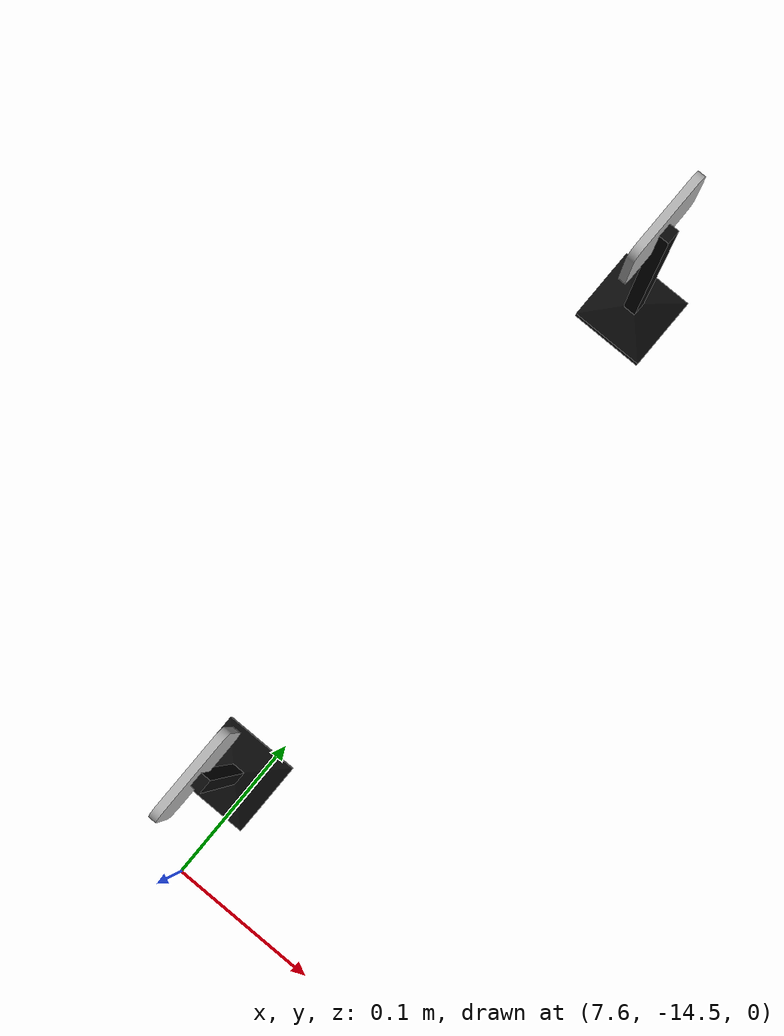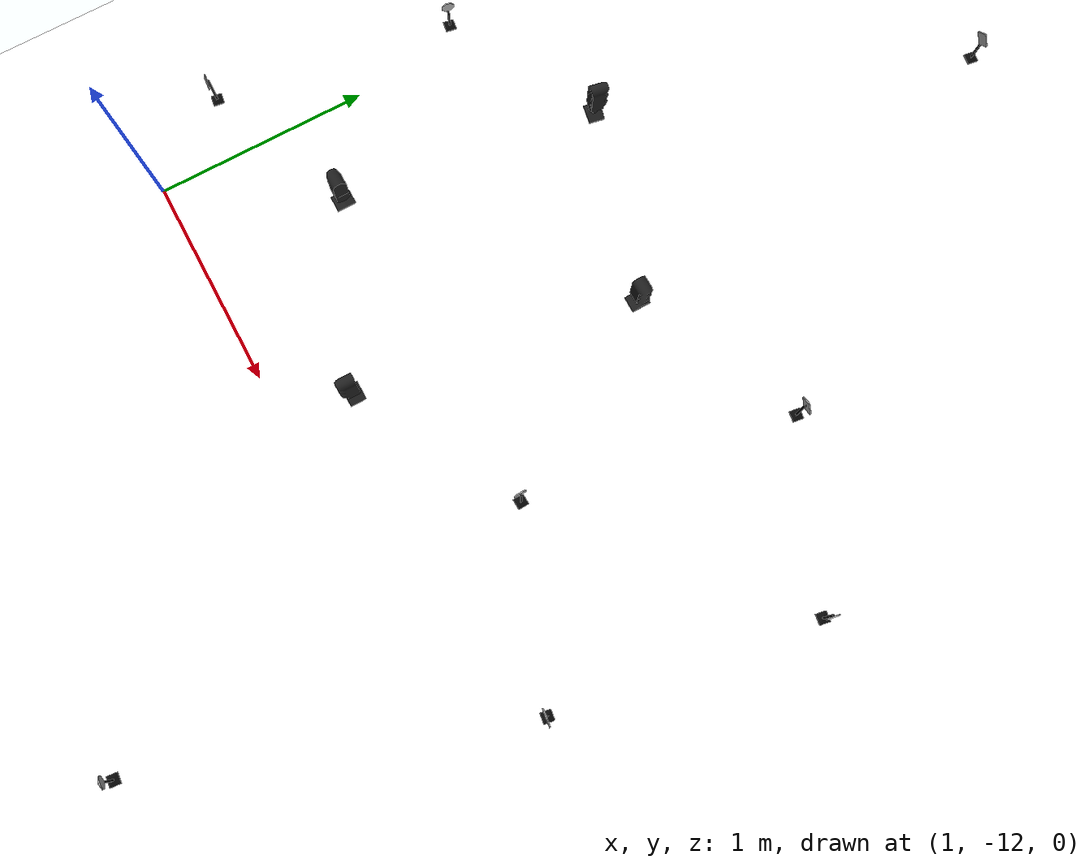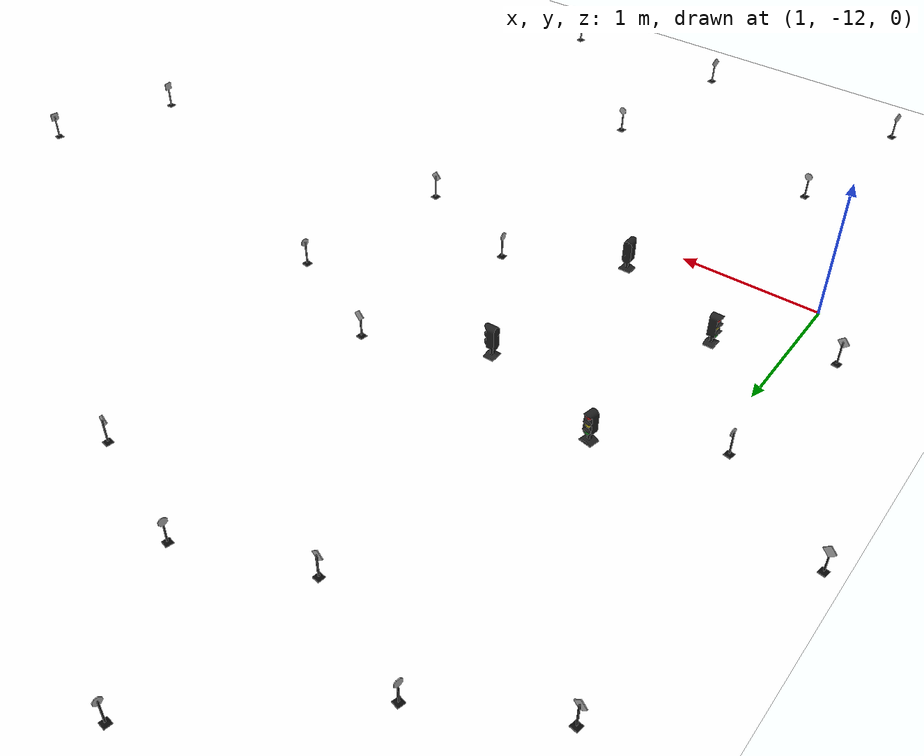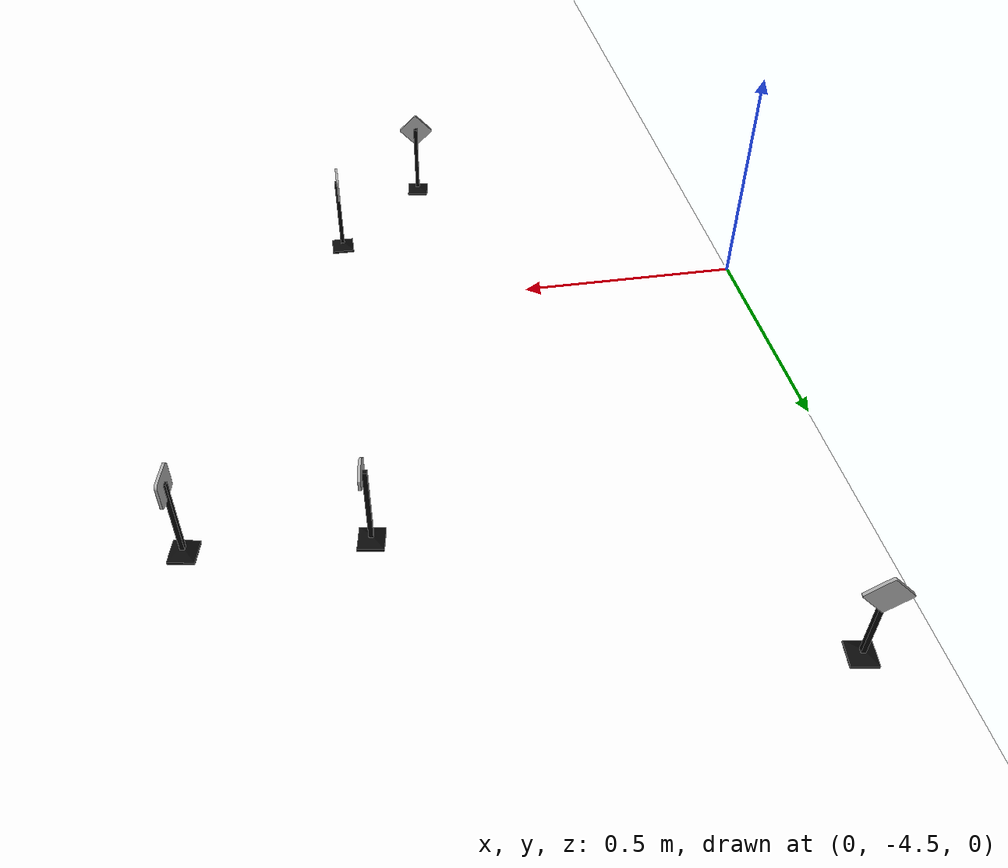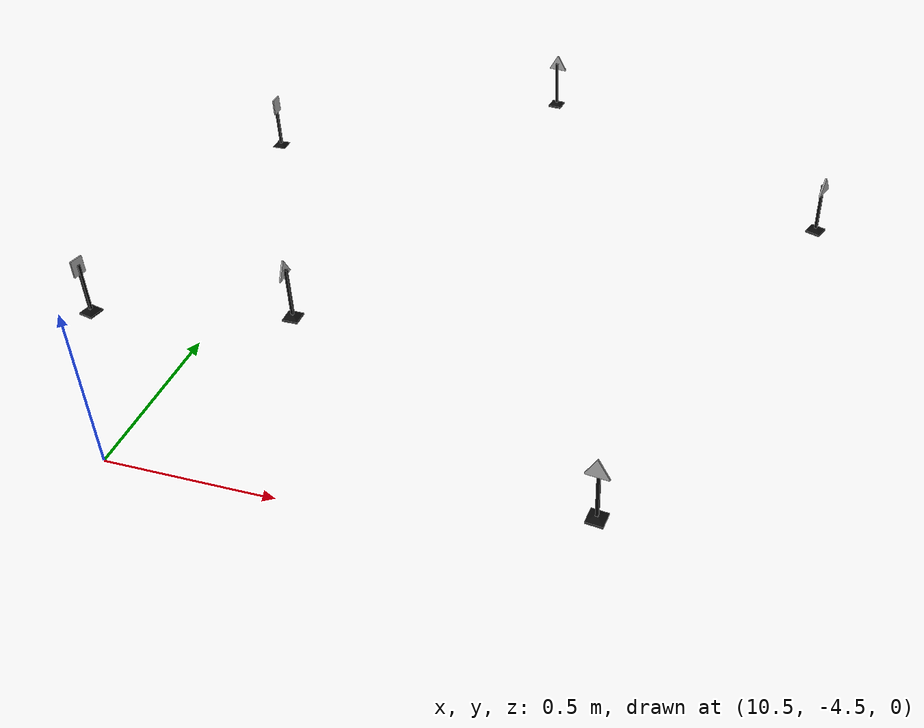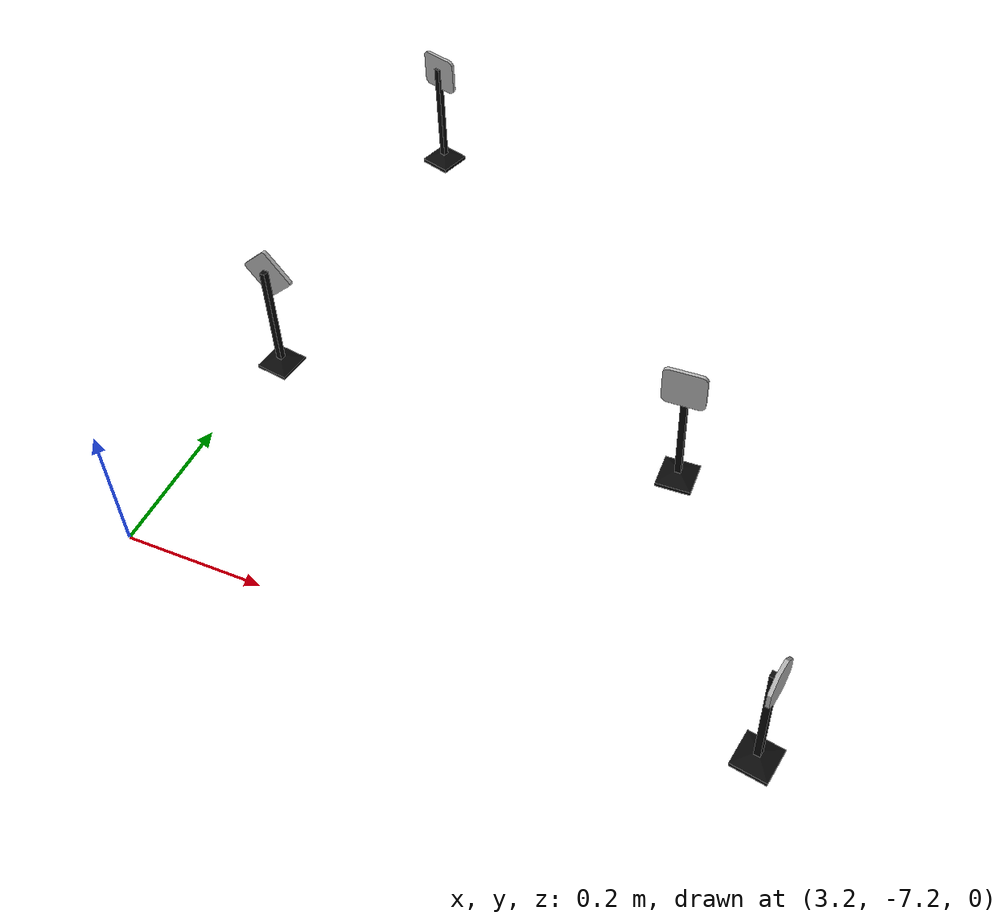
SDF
<sdf version="1.7">
 <world name="bfmc_official">
  <gravity>0 0 -9.8</gravity>
  <light name="c1" type="point">
   <pose>0 0 2 0 -0 0</pose>
   <diffuse>125 125 125 125</diffuse>
   <specular>50 50 50 50</specular>
   <attenuation><range>20</range><constant>0.3</constant><quadratic>0</quadratic><linear>0</linear></attenuation>
   <cast_shadows>0</cast_shadows>
   <direction>0 0 -1</direction>
   <spot><inner_angle>0</inner_angle><outer_angle>0</outer_angle><falloff>0</falloff></spot>
  </light>
  <light name="c2" type="point">
   <pose>15 0 2 0 -0 0</pose>
   <diffuse>125 125 125 125</diffuse>
   <specular>50 50 50 50</specular>
   <attenuation><range>20</range><constant>0.3</constant><quadratic>0</quadratic><linear>0</linear></attenuation>
   <cast_shadows>0</cast_shadows>
   <direction>0 0 -1</direction>
   <spot><inner_angle>0</inner_angle><outer_angle>0</outer_angle><falloff>0</falloff></spot>
  </light>
  <light name="c3" type="point">
   <pose>0 -15 2 0 -0 0</pose>
   <diffuse>125 125 125 125</diffuse>
   <specular>50 50 50 50</specular>
   <attenuation><range>20</range><constant>0.3</constant><quadratic>0</quadratic><linear>0</linear></attenuation>
   <cast_shadows>0</cast_shadows>
   <direction>0 0 -1</direction>
   <spot><inner_angle>0</inner_angle><outer_angle>0</outer_angle><falloff>0</falloff></spot>
  </light>
  <light name="c4" type="point">
   <pose>15 -15 2 0 -0 0</pose>
   <diffuse>125 125 125 125</diffuse>
   <specular>50 50 50 50</specular>
   <attenuation><range>50</range><constant>0.3</constant><quadratic>0</quadratic><linear>0</linear></attenuation>
   <cast_shadows>0</cast_shadows>
   <direction>0 0 -1</direction>
   <spot><inner_angle>0</inner_angle><outer_angle>0</outer_angle><falloff>0</falloff></spot>
  </light>
  <model name="track">
   <static>1</static>
   <link name="link">
    <collision name="collision">
     <geometry><plane><normal>0 0 1</normal><size>14.68 14.99</size></plane></geometry>
     <surface>
      <contact><collide_bitmask>65535</collide_bitmask></contact>
      <friction><ode><mu>1</mu><mu2>1</mu2></ode></friction>
     </surface>
    </collision>
    <visual name="visual">
     <geometry><plane><normal>0 0 1</normal><size>14.68 14.99</size></plane></geometry>
     <material>
      <ambient>1 1 1 1</ambient>
      <diffuse>1 1 1 1</diffuse>
      <specular>0 0 0 0</specular>
      <emissive>1 1 1 1</emissive>
      <script>
       <uri>model://track/materials/scripts</uri>
       <uri>model://track/materials/textures</uri>
       <name>BFMC_MATERIAL</name>
      </script>
     </material>
    </visual>
   </link>
   <pose>7.34 -7.495 0 0 -0 0</pose>
  </model>
  <magnetic_field>6e-06 2.3e-05 -4.2e-05</magnetic_field>
  <atmosphere type="adiabatic"/>
  <physics name="default_physics" default="0" type="ode">
   <max_step_size>0.001</max_step_size>
   <real_time_factor>1</real_time_factor>
   <real_time_update_rate>1000</real_time_update_rate>
  </physics>
  <scene><ambient>0.4 0.4 0.4 1</ambient><background>0.7 0.7 0.7 1</background><shadows>1</shadows></scene>
  <audio><device>default</device></audio>
  <spherical_coordinates>
   <surface_model>EARTH_WGS84</surface_model>
   <latitude_deg>0</latitude_deg>
   <longitude_deg>0</longitude_deg>
   <elevation>0</elevation>
   <heading_deg>0</heading_deg>
  </spherical_coordinates>
  <model name="slave">
   <link name="case">
    <inertial>
     <mass>0.5</mass>
     <inertia><ixx>0.166667</ixx><ixy>0</ixy><ixz>0</ixz><iyy>0</iyy><iyz>0</iyz><izz>0</izz></inertia>
    </inertial>
    <pose>-0.048681 0.002156 0 0 -0 0</pose>
    <visual name="visual">
     <geometry>
      <mesh><uri>model://traffic_light/meshes/traffic_light_case.dae</uri><scale>1 1 1</scale></mesh>
     </geometry>
     <material>
      <script><uri>file://media/materials/scripts/gazebo.material</uri><name>PR2/Black</name></script>
      <shader type="vertex"><normal_map>__default__</normal_map></shader>
      <ambient>0.2 0.2 0.2 1</ambient>
      <diffuse>0.2 0.2 0.2 1</diffuse>
      <specular>0.01 0.01 0.01 1</specular>
      <emissive>0 0 0 1</emissive>
     </material>
     <cast_shadows>0</cast_shadows>
    </visual>
    <collision name="collision">
     <geometry>
      <mesh><uri>model://traffic_light/meshes/traffic_light_case.dae</uri><scale>1 1 1</scale></mesh>
     </geometry>
     <surface>
      <friction>
       <ode><mu>1</mu><mu2>1</mu2><fdir1>0 0 0</fdir1><slip1>0</slip1><slip2>0</slip2></ode>
       <torsional>
        <coefficient>1</coefficient>
        <patch_radius>0</patch_radius>
        <surface_radius>0</surface_radius>
        <use_patch_radius>1</use_patch_radius>
        <ode><slip>0</slip></ode>
       </torsional>
      </friction>
      <bounce><restitution_coefficient>0</restitution_coefficient><threshold>1e+06</threshold></bounce>
      <contact>
       <collide_without_contact>0</collide_without_contact>
       <collide_without_contact_bitmask>1</collide_without_contact_bitmask>
       <collide_bitmask>1</collide_bitmask>
       <ode>
        <soft_cfm>0</soft_cfm>
        <soft_erp>0.2</soft_erp>
        <kp>1e+13</kp>
        <kd>1</kd>
        <max_vel>0.01</max_vel>
        <min_depth>0</min_depth>
       </ode>
       <bullet>
        <split_impulse>1</split_impulse>
        <split_impulse_penetration_threshold>-0.01</split_impulse_penetration_threshold>
        <soft_cfm>0</soft_cfm>
        <soft_erp>0.2</soft_erp>
        <kp>1e+13</kp>
        <kd>1</kd>
       </bullet>
      </contact>
     </surface>
    </collision>
   </link>
   <link name="green_lens">
    <light name="green_lens_light" type="spot">
     <pose relative_to="green_lens">4 0.001819 1 0 1.32589 0</pose>
     <diffuse>0 1 0 0</diffuse>
     <specular>0 1 0 0</specular>
     <attenuation><range>5</range><linear>0</linear><constant>0.08</constant><quadratic>0</quadratic></attenuation>
     <spot><inner_angle>0</inner_angle><outer_angle>0.01</outer_angle><falloff>1</falloff></spot>
     <cast_shadows>0</cast_shadows>
     <direction>0 0 -1</direction>
    </light>
    <inertial>
     <mass>1</mass>
     <inertia>
      <ixx>0.166667</ixx>
      <ixy>0</ixy>
      <ixz>0</ixz>
      <iyy>0.166667</iyy>
      <iyz>0</iyz>
      <izz>0.166667</izz>
     </inertia>
    </inertial>
    <pose>-0.018681 -0.000719 0.09102 0 -0 0</pose>
    <visual name="visual">
     <geometry>
      <mesh><uri>model://traffic_light/meshes/traffic_light_lens.dae</uri><scale>1 1 1</scale></mesh>
     </geometry>
     <material>
      <script>
       <uri>model://traffic_light/materials/scripts</uri>
       <uri>model://traffic_light/materials/textures</uri>
       <name>GREEN_LENS</name>
      </script>
      <emissive>0 0 0 1</emissive>
     </material>
     <cast_shadows>0</cast_shadows>
    </visual>
   </link>
   <link name="yellow_lens">
    <light name="yellow_lens_light" type="spot">
     <pose relative_to="yellow_lens">4 0.001819 1 0 1.32589 0</pose>
     <diffuse>1 1 0 0</diffuse>
     <specular>1 1 0 0</specular>
     <attenuation><range>5</range><linear>0</linear><constant>0.08</constant><quadratic>0</quadratic></attenuation>
     <spot><inner_angle>0</inner_angle><outer_angle>0.01</outer_angle><falloff>1</falloff></spot>
     <cast_shadows>0</cast_shadows>
     <direction>0 0 -1</direction>
    </light>
    <inertial>
     <mass>1</mass>
     <inertia>
      <ixx>0.166667</ixx>
      <ixy>0</ixy>
      <ixz>0</ixz>
      <iyy>0.166667</iyy>
      <iyz>0</iyz>
      <izz>0.166667</izz>
     </inertia>
    </inertial>
    <pose>-0.018681 -0.000719 0.15 0 -0 0</pose>
    <visual name="visual">
     <geometry>
      <mesh><uri>model://traffic_light/meshes/traffic_light_lens.dae</uri><scale>1 1 1</scale></mesh>
     </geometry>
     <material>
      <script>
       <uri>model://traffic_light/materials/scripts</uri>
       <uri>model://traffic_light/materials/textures</uri>
       <name>YELLOW_LENS</name>
      </script>
      <emissive>0 0 0 1</emissive>
     </material>
     <cast_shadows>0</cast_shadows>
    </visual>
   </link>
   <link name="red_lens">
    <light name="red_lens_light" type="spot">
     <pose relative_to="red_lens">4 0.001819 1 0 1.32589 0</pose>
     <diffuse>1 0 0 0</diffuse>
     <specular>1 0 0 0</specular>
     <attenuation><range>5</range><linear>0</linear><constant>0.08</constant><quadratic>0</quadratic></attenuation>
     <spot><inner_angle>0</inner_angle><outer_angle>0.01</outer_angle><falloff>1</falloff></spot>
     <cast_shadows>0</cast_shadows>
     <direction>0 0 -1</direction>
    </light>
    <inertial>
     <mass>1</mass>
     <inertia>
      <ixx>0.166667</ixx>
      <ixy>0</ixy>
      <ixz>0</ixz>
      <iyy>0.166667</iyy>
      <iyz>0</iyz>
      <izz>0.166667</izz>
     </inertia>
    </inertial>
    <pose>-0.018681 -0.000719 0.21022 0 -0 0</pose>
    <visual name="visual">
     <geometry>
      <mesh><uri>model://traffic_light/meshes/traffic_light_lens.dae</uri><scale>1 1 1</scale></mesh>
     </geometry>
     <material>
      <script>
       <uri>model://traffic_light/materials/scripts</uri>
       <uri>model://traffic_light/materials/textures</uri>
       <name>RED_LENS</name>
      </script>
      <emissive>0 0 0 1</emissive>
     </material>
     <cast_shadows>0</cast_shadows>
    </visual>
   </link>
   <joint name="link_1_JOINT_0" type="fixed">
    <parent>case</parent>
    <child>red_lens</child>
    <physics>
     <ode><limit><cfm>0</cfm><erp>0.2</erp></limit><suspension><cfm>0</cfm><erp>0.2</erp></suspension></ode>
    </physics>
   </joint>
   <joint name="link_1_JOINT_1" type="fixed">
    <parent>case</parent>
    <child>yellow_lens</child>
    <physics>
     <ode><limit><cfm>0</cfm><erp>0.2</erp></limit><suspension><cfm>0</cfm><erp>0.2</erp></suspension></ode>
    </physics>
   </joint>
   <joint name="link_1_JOINT_2" type="fixed">
    <parent>case</parent>
    <child>green_lens</child>
    <physics>
     <ode><limit><cfm>0</cfm><erp>0.2</erp></limit><suspension><cfm>0</cfm><erp>0.2</erp></suspension></ode>
    </physics>
   </joint>
   <static>1</static>
   <plugin name="traffic_light_plugin" filename="libtraffic_light_plugin.so">
    <ros><namespace>$(arg robot_namespace)</namespace></ros>
   </plugin>
   <pose>2.53546 -10.3692 0 0 -0 0</pose>
  </model>
  <model name="start">
   <link name="case">
    <inertial>
     <mass>0.5</mass>
     <inertia><ixx>0.166667</ixx><ixy>0</ixy><ixz>0</ixz><iyy>0</iyy><iyz>0</iyz><izz>0</izz></inertia>
    </inertial>
    <pose>-0.048681 0.002156 0 0 -0 0</pose>
    <visual name="visual">
     <geometry>
      <mesh><uri>model://traffic_light/meshes/traffic_light_case.dae</uri><scale>1 1 1</scale></mesh>
     </geometry>
     <material>
      <script><uri>file://media/materials/scripts/gazebo.material</uri><name>PR2/Black</name></script>
      <shader type="vertex"><normal_map>__default__</normal_map></shader>
      <ambient>0.2 0.2 0.2 1</ambient>
      <diffuse>0.2 0.2 0.2 1</diffuse>
      <specular>0.01 0.01 0.01 1</specular>
      <emissive>0 0 0 1</emissive>
     </material>
     <cast_shadows>0</cast_shadows>
    </visual>
    <collision name="collision">
     <geometry>
      <mesh><uri>model://traffic_light/meshes/traffic_light_case.dae</uri><scale>1 1 1</scale></mesh>
     </geometry>
     <surface>
      <friction>
       <ode><mu>1</mu><mu2>1</mu2><fdir1>0 0 0</fdir1><slip1>0</slip1><slip2>0</slip2></ode>
       <torsional>
        <coefficient>1</coefficient>
        <patch_radius>0</patch_radius>
        <surface_radius>0</surface_radius>
        <use_patch_radius>1</use_patch_radius>
        <ode><slip>0</slip></ode>
       </torsional>
      </friction>
      <bounce><restitution_coefficient>0</restitution_coefficient><threshold>1e+06</threshold></bounce>
      <contact>
       <collide_without_contact>0</collide_without_contact>
       <collide_without_contact_bitmask>1</collide_without_contact_bitmask>
       <collide_bitmask>1</collide_bitmask>
       <ode>
        <soft_cfm>0</soft_cfm>
        <soft_erp>0.2</soft_erp>
        <kp>1e+13</kp>
        <kd>1</kd>
        <max_vel>0.01</max_vel>
        <min_depth>0</min_depth>
       </ode>
       <bullet>
        <split_impulse>1</split_impulse>
        <split_impulse_penetration_threshold>-0.01</split_impulse_penetration_threshold>
        <soft_cfm>0</soft_cfm>
        <soft_erp>0.2</soft_erp>
        <kp>1e+13</kp>
        <kd>1</kd>
       </bullet>
      </contact>
     </surface>
    </collision>
   </link>
   <link name="green_lens">
    <light name="green_lens_light" type="spot">
     <pose relative_to="green_lens">4 0.001819 1 0 1.32589 0</pose>
     <diffuse>0 1 0 0</diffuse>
     <specular>0 1 0 0</specular>
     <attenuation><range>5</range><linear>0</linear><constant>0.08</constant><quadratic>0</quadratic></attenuation>
     <spot><inner_angle>0</inner_angle><outer_angle>0.01</outer_angle><falloff>1</falloff></spot>
     <cast_shadows>0</cast_shadows>
     <direction>0 0 -1</direction>
    </light>
    <inertial>
     <mass>1</mass>
     <inertia>
      <ixx>0.166667</ixx>
      <ixy>0</ixy>
      <ixz>0</ixz>
      <iyy>0.166667</iyy>
      <iyz>0</iyz>
      <izz>0.166667</izz>
     </inertia>
    </inertial>
    <pose>-0.018681 -0.000719 0.09102 0 -0 0</pose>
    <visual name="visual">
     <geometry>
      <mesh><uri>model://traffic_light/meshes/traffic_light_lens.dae</uri><scale>1 1 1</scale></mesh>
     </geometry>
     <material>
      <script>
       <uri>model://traffic_light/materials/scripts</uri>
       <uri>model://traffic_light/materials/textures</uri>
       <name>GREEN_LENS</name>
      </script>
      <emissive>0 0 0 1</emissive>
     </material>
     <cast_shadows>0</cast_shadows>
    </visual>
   </link>
   <link name="yellow_lens">
    <light name="yellow_lens_light" type="spot">
     <pose relative_to="yellow_lens">4 0.001819 1 0 1.32589 0</pose>
     <diffuse>1 1 0 0</diffuse>
     <specular>1 1 0 0</specular>
     <attenuation><range>5</range><linear>0</linear><constant>0.08</constant><quadratic>0</quadratic></attenuation>
     <spot><inner_angle>0</inner_angle><outer_angle>0.01</outer_angle><falloff>1</falloff></spot>
     <cast_shadows>0</cast_shadows>
     <direction>0 0 -1</direction>
    </light>
    <inertial>
     <mass>1</mass>
     <inertia>
      <ixx>0.166667</ixx>
      <ixy>0</ixy>
      <ixz>0</ixz>
      <iyy>0.166667</iyy>
      <iyz>0</iyz>
      <izz>0.166667</izz>
     </inertia>
    </inertial>
    <pose>-0.018681 -0.000719 0.15 0 -0 0</pose>
    <visual name="visual">
     <geometry>
      <mesh><uri>model://traffic_light/meshes/traffic_light_lens.dae</uri><scale>1 1 1</scale></mesh>
     </geometry>
     <material>
      <script>
       <uri>model://traffic_light/materials/scripts</uri>
       <uri>model://traffic_light/materials/textures</uri>
       <name>YELLOW_LENS</name>
      </script>
      <emissive>0 0 0 1</emissive>
     </material>
     <cast_shadows>0</cast_shadows>
    </visual>
   </link>
   <link name="red_lens">
    <light name="red_lens_light" type="spot">
     <pose relative_to="red_lens">4 0.001819 1 0 1.32589 0</pose>
     <diffuse>1 0 0 0</diffuse>
     <specular>1 0 0 0</specular>
     <attenuation><range>5</range><linear>0</linear><constant>0.08</constant><quadratic>0</quadratic></attenuation>
     <spot><inner_angle>0</inner_angle><outer_angle>0.01</outer_angle><falloff>1</falloff></spot>
     <cast_shadows>0</cast_shadows>
     <direction>0 0 -1</direction>
    </light>
    <inertial>
     <mass>1</mass>
     <inertia>
      <ixx>0.166667</ixx>
      <ixy>0</ixy>
      <ixz>0</ixz>
      <iyy>0.166667</iyy>
      <iyz>0</iyz>
      <izz>0.166667</izz>
     </inertia>
    </inertial>
    <pose>-0.018681 -0.000719 0.21022 0 -0 0</pose>
    <visual name="visual">
     <geometry>
      <mesh><uri>model://traffic_light/meshes/traffic_light_lens.dae</uri><scale>1 1 1</scale></mesh>
     </geometry>
     <material>
      <script>
       <uri>model://traffic_light/materials/scripts</uri>
       <uri>model://traffic_light/materials/textures</uri>
       <name>RED_LENS</name>
      </script>
      <emissive>0 0 0 1</emissive>
     </material>
     <cast_shadows>0</cast_shadows>
    </visual>
   </link>
   <joint name="link_1_JOINT_0" type="fixed">
    <parent>case</parent>
    <child>red_lens</child>
    <physics>
     <ode><limit><cfm>0</cfm><erp>0.2</erp></limit><suspension><cfm>0</cfm><erp>0.2</erp></suspension></ode>
    </physics>
   </joint>
   <joint name="link_1_JOINT_1" type="fixed">
    <parent>case</parent>
    <child>yellow_lens</child>
    <physics>
     <ode><limit><cfm>0</cfm><erp>0.2</erp></limit><suspension><cfm>0</cfm><erp>0.2</erp></suspension></ode>
    </physics>
   </joint>
   <joint name="link_1_JOINT_2" type="fixed">
    <parent>case</parent>
    <child>green_lens</child>
    <physics>
     <ode><limit><cfm>0</cfm><erp>0.2</erp></limit><suspension><cfm>0</cfm><erp>0.2</erp></suspension></ode>
    </physics>
   </joint>
   <static>1</static>
   <plugin name="traffic_light_plugin" filename="libtraffic_light_plugin.so">
    <ros><namespace>$(arg robot_namespace)</namespace></ros>
   </plugin>
   <pose>2.26091 -11.7168 0 0 0 -1.5708</pose>
  </model>
  <model name="master">
   <link name="case">
    <inertial>
     <mass>0.5</mass>
     <inertia><ixx>0.166667</ixx><ixy>0</ixy><ixz>0</ixz><iyy>0</iyy><iyz>0</iyz><izz>0</izz></inertia>
    </inertial>
    <pose>-0.048681 0.002156 0 0 -0 0</pose>
    <visual name="visual">
     <geometry>
      <mesh><uri>model://traffic_light/meshes/traffic_light_case.dae</uri><scale>1 1 1</scale></mesh>
     </geometry>
     <material>
      <script><uri>file://media/materials/scripts/gazebo.material</uri><name>PR2/Black</name></script>
      <shader type="vertex"><normal_map>__default__</normal_map></shader>
      <ambient>0.2 0.2 0.2 1</ambient>
      <diffuse>0.2 0.2 0.2 1</diffuse>
      <specular>0.01 0.01 0.01 1</specular>
      <emissive>0 0 0 1</emissive>
     </material>
     <cast_shadows>0</cast_shadows>
    </visual>
    <collision name="collision">
     <geometry>
      <mesh><uri>model://traffic_light/meshes/traffic_light_case.dae</uri><scale>1 1 1</scale></mesh>
     </geometry>
     <surface>
      <friction>
       <ode><mu>1</mu><mu2>1</mu2><fdir1>0 0 0</fdir1><slip1>0</slip1><slip2>0</slip2></ode>
       <torsional>
        <coefficient>1</coefficient>
        <patch_radius>0</patch_radius>
        <surface_radius>0</surface_radius>
        <use_patch_radius>1</use_patch_radius>
        <ode><slip>0</slip></ode>
       </torsional>
      </friction>
      <bounce><restitution_coefficient>0</restitution_coefficient><threshold>1e+06</threshold></bounce>
      <contact>
       <collide_without_contact>0</collide_without_contact>
       <collide_without_contact_bitmask>1</collide_without_contact_bitmask>
       <collide_bitmask>1</collide_bitmask>
       <ode>
        <soft_cfm>0</soft_cfm>
        <soft_erp>0.2</soft_erp>
        <kp>1e+13</kp>
        <kd>1</kd>
        <max_vel>0.01</max_vel>
        <min_depth>0</min_depth>
       </ode>
       <bullet>
        <split_impulse>1</split_impulse>
        <split_impulse_penetration_threshold>-0.01</split_impulse_penetration_threshold>
        <soft_cfm>0</soft_cfm>
        <soft_erp>0.2</soft_erp>
        <kp>1e+13</kp>
        <kd>1</kd>
       </bullet>
      </contact>
     </surface>
    </collision>
   </link>
   <link name="green_lens">
    <light name="green_lens_light" type="spot">
     <pose relative_to="green_lens">4 0.001819 1 0 1.32589 0</pose>
     <diffuse>0 1 0 0</diffuse>
     <specular>0 1 0 0</specular>
     <attenuation><range>5</range><linear>0</linear><constant>0.08</constant><quadratic>0</quadratic></attenuation>
     <spot><inner_angle>0</inner_angle><outer_angle>0.01</outer_angle><falloff>1</falloff></spot>
     <cast_shadows>0</cast_shadows>
     <direction>0 0 -1</direction>
    </light>
    <inertial>
     <mass>1</mass>
     <inertia>
      <ixx>0.166667</ixx>
      <ixy>0</ixy>
      <ixz>0</ixz>
      <iyy>0.166667</iyy>
      <iyz>0</iyz>
      <izz>0.166667</izz>
     </inertia>
    </inertial>
    <pose>-0.018681 -0.000719 0.09102 0 -0 0</pose>
    <visual name="visual">
     <geometry>
      <mesh><uri>model://traffic_light/meshes/traffic_light_lens.dae</uri><scale>1 1 1</scale></mesh>
     </geometry>
     <material>
      <script>
       <uri>model://traffic_light/materials/scripts</uri>
       <uri>model://traffic_light/materials/textures</uri>
       <name>GREEN_LENS</name>
      </script>
      <emissive>0 0 0 1</emissive>
     </material>
     <cast_shadows>0</cast_shadows>
    </visual>
   </link>
   <link name="yellow_lens">
    <light name="yellow_lens_light" type="spot">
     <pose relative_to="yellow_lens">4 0.001819 1 0 1.32589 0</pose>
     <diffuse>1 1 0 0</diffuse>
     <specular>1 1 0 0</specular>
     <attenuation><range>5</range><linear>0</linear><constant>0.08</constant><quadratic>0</quadratic></attenuation>
     <spot><inner_angle>0</inner_angle><outer_angle>0.01</outer_angle><falloff>1</falloff></spot>
     <cast_shadows>0</cast_shadows>
     <direction>0 0 -1</direction>
    </light>
    <inertial>
     <mass>1</mass>
     <inertia>
      <ixx>0.166667</ixx>
      <ixy>0</ixy>
      <ixz>0</ixz>
      <iyy>0.166667</iyy>
      <iyz>0</iyz>
      <izz>0.166667</izz>
     </inertia>
    </inertial>
    <pose>-0.018681 -0.000719 0.15 0 -0 0</pose>
    <visual name="visual">
     <geometry>
      <mesh><uri>model://traffic_light/meshes/traffic_light_lens.dae</uri><scale>1 1 1</scale></mesh>
     </geometry>
     <material>
      <script>
       <uri>model://traffic_light/materials/scripts</uri>
       <uri>model://traffic_light/materials/textures</uri>
       <name>YELLOW_LENS</name>
      </script>
      <emissive>0 0 0 1</emissive>
     </material>
     <cast_shadows>0</cast_shadows>
    </visual>
   </link>
   <link name="red_lens">
    <light name="red_lens_light" type="spot">
     <pose relative_to="red_lens">4 0.001819 1 0 1.32589 0</pose>
     <diffuse>1 0 0 0</diffuse>
     <specular>1 0 0 0</specular>
     <attenuation><range>5</range><linear>0</linear><constant>0.08</constant><quadratic>0</quadratic></attenuation>
     <spot><inner_angle>0</inner_angle><outer_angle>0.01</outer_angle><falloff>1</falloff></spot>
     <cast_shadows>0</cast_shadows>
     <direction>0 0 -1</direction>
    </light>
    <inertial>
     <mass>1</mass>
     <inertia>
      <ixx>0.166667</ixx>
      <ixy>0</ixy>
      <ixz>0</ixz>
      <iyy>0.166667</iyy>
      <iyz>0</iyz>
      <izz>0.166667</izz>
     </inertia>
    </inertial>
    <pose>-0.018681 -0.000719 0.21022 0 -0 0</pose>
    <visual name="visual">
     <geometry>
      <mesh><uri>model://traffic_light/meshes/traffic_light_lens.dae</uri><scale>1 1 1</scale></mesh>
     </geometry>
     <material>
      <script>
       <uri>model://traffic_light/materials/scripts</uri>
       <uri>model://traffic_light/materials/textures</uri>
       <name>RED_LENS</name>
      </script>
      <emissive>0 0 0 1</emissive>
     </material>
     <cast_shadows>0</cast_shadows>
    </visual>
   </link>
   <joint name="link_1_JOINT_0" type="fixed">
    <parent>case</parent>
    <child>red_lens</child>
    <physics>
     <ode><limit><cfm>0</cfm><erp>0.2</erp></limit><suspension><cfm>0</cfm><erp>0.2</erp></suspension></ode>
    </physics>
   </joint>
   <joint name="link_1_JOINT_1" type="fixed">
    <parent>case</parent>
    <child>yellow_lens</child>
    <physics>
     <ode><limit><cfm>0</cfm><erp>0.2</erp></limit><suspension><cfm>0</cfm><erp>0.2</erp></suspension></ode>
    </physics>
   </joint>
   <joint name="link_1_JOINT_2" type="fixed">
    <parent>case</parent>
    <child>green_lens</child>
    <physics>
     <ode><limit><cfm>0</cfm><erp>0.2</erp></limit><suspension><cfm>0</cfm><erp>0.2</erp></suspension></ode>
    </physics>
   </joint>
   <static>1</static>
   <plugin name="traffic_light_plugin" filename="libtraffic_light_plugin.so">
    <ros><namespace>$(arg robot_namespace)</namespace></ros>
   </plugin>
   <pose>1.38342 -11.2988 0 0 -0 3.14159</pose>
  </model>
  <model name="antimaster">
   <link name="case">
    <inertial>
     <mass>0.5</mass>
     <inertia><ixx>0.166667</ixx><ixy>0</ixy><ixz>0</ixz><iyy>0</iyy><iyz>0</iyz><izz>0</izz></inertia>
    </inertial>
    <pose>-0.048681 0.002156 0 0 -0 0</pose>
    <visual name="visual">
     <geometry>
      <mesh><uri>model://traffic_light/meshes/traffic_light_case.dae</uri><scale>1 1 1</scale></mesh>
     </geometry>
     <material>
      <script><uri>file://media/materials/scripts/gazebo.material</uri><name>PR2/Black</name></script>
      <shader type="vertex"><normal_map>__default__</normal_map></shader>
      <ambient>0.2 0.2 0.2 1</ambient>
      <diffuse>0.2 0.2 0.2 1</diffuse>
      <specular>0.01 0.01 0.01 1</specular>
      <emissive>0 0 0 1</emissive>
     </material>
     <cast_shadows>0</cast_shadows>
    </visual>
    <collision name="collision">
     <geometry>
      <mesh><uri>model://traffic_light/meshes/traffic_light_case.dae</uri><scale>1 1 1</scale></mesh>
     </geometry>
     <surface>
      <friction>
       <ode><mu>1</mu><mu2>1</mu2><fdir1>0 0 0</fdir1><slip1>0</slip1><slip2>0</slip2></ode>
       <torsional>
        <coefficient>1</coefficient>
        <patch_radius>0</patch_radius>
        <surface_radius>0</surface_radius>
        <use_patch_radius>1</use_patch_radius>
        <ode><slip>0</slip></ode>
       </torsional>
      </friction>
      <bounce><restitution_coefficient>0</restitution_coefficient><threshold>1e+06</threshold></bounce>
      <contact>
       <collide_without_contact>0</collide_without_contact>
       <collide_without_contact_bitmask>1</collide_without_contact_bitmask>
       <collide_bitmask>1</collide_bitmask>
       <ode>
        <soft_cfm>0</soft_cfm>
        <soft_erp>0.2</soft_erp>
        <kp>1e+13</kp>
        <kd>1</kd>
        <max_vel>0.01</max_vel>
        <min_depth>0</min_depth>
       </ode>
       <bullet>
        <split_impulse>1</split_impulse>
        <split_impulse_penetration_threshold>-0.01</split_impulse_penetration_threshold>
        <soft_cfm>0</soft_cfm>
        <soft_erp>0.2</soft_erp>
        <kp>1e+13</kp>
        <kd>1</kd>
       </bullet>
      </contact>
     </surface>
    </collision>
   </link>
   <link name="green_lens">
    <light name="green_lens_light" type="spot">
     <pose relative_to="green_lens">4 0.001819 1 0 1.32589 0</pose>
     <diffuse>0 1 0 0</diffuse>
     <specular>0 1 0 0</specular>
     <attenuation><range>5</range><linear>0</linear><constant>0.08</constant><quadratic>0</quadratic></attenuation>
     <spot><inner_angle>0</inner_angle><outer_angle>0.01</outer_angle><falloff>1</falloff></spot>
     <cast_shadows>0</cast_shadows>
     <direction>0 0 -1</direction>
    </light>
    <inertial>
     <mass>1</mass>
     <inertia>
      <ixx>0.166667</ixx>
      <ixy>0</ixy>
      <ixz>0</ixz>
      <iyy>0.166667</iyy>
      <iyz>0</iyz>
      <izz>0.166667</izz>
     </inertia>
    </inertial>
    <pose>-0.018681 -0.000719 0.09102 0 -0 0</pose>
    <visual name="visual">
     <geometry>
      <mesh><uri>model://traffic_light/meshes/traffic_light_lens.dae</uri><scale>1 1 1</scale></mesh>
     </geometry>
     <material>
      <script>
       <uri>model://traffic_light/materials/scripts</uri>
       <uri>model://traffic_light/materials/textures</uri>
       <name>GREEN_LENS</name>
      </script>
      <emissive>0 0 0 1</emissive>
     </material>
     <cast_shadows>0</cast_shadows>
    </visual>
   </link>
   <link name="yellow_lens">
    <light name="yellow_lens_light" type="spot">
     <pose relative_to="yellow_lens">4 0.001819 1 0 1.32589 0</pose>
     <diffuse>1 1 0 0</diffuse>
     <specular>1 1 0 0</specular>
     <attenuation><range>5</range><linear>0</linear><constant>0.08</constant><quadratic>0</quadratic></attenuation>
     <spot><inner_angle>0</inner_angle><outer_angle>0.01</outer_angle><falloff>1</falloff></spot>
     <cast_shadows>0</cast_shadows>
     <direction>0 0 -1</direction>
    </light>
    <inertial>
     <mass>1</mass>
     <inertia>
      <ixx>0.166667</ixx>
      <ixy>0</ixy>
      <ixz>0</ixz>
      <iyy>0.166667</iyy>
      <iyz>0</iyz>
      <izz>0.166667</izz>
     </inertia>
    </inertial>
    <pose>-0.018681 -0.000719 0.15 0 -0 0</pose>
    <visual name="visual">
     <geometry>
      <mesh><uri>model://traffic_light/meshes/traffic_light_lens.dae</uri><scale>1 1 1</scale></mesh>
     </geometry>
     <material>
      <script>
       <uri>model://traffic_light/materials/scripts</uri>
       <uri>model://traffic_light/materials/textures</uri>
       <name>YELLOW_LENS</name>
      </script>
      <emissive>0 0 0 1</emissive>
     </material>
     <cast_shadows>0</cast_shadows>
    </visual>
   </link>
   <link name="red_lens">
    <light name="red_lens_light" type="spot">
     <pose relative_to="red_lens">4 0.001819 1 0 1.32589 0</pose>
     <diffuse>1 0 0 0</diffuse>
     <specular>1 0 0 0</specular>
     <attenuation><range>5</range><linear>0</linear><constant>0.08</constant><quadratic>0</quadratic></attenuation>
     <spot><inner_angle>0</inner_angle><outer_angle>0.01</outer_angle><falloff>1</falloff></spot>
     <cast_shadows>0</cast_shadows>
     <direction>0 0 -1</direction>
    </light>
    <inertial>
     <mass>1</mass>
     <inertia>
      <ixx>0.166667</ixx>
      <ixy>0</ixy>
      <ixz>0</ixz>
      <iyy>0.166667</iyy>
      <iyz>0</iyz>
      <izz>0.166667</izz>
     </inertia>
    </inertial>
    <pose>-0.018681 -0.000719 0.21022 0 -0 0</pose>
    <visual name="visual">
     <geometry>
      <mesh><uri>model://traffic_light/meshes/traffic_light_lens.dae</uri><scale>1 1 1</scale></mesh>
     </geometry>
     <material>
      <script>
       <uri>model://traffic_light/materials/scripts</uri>
       <uri>model://traffic_light/materials/textures</uri>
       <name>RED_LENS</name>
      </script>
      <emissive>0 0 0 1</emissive>
     </material>
     <cast_shadows>0</cast_shadows>
    </visual>
   </link>
   <joint name="link_1_JOINT_0" type="fixed">
    <parent>case</parent>
    <child>red_lens</child>
    <physics>
     <ode><limit><cfm>0</cfm><erp>0.2</erp></limit><suspension><cfm>0</cfm><erp>0.2</erp></suspension></ode>
    </physics>
   </joint>
   <joint name="link_1_JOINT_1" type="fixed">
    <parent>case</parent>
    <child>yellow_lens</child>
    <physics>
     <ode><limit><cfm>0</cfm><erp>0.2</erp></limit><suspension><cfm>0</cfm><erp>0.2</erp></suspension></ode>
    </physics>
   </joint>
   <joint name="link_1_JOINT_2" type="fixed">
    <parent>case</parent>
    <child>green_lens</child>
    <physics>
     <ode><limit><cfm>0</cfm><erp>0.2</erp></limit><suspension><cfm>0</cfm><erp>0.2</erp></suspension></ode>
    </physics>
   </joint>
   <static>1</static>
   <plugin name="traffic_light_plugin" filename="libtraffic_light_plugin.so">
    <ros><namespace>$(arg robot_namespace)</namespace></ros>
   </plugin>
   <pose>1.61253 -10.0417 0 0 -0 1.38009</pose>
  </model>
  <model name="priority_sign">
   <static>1</static>
   <link name="sign_leg">
    <inertial>
     <mass>0.5</mass>
     <inertia>
      <ixx>0.166667</ixx>
      <ixy>0</ixy>
      <ixz>0</ixz>
      <iyy>0.166667</iyy>
      <iyz>0</iyz>
      <izz>0.166667</izz>
     </inertia>
     <pose>0 0 -0.078998 0 -0 0</pose>
    </inertial>
    <pose>0.002193 -0.000682 -0.07606 0 -0 0</pose>
    <self_collide>1</self_collide>
    <enable_wind>1</enable_wind>
    <visual name="visual">
     <geometry><mesh><uri>model://subassembly/meshes/sign_leg.dae</uri><scale>1 1 1</scale></mesh></geometry>
    </visual>
    <collision name="collision">
     <geometry><mesh><uri>model://subassembly/meshes/sign_leg.dae</uri><scale>1 1 1</scale></mesh></geometry>
     <surface>
      <friction>
       <ode><mu>0.46</mu><mu2>1</mu2><fdir1>0 0 0</fdir1><slip1>0</slip1><slip2>0</slip2></ode>
       <torsional>
        <coefficient>1</coefficient>
        <patch_radius>0</patch_radius>
        <surface_radius>0</surface_radius>
        <use_patch_radius>1</use_patch_radius>
        <ode><slip>0</slip></ode>
       </torsional>
      </friction>
      <bounce><restitution_coefficient>0</restitution_coefficient><threshold>1e+06</threshold></bounce>
      <contact>
       <collide_without_contact>0</collide_without_contact>
       <collide_without_contact_bitmask>1</collide_without_contact_bitmask>
       <collide_bitmask>1</collide_bitmask>
       <ode>
        <soft_cfm>0</soft_cfm>
        <soft_erp>0.2</soft_erp>
        <kp>1e+13</kp>
        <kd>1</kd>
        <max_vel>0.01</max_vel>
        <min_depth>0</min_depth>
       </ode>
       <bullet>
        <split_impulse>1</split_impulse>
        <split_impulse_penetration_threshold>-0.01</split_impulse_penetration_threshold>
        <soft_cfm>0</soft_cfm>
        <soft_erp>0.2</soft_erp>
        <kp>1e+13</kp>
        <kd>1</kd>
       </bullet>
      </contact>
     </surface>
    </collision>
   </link>
   <link name="caro_support">
    <inertial>
     <mass>0.022</mass>
     <inertia>
      <ixx>0.166667</ixx>
      <ixy>0</ixy>
      <ixz>0</ixz>
      <iyy>0.166667</iyy>
      <iyz>0</iyz>
      <izz>0.166667</izz>
     </inertia>
    </inertial>
    <pose>-0.002193 0.000682 0.09894 0 -0 3.14159</pose>
    <self_collide>1</self_collide>
    <enable_wind>1</enable_wind>
    <visual name="visual">
     <geometry>
      <mesh><uri>model://priority_sign/meshes/priority_sign.dae</uri><scale>1 1 1</scale></mesh>
     </geometry>
     <material>
      <lighting>1</lighting>
      <script>
       <uri>model://priority_sign/materials/scripts</uri>
       <uri>model://priority_sign/materials/textures</uri>
       <name>PRIORITY_SIGN</name>
      </script>
      <shader type="vertex"><normal_map>__default__</normal_map></shader>
      <ambient>0.3 0.3 0.3 1</ambient>
      <diffuse>0.7 0.7 0.7 1</diffuse>
      <specular>0.01 0.01 0.01 1</specular>
      <emissive>0 0 0 1</emissive>
     </material>
    </visual>
    <collision name="collision">
     <geometry>
      <mesh><uri>model://priority_sign/meshes/priority_sign.dae</uri><scale>1 1 1</scale></mesh>
     </geometry>
     <surface>
      <friction>
       <ode><mu>0.46</mu><mu2>1</mu2><fdir1>0 0 0</fdir1><slip1>0</slip1><slip2>0</slip2></ode>
       <torsional>
        <coefficient>1</coefficient>
        <patch_radius>0</patch_radius>
        <surface_radius>0</surface_radius>
        <use_patch_radius>1</use_patch_radius>
        <ode><slip>0</slip></ode>
       </torsional>
      </friction>
      <bounce><restitution_coefficient>0</restitution_coefficient><threshold>1e+06</threshold></bounce>
      <contact>
       <collide_without_contact>0</collide_without_contact>
       <collide_without_contact_bitmask>1</collide_without_contact_bitmask>
       <collide_bitmask>1</collide_bitmask>
       <ode>
        <soft_cfm>0</soft_cfm>
        <soft_erp>0.2</soft_erp>
        <kp>1e+13</kp>
        <kd>1</kd>
        <max_vel>0.01</max_vel>
        <min_depth>0</min_depth>
       </ode>
       <bullet>
        <split_impulse>1</split_impulse>
        <split_impulse_penetration_threshold>-0.01</split_impulse_penetration_threshold>
        <soft_cfm>0</soft_cfm>
        <soft_erp>0.2</soft_erp>
        <kp>1e+13</kp>
        <kd>1</kd>
       </bullet>
      </contact>
     </surface>
    </collision>
   </link>
   <joint name="support_to_leg_joint" type="fixed">
    <parent>caro_support</parent>
    <child>sign_leg</child>
    <physics>
     <ode><limit><cfm>0</cfm><erp>0.2</erp></limit><suspension><cfm>0</cfm><erp>0.2</erp></suspension></ode>
    </physics>
   </joint>
   <static>1</static>
   <pose>0.70385 -11.5897 0.076248 0 -0 1.42076</pose>
  </model>
  <model name="priority_sign_clone">
   <static>1</static>
   <link name="sign_leg">
    <inertial>
     <mass>0.5</mass>
     <inertia>
      <ixx>0.166667</ixx>
      <ixy>0</ixy>
      <ixz>0</ixz>
      <iyy>0.166667</iyy>
      <iyz>0</iyz>
      <izz>0.166667</izz>
     </inertia>
     <pose>0 0 -0.078998 0 -0 0</pose>
    </inertial>
    <pose>0.002193 -0.000682 -0.07606 0 -0 0</pose>
    <self_collide>1</self_collide>
    <enable_wind>1</enable_wind>
    <visual name="visual">
     <geometry><mesh><uri>model://subassembly/meshes/sign_leg.dae</uri><scale>1 1 1</scale></mesh></geometry>
    </visual>
    <collision name="collision">
     <geometry><mesh><uri>model://subassembly/meshes/sign_leg.dae</uri><scale>1 1 1</scale></mesh></geometry>
     <surface>
      <friction>
       <ode><mu>0.46</mu><mu2>1</mu2><fdir1>0 0 0</fdir1><slip1>0</slip1><slip2>0</slip2></ode>
       <torsional>
        <coefficient>1</coefficient>
        <patch_radius>0</patch_radius>
        <surface_radius>0</surface_radius>
        <use_patch_radius>1</use_patch_radius>
        <ode><slip>0</slip></ode>
       </torsional>
      </friction>
      <bounce><restitution_coefficient>0</restitution_coefficient><threshold>1e+06</threshold></bounce>
      <contact>
       <collide_without_contact>0</collide_without_contact>
       <collide_without_contact_bitmask>1</collide_without_contact_bitmask>
       <collide_bitmask>1</collide_bitmask>
       <ode>
        <soft_cfm>0</soft_cfm>
        <soft_erp>0.2</soft_erp>
        <kp>1e+13</kp>
        <kd>1</kd>
        <max_vel>0.01</max_vel>
        <min_depth>0</min_depth>
       </ode>
       <bullet>
        <split_impulse>1</split_impulse>
        <split_impulse_penetration_threshold>-0.01</split_impulse_penetration_threshold>
        <soft_cfm>0</soft_cfm>
        <soft_erp>0.2</soft_erp>
        <kp>1e+13</kp>
        <kd>1</kd>
       </bullet>
      </contact>
     </surface>
    </collision>
   </link>
   <link name="caro_support">
    <inertial>
     <mass>0.022</mass>
     <inertia>
      <ixx>0.166667</ixx>
      <ixy>0</ixy>
      <ixz>0</ixz>
      <iyy>0.166667</iyy>
      <iyz>0</iyz>
      <izz>0.166667</izz>
     </inertia>
    </inertial>
    <pose>-0.002193 0.000682 0.09894 0 -0 3.14159</pose>
    <self_collide>1</self_collide>
    <enable_wind>1</enable_wind>
    <visual name="visual">
     <geometry>
      <mesh><uri>model://priority_sign/meshes/priority_sign.dae</uri><scale>1 1 1</scale></mesh>
     </geometry>
     <material>
      <lighting>1</lighting>
      <script>
       <uri>model://priority_sign/materials/scripts</uri>
       <uri>model://priority_sign/materials/textures</uri>
       <name>PRIORITY_SIGN</name>
      </script>
      <shader type="vertex"><normal_map>__default__</normal_map></shader>
      <ambient>0.3 0.3 0.3 1</ambient>
      <diffuse>0.7 0.7 0.7 1</diffuse>
      <specular>0.01 0.01 0.01 1</specular>
      <emissive>0 0 0 1</emissive>
     </material>
    </visual>
    <collision name="collision">
     <geometry>
      <mesh><uri>model://priority_sign/meshes/priority_sign.dae</uri><scale>1 1 1</scale></mesh>
     </geometry>
     <surface>
      <friction>
       <ode><mu>0.46</mu><mu2>1</mu2><fdir1>0 0 0</fdir1><slip1>0</slip1><slip2>0</slip2></ode>
       <torsional>
        <coefficient>1</coefficient>
        <patch_radius>0</patch_radius>
        <surface_radius>0</surface_radius>
        <use_patch_radius>1</use_patch_radius>
        <ode><slip>0</slip></ode>
       </torsional>
      </friction>
      <bounce><restitution_coefficient>0</restitution_coefficient><threshold>1e+06</threshold></bounce>
      <contact>
       <collide_without_contact>0</collide_without_contact>
       <collide_without_contact_bitmask>1</collide_without_contact_bitmask>
       <collide_bitmask>1</collide_bitmask>
       <ode>
        <soft_cfm>0</soft_cfm>
        <soft_erp>0.2</soft_erp>
        <kp>1e+13</kp>
        <kd>1</kd>
        <max_vel>0.01</max_vel>
        <min_depth>0</min_depth>
       </ode>
       <bullet>
        <split_impulse>1</split_impulse>
        <split_impulse_penetration_threshold>-0.01</split_impulse_penetration_threshold>
        <soft_cfm>0</soft_cfm>
        <soft_erp>0.2</soft_erp>
        <kp>1e+13</kp>
        <kd>1</kd>
       </bullet>
      </contact>
     </surface>
    </collision>
   </link>
   <joint name="support_to_leg_joint" type="fixed">
    <parent>caro_support</parent>
    <child>sign_leg</child>
    <physics>
     <ode><limit><cfm>0</cfm><erp>0.2</erp></limit><suspension><cfm>0</cfm><erp>0.2</erp></suspension></ode>
    </physics>
   </joint>
   <static>1</static>
   <pose>0.673856 -8.47573 0.076248 0 -0 1.42076</pose>
  </model>
  <model name="priority_sign_clone_0">
   <static>1</static>
   <link name="sign_leg">
    <inertial>
     <mass>0.5</mass>
     <inertia>
      <ixx>0.166667</ixx>
      <ixy>0</ixy>
      <ixz>0</ixz>
      <iyy>0.166667</iyy>
      <iyz>0</iyz>
      <izz>0.166667</izz>
     </inertia>
     <pose>0 0 -0.078998 0 -0 0</pose>
    </inertial>
    <pose>0.002193 -0.000682 -0.07606 0 -0 0</pose>
    <self_collide>1</self_collide>
    <enable_wind>1</enable_wind>
    <visual name="visual">
     <geometry><mesh><uri>model://subassembly/meshes/sign_leg.dae</uri><scale>1 1 1</scale></mesh></geometry>
    </visual>
    <collision name="collision">
     <geometry><mesh><uri>model://subassembly/meshes/sign_leg.dae</uri><scale>1 1 1</scale></mesh></geometry>
     <surface>
      <friction>
       <ode><mu>0.46</mu><mu2>1</mu2><fdir1>0 0 0</fdir1><slip1>0</slip1><slip2>0</slip2></ode>
       <torsional>
        <coefficient>1</coefficient>
        <patch_radius>0</patch_radius>
        <surface_radius>0</surface_radius>
        <use_patch_radius>1</use_patch_radius>
        <ode><slip>0</slip></ode>
       </torsional>
      </friction>
      <bounce><restitution_coefficient>0</restitution_coefficient><threshold>1e+06</threshold></bounce>
      <contact>
       <collide_without_contact>0</collide_without_contact>
       <collide_without_contact_bitmask>1</collide_without_contact_bitmask>
       <collide_bitmask>1</collide_bitmask>
       <ode>
        <soft_cfm>0</soft_cfm>
        <soft_erp>0.2</soft_erp>
        <kp>1e+13</kp>
        <kd>1</kd>
        <max_vel>0.01</max_vel>
        <min_depth>0</min_depth>
       </ode>
       <bullet>
        <split_impulse>1</split_impulse>
        <split_impulse_penetration_threshold>-0.01</split_impulse_penetration_threshold>
        <soft_cfm>0</soft_cfm>
        <soft_erp>0.2</soft_erp>
        <kp>1e+13</kp>
        <kd>1</kd>
       </bullet>
      </contact>
     </surface>
    </collision>
   </link>
   <link name="caro_support">
    <inertial>
     <mass>0.022</mass>
     <inertia>
      <ixx>0.166667</ixx>
      <ixy>0</ixy>
      <ixz>0</ixz>
      <iyy>0.166667</iyy>
      <iyz>0</iyz>
      <izz>0.166667</izz>
     </inertia>
    </inertial>
    <pose>-0.002193 0.000682 0.09894 0 -0 3.14159</pose>
    <self_collide>1</self_collide>
    <enable_wind>1</enable_wind>
    <visual name="visual">
     <geometry>
      <mesh><uri>model://priority_sign/meshes/priority_sign.dae</uri><scale>1 1 1</scale></mesh>
     </geometry>
     <material>
      <lighting>1</lighting>
      <script>
       <uri>model://priority_sign/materials/scripts</uri>
       <uri>model://priority_sign/materials/textures</uri>
       <name>PRIORITY_SIGN</name>
      </script>
      <shader type="vertex"><normal_map>__default__</normal_map></shader>
      <ambient>0.3 0.3 0.3 1</ambient>
      <diffuse>0.7 0.7 0.7 1</diffuse>
      <specular>0.01 0.01 0.01 1</specular>
      <emissive>0 0 0 1</emissive>
     </material>
    </visual>
    <collision name="collision">
     <geometry>
      <mesh><uri>model://priority_sign/meshes/priority_sign.dae</uri><scale>1 1 1</scale></mesh>
     </geometry>
     <surface>
      <friction>
       <ode><mu>0.46</mu><mu2>1</mu2><fdir1>0 0 0</fdir1><slip1>0</slip1><slip2>0</slip2></ode>
       <torsional>
        <coefficient>1</coefficient>
        <patch_radius>0</patch_radius>
        <surface_radius>0</surface_radius>
        <use_patch_radius>1</use_patch_radius>
        <ode><slip>0</slip></ode>
       </torsional>
      </friction>
      <bounce><restitution_coefficient>0</restitution_coefficient><threshold>1e+06</threshold></bounce>
      <contact>
       <collide_without_contact>0</collide_without_contact>
       <collide_without_contact_bitmask>1</collide_without_contact_bitmask>
       <collide_bitmask>1</collide_bitmask>
       <ode>
        <soft_cfm>0</soft_cfm>
        <soft_erp>0.2</soft_erp>
        <kp>1e+13</kp>
        <kd>1</kd>
        <max_vel>0.01</max_vel>
        <min_depth>0</min_depth>
       </ode>
       <bullet>
        <split_impulse>1</split_impulse>
        <split_impulse_penetration_threshold>-0.01</split_impulse_penetration_threshold>
        <soft_cfm>0</soft_cfm>
        <soft_erp>0.2</soft_erp>
        <kp>1e+13</kp>
        <kd>1</kd>
       </bullet>
      </contact>
     </surface>
    </collision>
   </link>
   <joint name="support_to_leg_joint" type="fixed">
    <parent>caro_support</parent>
    <child>sign_leg</child>
    <physics>
     <ode><limit><cfm>0</cfm><erp>0.2</erp></limit><suspension><cfm>0</cfm><erp>0.2</erp></suspension></ode>
    </physics>
   </joint>
   <static>1</static>
   <pose>0.704044 -4.98308 0.076248 0 -0 1.42076</pose>
  </model>
  <model name="priority_sign_clone_1">
   <static>1</static>
   <link name="sign_leg">
    <inertial>
     <mass>0.5</mass>
     <inertia>
      <ixx>0.166667</ixx>
      <ixy>0</ixy>
      <ixz>0</ixz>
      <iyy>0.166667</iyy>
      <iyz>0</iyz>
      <izz>0.166667</izz>
     </inertia>
     <pose>0 0 -0.078998 0 -0 0</pose>
    </inertial>
    <pose>0.002193 -0.000682 -0.07606 0 -0 0</pose>
    <self_collide>1</self_collide>
    <enable_wind>1</enable_wind>
    <visual name="visual">
     <geometry><mesh><uri>model://subassembly/meshes/sign_leg.dae</uri><scale>1 1 1</scale></mesh></geometry>
    </visual>
    <collision name="collision">
     <geometry><mesh><uri>model://subassembly/meshes/sign_leg.dae</uri><scale>1 1 1</scale></mesh></geometry>
     <surface>
      <friction>
       <ode><mu>0.46</mu><mu2>1</mu2><fdir1>0 0 0</fdir1><slip1>0</slip1><slip2>0</slip2></ode>
       <torsional>
        <coefficient>1</coefficient>
        <patch_radius>0</patch_radius>
        <surface_radius>0</surface_radius>
        <use_patch_radius>1</use_patch_radius>
        <ode><slip>0</slip></ode>
       </torsional>
      </friction>
      <bounce><restitution_coefficient>0</restitution_coefficient><threshold>1e+06</threshold></bounce>
      <contact>
       <collide_without_contact>0</collide_without_contact>
       <collide_without_contact_bitmask>1</collide_without_contact_bitmask>
       <collide_bitmask>1</collide_bitmask>
       <ode>
        <soft_cfm>0</soft_cfm>
        <soft_erp>0.2</soft_erp>
        <kp>1e+13</kp>
        <kd>1</kd>
        <max_vel>0.01</max_vel>
        <min_depth>0</min_depth>
       </ode>
       <bullet>
        <split_impulse>1</split_impulse>
        <split_impulse_penetration_threshold>-0.01</split_impulse_penetration_threshold>
        <soft_cfm>0</soft_cfm>
        <soft_erp>0.2</soft_erp>
        <kp>1e+13</kp>
        <kd>1</kd>
       </bullet>
      </contact>
     </surface>
    </collision>
   </link>
   <link name="caro_support">
    <inertial>
     <mass>0.022</mass>
     <inertia>
      <ixx>0.166667</ixx>
      <ixy>0</ixy>
      <ixz>0</ixz>
      <iyy>0.166667</iyy>
      <iyz>0</iyz>
      <izz>0.166667</izz>
     </inertia>
    </inertial>
    <pose>-0.002193 0.000682 0.09894 0 -0 3.14159</pose>
    <self_collide>1</self_collide>
    <enable_wind>1</enable_wind>
    <visual name="visual">
     <geometry>
      <mesh><uri>model://priority_sign/meshes/priority_sign.dae</uri><scale>1 1 1</scale></mesh>
     </geometry>
     <material>
      <lighting>1</lighting>
      <script>
       <uri>model://priority_sign/materials/scripts</uri>
       <uri>model://priority_sign/materials/textures</uri>
       <name>PRIORITY_SIGN</name>
      </script>
      <shader type="vertex"><normal_map>__default__</normal_map></shader>
      <ambient>0.3 0.3 0.3 1</ambient>
      <diffuse>0.7 0.7 0.7 1</diffuse>
      <specular>0.01 0.01 0.01 1</specular>
      <emissive>0 0 0 1</emissive>
     </material>
    </visual>
    <collision name="collision">
     <geometry>
      <mesh><uri>model://priority_sign/meshes/priority_sign.dae</uri><scale>1 1 1</scale></mesh>
     </geometry>
     <surface>
      <friction>
       <ode><mu>0.46</mu><mu2>1</mu2><fdir1>0 0 0</fdir1><slip1>0</slip1><slip2>0</slip2></ode>
       <torsional>
        <coefficient>1</coefficient>
        <patch_radius>0</patch_radius>
        <surface_radius>0</surface_radius>
        <use_patch_radius>1</use_patch_radius>
        <ode><slip>0</slip></ode>
       </torsional>
      </friction>
      <bounce><restitution_coefficient>0</restitution_coefficient><threshold>1e+06</threshold></bounce>
      <contact>
       <collide_without_contact>0</collide_without_contact>
       <collide_without_contact_bitmask>1</collide_without_contact_bitmask>
       <collide_bitmask>1</collide_bitmask>
       <ode>
        <soft_cfm>0</soft_cfm>
        <soft_erp>0.2</soft_erp>
        <kp>1e+13</kp>
        <kd>1</kd>
        <max_vel>0.01</max_vel>
        <min_depth>0</min_depth>
       </ode>
       <bullet>
        <split_impulse>1</split_impulse>
        <split_impulse_penetration_threshold>-0.01</split_impulse_penetration_threshold>
        <soft_cfm>0</soft_cfm>
        <soft_erp>0.2</soft_erp>
        <kp>1e+13</kp>
        <kd>1</kd>
       </bullet>
      </contact>
     </surface>
    </collision>
   </link>
   <joint name="support_to_leg_joint" type="fixed">
    <parent>caro_support</parent>
    <child>sign_leg</child>
    <physics>
     <ode><limit><cfm>0</cfm><erp>0.2</erp></limit><suspension><cfm>0</cfm><erp>0.2</erp></suspension></ode>
    </physics>
   </joint>
   <static>1</static>
   <pose>0.124138 -6.84489 0.076248 0 -0 -1.72248</pose>
  </model>
  <model name="priority_sign_clone_1_clone">
   <static>1</static>
   <link name="sign_leg">
    <inertial>
     <mass>0.5</mass>
     <inertia>
      <ixx>0.166667</ixx>
      <ixy>0</ixy>
      <ixz>0</ixz>
      <iyy>0.166667</iyy>
      <iyz>0</iyz>
      <izz>0.166667</izz>
     </inertia>
     <pose>0 0 -0.078998 0 -0 0</pose>
    </inertial>
    <pose>0.002193 -0.000682 -0.07606 0 -0 0</pose>
    <self_collide>1</self_collide>
    <enable_wind>1</enable_wind>
    <visual name="visual">
     <geometry><mesh><uri>model://subassembly/meshes/sign_leg.dae</uri><scale>1 1 1</scale></mesh></geometry>
    </visual>
    <collision name="collision">
     <geometry><mesh><uri>model://subassembly/meshes/sign_leg.dae</uri><scale>1 1 1</scale></mesh></geometry>
     <surface>
      <friction>
       <ode><mu>0.46</mu><mu2>1</mu2><fdir1>0 0 0</fdir1><slip1>0</slip1><slip2>0</slip2></ode>
       <torsional>
        <coefficient>1</coefficient>
        <patch_radius>0</patch_radius>
        <surface_radius>0</surface_radius>
        <use_patch_radius>1</use_patch_radius>
        <ode><slip>0</slip></ode>
       </torsional>
      </friction>
      <bounce><restitution_coefficient>0</restitution_coefficient><threshold>1e+06</threshold></bounce>
      <contact>
       <collide_without_contact>0</collide_without_contact>
       <collide_without_contact_bitmask>1</collide_without_contact_bitmask>
       <collide_bitmask>1</collide_bitmask>
       <ode>
        <soft_cfm>0</soft_cfm>
        <soft_erp>0.2</soft_erp>
        <kp>1e+13</kp>
        <kd>1</kd>
        <max_vel>0.01</max_vel>
        <min_depth>0</min_depth>
       </ode>
       <bullet>
        <split_impulse>1</split_impulse>
        <split_impulse_penetration_threshold>-0.01</split_impulse_penetration_threshold>
        <soft_cfm>0</soft_cfm>
        <soft_erp>0.2</soft_erp>
        <kp>1e+13</kp>
        <kd>1</kd>
       </bullet>
      </contact>
     </surface>
    </collision>
   </link>
   <link name="caro_support">
    <inertial>
     <mass>0.022</mass>
     <inertia>
      <ixx>0.166667</ixx>
      <ixy>0</ixy>
      <ixz>0</ixz>
      <iyy>0.166667</iyy>
      <iyz>0</iyz>
      <izz>0.166667</izz>
     </inertia>
    </inertial>
    <pose>-0.002193 0.000682 0.09894 0 -0 3.14159</pose>
    <self_collide>1</self_collide>
    <enable_wind>1</enable_wind>
    <visual name="visual">
     <geometry>
      <mesh><uri>model://priority_sign/meshes/priority_sign.dae</uri><scale>1 1 1</scale></mesh>
     </geometry>
     <material>
      <lighting>1</lighting>
      <script>
       <uri>model://priority_sign/materials/scripts</uri>
       <uri>model://priority_sign/materials/textures</uri>
       <name>PRIORITY_SIGN</name>
      </script>
      <shader type="vertex"><normal_map>__default__</normal_map></shader>
      <ambient>0.3 0.3 0.3 1</ambient>
      <diffuse>0.7 0.7 0.7 1</diffuse>
      <specular>0.01 0.01 0.01 1</specular>
      <emissive>0 0 0 1</emissive>
     </material>
    </visual>
    <collision name="collision">
     <geometry>
      <mesh><uri>model://priority_sign/meshes/priority_sign.dae</uri><scale>1 1 1</scale></mesh>
     </geometry>
     <surface>
      <friction>
       <ode><mu>0.46</mu><mu2>1</mu2><fdir1>0 0 0</fdir1><slip1>0</slip1><slip2>0</slip2></ode>
       <torsional>
        <coefficient>1</coefficient>
        <patch_radius>0</patch_radius>
        <surface_radius>0</surface_radius>
        <use_patch_radius>1</use_patch_radius>
        <ode><slip>0</slip></ode>
       </torsional>
      </friction>
      <bounce><restitution_coefficient>0</restitution_coefficient><threshold>1e+06</threshold></bounce>
      <contact>
       <collide_without_contact>0</collide_without_contact>
       <collide_without_contact_bitmask>1</collide_without_contact_bitmask>
       <collide_bitmask>1</collide_bitmask>
       <ode>
        <soft_cfm>0</soft_cfm>
        <soft_erp>0.2</soft_erp>
        <kp>1e+13</kp>
        <kd>1</kd>
        <max_vel>0.01</max_vel>
        <min_depth>0</min_depth>
       </ode>
       <bullet>
        <split_impulse>1</split_impulse>
        <split_impulse_penetration_threshold>-0.01</split_impulse_penetration_threshold>
        <soft_cfm>0</soft_cfm>
        <soft_erp>0.2</soft_erp>
        <kp>1e+13</kp>
        <kd>1</kd>
       </bullet>
      </contact>
     </surface>
    </collision>
   </link>
   <joint name="support_to_leg_joint" type="fixed">
    <parent>caro_support</parent>
    <child>sign_leg</child>
    <physics>
     <ode><limit><cfm>0</cfm><erp>0.2</erp></limit><suspension><cfm>0</cfm><erp>0.2</erp></suspension></ode>
    </physics>
   </joint>
   <static>1</static>
   <pose>0.116577 -9.99827 0.076248 0 0 -1.72248</pose>
  </model>
  <model name="priority_sign_clone_1_clone_0">
   <static>1</static>
   <link name="sign_leg">
    <inertial>
     <mass>0.5</mass>
     <inertia>
      <ixx>0.166667</ixx>
      <ixy>0</ixy>
      <ixz>0</ixz>
      <iyy>0.166667</iyy>
      <iyz>0</iyz>
      <izz>0.166667</izz>
     </inertia>
     <pose>0 0 -0.078998 0 -0 0</pose>
    </inertial>
    <pose>0.002193 -0.000682 -0.07606 0 -0 0</pose>
    <self_collide>1</self_collide>
    <enable_wind>1</enable_wind>
    <visual name="visual">
     <geometry><mesh><uri>model://subassembly/meshes/sign_leg.dae</uri><scale>1 1 1</scale></mesh></geometry>
    </visual>
    <collision name="collision">
     <geometry><mesh><uri>model://subassembly/meshes/sign_leg.dae</uri><scale>1 1 1</scale></mesh></geometry>
     <surface>
      <friction>
       <ode><mu>0.46</mu><mu2>1</mu2><fdir1>0 0 0</fdir1><slip1>0</slip1><slip2>0</slip2></ode>
       <torsional>
        <coefficient>1</coefficient>
        <patch_radius>0</patch_radius>
        <surface_radius>0</surface_radius>
        <use_patch_radius>1</use_patch_radius>
        <ode><slip>0</slip></ode>
       </torsional>
      </friction>
      <bounce><restitution_coefficient>0</restitution_coefficient><threshold>1e+06</threshold></bounce>
      <contact>
       <collide_without_contact>0</collide_without_contact>
       <collide_without_contact_bitmask>1</collide_without_contact_bitmask>
       <collide_bitmask>1</collide_bitmask>
       <ode>
        <soft_cfm>0</soft_cfm>
        <soft_erp>0.2</soft_erp>
        <kp>1e+13</kp>
        <kd>1</kd>
        <max_vel>0.01</max_vel>
        <min_depth>0</min_depth>
       </ode>
       <bullet>
        <split_impulse>1</split_impulse>
        <split_impulse_penetration_threshold>-0.01</split_impulse_penetration_threshold>
        <soft_cfm>0</soft_cfm>
        <soft_erp>0.2</soft_erp>
        <kp>1e+13</kp>
        <kd>1</kd>
       </bullet>
      </contact>
     </surface>
    </collision>
   </link>
   <link name="caro_support">
    <inertial>
     <mass>0.022</mass>
     <inertia>
      <ixx>0.166667</ixx>
      <ixy>0</ixy>
      <ixz>0</ixz>
      <iyy>0.166667</iyy>
      <iyz>0</iyz>
      <izz>0.166667</izz>
     </inertia>
    </inertial>
    <pose>-0.002193 0.000682 0.09894 0 -0 3.14159</pose>
    <self_collide>1</self_collide>
    <enable_wind>1</enable_wind>
    <visual name="visual">
     <geometry>
      <mesh><uri>model://priority_sign/meshes/priority_sign.dae</uri><scale>1 1 1</scale></mesh>
     </geometry>
     <material>
      <lighting>1</lighting>
      <script>
       <uri>model://priority_sign/materials/scripts</uri>
       <uri>model://priority_sign/materials/textures</uri>
       <name>PRIORITY_SIGN</name>
      </script>
      <shader type="vertex"><normal_map>__default__</normal_map></shader>
      <ambient>0.3 0.3 0.3 1</ambient>
      <diffuse>0.7 0.7 0.7 1</diffuse>
      <specular>0.01 0.01 0.01 1</specular>
      <emissive>0 0 0 1</emissive>
     </material>
    </visual>
    <collision name="collision">
     <geometry>
      <mesh><uri>model://priority_sign/meshes/priority_sign.dae</uri><scale>1 1 1</scale></mesh>
     </geometry>
     <surface>
      <friction>
       <ode><mu>0.46</mu><mu2>1</mu2><fdir1>0 0 0</fdir1><slip1>0</slip1><slip2>0</slip2></ode>
       <torsional>
        <coefficient>1</coefficient>
        <patch_radius>0</patch_radius>
        <surface_radius>0</surface_radius>
        <use_patch_radius>1</use_patch_radius>
        <ode><slip>0</slip></ode>
       </torsional>
      </friction>
      <bounce><restitution_coefficient>0</restitution_coefficient><threshold>1e+06</threshold></bounce>
      <contact>
       <collide_without_contact>0</collide_without_contact>
       <collide_without_contact_bitmask>1</collide_without_contact_bitmask>
       <collide_bitmask>1</collide_bitmask>
       <ode>
        <soft_cfm>0</soft_cfm>
        <soft_erp>0.2</soft_erp>
        <kp>1e+13</kp>
        <kd>1</kd>
        <max_vel>0.01</max_vel>
        <min_depth>0</min_depth>
       </ode>
       <bullet>
        <split_impulse>1</split_impulse>
        <split_impulse_penetration_threshold>-0.01</split_impulse_penetration_threshold>
        <soft_cfm>0</soft_cfm>
        <soft_erp>0.2</soft_erp>
        <kp>1e+13</kp>
        <kd>1</kd>
       </bullet>
      </contact>
     </surface>
    </collision>
   </link>
   <joint name="support_to_leg_joint" type="fixed">
    <parent>caro_support</parent>
    <child>sign_leg</child>
    <physics>
     <ode><limit><cfm>0</cfm><erp>0.2</erp></limit><suspension><cfm>0</cfm><erp>0.2</erp></suspension></ode>
    </physics>
   </joint>
   <static>1</static>
   <pose>1.436 -14.4683 0.076248 0 0 -0.26211</pose>
  </model>
  <model name="priority_sign_clone_1_clone_0_clone">
   <static>1</static>
   <link name="sign_leg">
    <inertial>
     <mass>0.5</mass>
     <inertia>
      <ixx>0.166667</ixx>
      <ixy>0</ixy>
      <ixz>0</ixz>
      <iyy>0.166667</iyy>
      <iyz>0</iyz>
      <izz>0.166667</izz>
     </inertia>
     <pose>0 0 -0.078998 0 -0 0</pose>
    </inertial>
    <pose>0.002193 -0.000682 -0.07606 0 -0 0</pose>
    <self_collide>1</self_collide>
    <enable_wind>1</enable_wind>
    <visual name="visual">
     <geometry><mesh><uri>model://subassembly/meshes/sign_leg.dae</uri><scale>1 1 1</scale></mesh></geometry>
    </visual>
    <collision name="collision">
     <geometry><mesh><uri>model://subassembly/meshes/sign_leg.dae</uri><scale>1 1 1</scale></mesh></geometry>
     <surface>
      <friction>
       <ode><mu>0.46</mu><mu2>1</mu2><fdir1>0 0 0</fdir1><slip1>0</slip1><slip2>0</slip2></ode>
       <torsional>
        <coefficient>1</coefficient>
        <patch_radius>0</patch_radius>
        <surface_radius>0</surface_radius>
        <use_patch_radius>1</use_patch_radius>
        <ode><slip>0</slip></ode>
       </torsional>
      </friction>
      <bounce><restitution_coefficient>0</restitution_coefficient><threshold>1e+06</threshold></bounce>
      <contact>
       <collide_without_contact>0</collide_without_contact>
       <collide_without_contact_bitmask>1</collide_without_contact_bitmask>
       <collide_bitmask>1</collide_bitmask>
       <ode>
        <soft_cfm>0</soft_cfm>
        <soft_erp>0.2</soft_erp>
        <kp>1e+13</kp>
        <kd>1</kd>
        <max_vel>0.01</max_vel>
        <min_depth>0</min_depth>
       </ode>
       <bullet>
        <split_impulse>1</split_impulse>
        <split_impulse_penetration_threshold>-0.01</split_impulse_penetration_threshold>
        <soft_cfm>0</soft_cfm>
        <soft_erp>0.2</soft_erp>
        <kp>1e+13</kp>
        <kd>1</kd>
       </bullet>
      </contact>
     </surface>
    </collision>
   </link>
   <link name="caro_support">
    <inertial>
     <mass>0.022</mass>
     <inertia>
      <ixx>0.166667</ixx>
      <ixy>0</ixy>
      <ixz>0</ixz>
      <iyy>0.166667</iyy>
      <iyz>0</iyz>
      <izz>0.166667</izz>
     </inertia>
    </inertial>
    <pose>-0.002193 0.000682 0.09894 0 -0 3.14159</pose>
    <self_collide>1</self_collide>
    <enable_wind>1</enable_wind>
    <visual name="visual">
     <geometry>
      <mesh><uri>model://priority_sign/meshes/priority_sign.dae</uri><scale>1 1 1</scale></mesh>
     </geometry>
     <material>
      <lighting>1</lighting>
      <script>
       <uri>model://priority_sign/materials/scripts</uri>
       <uri>model://priority_sign/materials/textures</uri>
       <name>PRIORITY_SIGN</name>
      </script>
      <shader type="vertex"><normal_map>__default__</normal_map></shader>
      <ambient>0.3 0.3 0.3 1</ambient>
      <diffuse>0.7 0.7 0.7 1</diffuse>
      <specular>0.01 0.01 0.01 1</specular>
      <emissive>0 0 0 1</emissive>
     </material>
    </visual>
    <collision name="collision">
     <geometry>
      <mesh><uri>model://priority_sign/meshes/priority_sign.dae</uri><scale>1 1 1</scale></mesh>
     </geometry>
     <surface>
      <friction>
       <ode><mu>0.46</mu><mu2>1</mu2><fdir1>0 0 0</fdir1><slip1>0</slip1><slip2>0</slip2></ode>
       <torsional>
        <coefficient>1</coefficient>
        <patch_radius>0</patch_radius>
        <surface_radius>0</surface_radius>
        <use_patch_radius>1</use_patch_radius>
        <ode><slip>0</slip></ode>
       </torsional>
      </friction>
      <bounce><restitution_coefficient>0</restitution_coefficient><threshold>1e+06</threshold></bounce>
      <contact>
       <collide_without_contact>0</collide_without_contact>
       <collide_without_contact_bitmask>1</collide_without_contact_bitmask>
       <collide_bitmask>1</collide_bitmask>
       <ode>
        <soft_cfm>0</soft_cfm>
        <soft_erp>0.2</soft_erp>
        <kp>1e+13</kp>
        <kd>1</kd>
        <max_vel>0.01</max_vel>
        <min_depth>0</min_depth>
       </ode>
       <bullet>
        <split_impulse>1</split_impulse>
        <split_impulse_penetration_threshold>-0.01</split_impulse_penetration_threshold>
        <soft_cfm>0</soft_cfm>
        <soft_erp>0.2</soft_erp>
        <kp>1e+13</kp>
        <kd>1</kd>
       </bullet>
      </contact>
     </surface>
    </collision>
   </link>
   <joint name="support_to_leg_joint" type="fixed">
    <parent>caro_support</parent>
    <child>sign_leg</child>
    <physics>
     <ode><limit><cfm>0</cfm><erp>0.2</erp></limit><suspension><cfm>0</cfm><erp>0.2</erp></suspension></ode>
    </physics>
   </joint>
   <static>1</static>
   <pose>3.02867 -14.4491 0.076248 0 0 -0.26211</pose>
  </model>
  <model name="priority_sign_clone_1_clone_0_clone_0">
   <static>1</static>
   <link name="sign_leg">
    <inertial>
     <mass>0.5</mass>
     <inertia>
      <ixx>0.166667</ixx>
      <ixy>0</ixy>
      <ixz>0</ixz>
      <iyy>0.166667</iyy>
      <iyz>0</iyz>
      <izz>0.166667</izz>
     </inertia>
     <pose>0 0 -0.078998 0 -0 0</pose>
    </inertial>
    <pose>0.002193 -0.000682 -0.07606 0 -0 0</pose>
    <self_collide>1</self_collide>
    <enable_wind>1</enable_wind>
    <visual name="visual">
     <geometry><mesh><uri>model://subassembly/meshes/sign_leg.dae</uri><scale>1 1 1</scale></mesh></geometry>
    </visual>
    <collision name="collision">
     <geometry><mesh><uri>model://subassembly/meshes/sign_leg.dae</uri><scale>1 1 1</scale></mesh></geometry>
     <surface>
      <friction>
       <ode><mu>0.46</mu><mu2>1</mu2><fdir1>0 0 0</fdir1><slip1>0</slip1><slip2>0</slip2></ode>
       <torsional>
        <coefficient>1</coefficient>
        <patch_radius>0</patch_radius>
        <surface_radius>0</surface_radius>
        <use_patch_radius>1</use_patch_radius>
        <ode><slip>0</slip></ode>
       </torsional>
      </friction>
      <bounce><restitution_coefficient>0</restitution_coefficient><threshold>1e+06</threshold></bounce>
      <contact>
       <collide_without_contact>0</collide_without_contact>
       <collide_without_contact_bitmask>1</collide_without_contact_bitmask>
       <collide_bitmask>1</collide_bitmask>
       <ode>
        <soft_cfm>0</soft_cfm>
        <soft_erp>0.2</soft_erp>
        <kp>1e+13</kp>
        <kd>1</kd>
        <max_vel>0.01</max_vel>
        <min_depth>0</min_depth>
       </ode>
       <bullet>
        <split_impulse>1</split_impulse>
        <split_impulse_penetration_threshold>-0.01</split_impulse_penetration_threshold>
        <soft_cfm>0</soft_cfm>
        <soft_erp>0.2</soft_erp>
        <kp>1e+13</kp>
        <kd>1</kd>
       </bullet>
      </contact>
     </surface>
    </collision>
   </link>
   <link name="caro_support">
    <inertial>
     <mass>0.022</mass>
     <inertia>
      <ixx>0.166667</ixx>
      <ixy>0</ixy>
      <ixz>0</ixz>
      <iyy>0.166667</iyy>
      <iyz>0</iyz>
      <izz>0.166667</izz>
     </inertia>
    </inertial>
    <pose>-0.002193 0.000682 0.09894 0 -0 3.14159</pose>
    <self_collide>1</self_collide>
    <enable_wind>1</enable_wind>
    <visual name="visual">
     <geometry>
      <mesh><uri>model://priority_sign/meshes/priority_sign.dae</uri><scale>1 1 1</scale></mesh>
     </geometry>
     <material>
      <lighting>1</lighting>
      <script>
       <uri>model://priority_sign/materials/scripts</uri>
       <uri>model://priority_sign/materials/textures</uri>
       <name>PRIORITY_SIGN</name>
      </script>
      <shader type="vertex"><normal_map>__default__</normal_map></shader>
      <ambient>0.3 0.3 0.3 1</ambient>
      <diffuse>0.7 0.7 0.7 1</diffuse>
      <specular>0.01 0.01 0.01 1</specular>
      <emissive>0 0 0 1</emissive>
     </material>
    </visual>
    <collision name="collision">
     <geometry>
      <mesh><uri>model://priority_sign/meshes/priority_sign.dae</uri><scale>1 1 1</scale></mesh>
     </geometry>
     <surface>
      <friction>
       <ode><mu>0.46</mu><mu2>1</mu2><fdir1>0 0 0</fdir1><slip1>0</slip1><slip2>0</slip2></ode>
       <torsional>
        <coefficient>1</coefficient>
        <patch_radius>0</patch_radius>
        <surface_radius>0</surface_radius>
        <use_patch_radius>1</use_patch_radius>
        <ode><slip>0</slip></ode>
       </torsional>
      </friction>
      <bounce><restitution_coefficient>0</restitution_coefficient><threshold>1e+06</threshold></bounce>
      <contact>
       <collide_without_contact>0</collide_without_contact>
       <collide_without_contact_bitmask>1</collide_without_contact_bitmask>
       <collide_bitmask>1</collide_bitmask>
       <ode>
        <soft_cfm>0</soft_cfm>
        <soft_erp>0.2</soft_erp>
        <kp>1e+13</kp>
        <kd>1</kd>
        <max_vel>0.01</max_vel>
        <min_depth>0</min_depth>
       </ode>
       <bullet>
        <split_impulse>1</split_impulse>
        <split_impulse_penetration_threshold>-0.01</split_impulse_penetration_threshold>
        <soft_cfm>0</soft_cfm>
        <soft_erp>0.2</soft_erp>
        <kp>1e+13</kp>
        <kd>1</kd>
       </bullet>
      </contact>
     </surface>
    </collision>
   </link>
   <joint name="support_to_leg_joint" type="fixed">
    <parent>caro_support</parent>
    <child>sign_leg</child>
    <physics>
     <ode><limit><cfm>0</cfm><erp>0.2</erp></limit><suspension><cfm>0</cfm><erp>0.2</erp></suspension></ode>
    </physics>
   </joint>
   <static>1</static>
   <pose>4.35855 -14.4402 0.076248 0 0 -0.26211</pose>
  </model>
  <model name="parking_sign">
   <static>1</static>
   <link name="sign_leg">
    <inertial>
     <mass>0.5</mass>
     <inertia>
      <ixx>0.166667</ixx>
      <ixy>0</ixy>
      <ixz>0</ixz>
      <iyy>0.166667</iyy>
      <iyz>0</iyz>
      <izz>0.166667</izz>
     </inertia>
     <pose>0 0 -0.078998 0 -0 0</pose>
    </inertial>
    <pose>0.002193 -0.000682 -0.07606 0 -0 0</pose>
    <self_collide>1</self_collide>
    <enable_wind>1</enable_wind>
    <visual name="visual">
     <geometry><mesh><uri>model://subassembly/meshes/sign_leg.dae</uri><scale>1 1 1</scale></mesh></geometry>
    </visual>
    <collision name="collision">
     <geometry><mesh><uri>model://subassembly/meshes/sign_leg.dae</uri><scale>1 1 1</scale></mesh></geometry>
     <surface>
      <friction>
       <ode><mu>0.46</mu><mu2>1</mu2><fdir1>0 0 0</fdir1><slip1>0</slip1><slip2>0</slip2></ode>
       <torsional>
        <coefficient>1</coefficient>
        <patch_radius>0</patch_radius>
        <surface_radius>0</surface_radius>
        <use_patch_radius>1</use_patch_radius>
        <ode><slip>0</slip></ode>
       </torsional>
      </friction>
      <bounce><restitution_coefficient>0</restitution_coefficient><threshold>1e+06</threshold></bounce>
      <contact>
       <collide_without_contact>0</collide_without_contact>
       <collide_without_contact_bitmask>1</collide_without_contact_bitmask>
       <collide_bitmask>1</collide_bitmask>
       <ode>
        <soft_cfm>0</soft_cfm>
        <soft_erp>0.2</soft_erp>
        <kp>1e+13</kp>
        <kd>1</kd>
        <max_vel>0.01</max_vel>
        <min_depth>0</min_depth>
       </ode>
       <bullet>
        <split_impulse>1</split_impulse>
        <split_impulse_penetration_threshold>-0.01</split_impulse_penetration_threshold>
        <soft_cfm>0</soft_cfm>
        <soft_erp>0.2</soft_erp>
        <kp>1e+13</kp>
        <kd>1</kd>
       </bullet>
      </contact>
     </surface>
    </collision>
   </link>
   <link name="rectangular_support">
    <inertial>
     <mass>0.022</mass>
     <inertia>
      <ixx>0.166667</ixx>
      <ixy>0</ixy>
      <ixz>0</ixz>
      <iyy>0.166667</iyy>
      <iyz>0</iyz>
      <izz>0.166667</izz>
     </inertia>
    </inertial>
    <pose>-0.002193 0.000682 0.09894 0 -0 3.14159</pose>
    <self_collide>1</self_collide>
    <enable_wind>1</enable_wind>
    <visual name="visual">
     <geometry>
      <mesh><uri>model://parking_sign/meshes/parking_sign.dae</uri><scale>10 10 10</scale></mesh>
     </geometry>
     <material>
      <lighting>1</lighting>
      <script>
       <uri>model://parking_sign/materials/scripts</uri>
       <uri>model://parking_sign/materials/textures</uri>
       <name>PARKING_SIGN</name>
      </script>
      <shader type="vertex"><normal_map>__default__</normal_map></shader>
      <ambient>0.3 0.3 0.3 1</ambient>
      <diffuse>0.7 0.7 0.7 1</diffuse>
      <specular>0.01 0.01 0.01 1</specular>
      <emissive>0 0 0 1</emissive>
     </material>
    </visual>
    <collision name="collision">
     <geometry>
      <mesh><uri>model://parking_sign/meshes/parking_sign.dae</uri><scale>10 10 10</scale></mesh>
     </geometry>
     <surface>
      <friction>
       <ode><mu>0.46</mu><mu2>1</mu2><fdir1>0 0 0</fdir1><slip1>0</slip1><slip2>0</slip2></ode>
       <torsional>
        <coefficient>1</coefficient>
        <patch_radius>0</patch_radius>
        <surface_radius>0</surface_radius>
        <use_patch_radius>1</use_patch_radius>
        <ode><slip>0</slip></ode>
       </torsional>
      </friction>
      <bounce><restitution_coefficient>0</restitution_coefficient><threshold>1e+06</threshold></bounce>
      <contact>
       <collide_without_contact>0</collide_without_contact>
       <collide_without_contact_bitmask>1</collide_without_contact_bitmask>
       <collide_bitmask>1</collide_bitmask>
       <ode>
        <soft_cfm>0</soft_cfm>
        <soft_erp>0.2</soft_erp>
        <kp>1e+13</kp>
        <kd>1</kd>
        <max_vel>0.01</max_vel>
        <min_depth>0</min_depth>
       </ode>
       <bullet>
        <split_impulse>1</split_impulse>
        <split_impulse_penetration_threshold>-0.01</split_impulse_penetration_threshold>
        <soft_cfm>0</soft_cfm>
        <soft_erp>0.2</soft_erp>
        <kp>1e+13</kp>
        <kd>1</kd>
       </bullet>
      </contact>
     </surface>
    </collision>
   </link>
   <joint name="support_to_leg_joint" type="fixed">
    <parent>rectangular_support</parent>
    <child>sign_leg</child>
    <physics>
     <ode><limit><cfm>0</cfm><erp>0.2</erp></limit><suspension><cfm>0</cfm><erp>0.2</erp></suspension></ode>
    </physics>
   </joint>
   <static>1</static>
   <pose>6.37858 -14.4627 0.079611 0 -0 0</pose>
  </model>
  <model name="parking_sign_clone">
   <static>1</static>
   <link name="sign_leg">
    <inertial>
     <mass>0.5</mass>
     <inertia>
      <ixx>0.166667</ixx>
      <ixy>0</ixy>
      <ixz>0</ixz>
      <iyy>0.166667</iyy>
      <iyz>0</iyz>
      <izz>0.166667</izz>
     </inertia>
     <pose>0 0 -0.078998 0 -0 0</pose>
    </inertial>
    <pose>0.002193 -0.000682 -0.07606 0 -0 0</pose>
    <self_collide>1</self_collide>
    <enable_wind>1</enable_wind>
    <visual name="visual">
     <geometry><mesh><uri>model://subassembly/meshes/sign_leg.dae</uri><scale>1 1 1</scale></mesh></geometry>
    </visual>
    <collision name="collision">
     <geometry><mesh><uri>model://subassembly/meshes/sign_leg.dae</uri><scale>1 1 1</scale></mesh></geometry>
     <surface>
      <friction>
       <ode><mu>0.46</mu><mu2>1</mu2><fdir1>0 0 0</fdir1><slip1>0</slip1><slip2>0</slip2></ode>
       <torsional>
        <coefficient>1</coefficient>
        <patch_radius>0</patch_radius>
        <surface_radius>0</surface_radius>
        <use_patch_radius>1</use_patch_radius>
        <ode><slip>0</slip></ode>
       </torsional>
      </friction>
      <bounce><restitution_coefficient>0</restitution_coefficient><threshold>1e+06</threshold></bounce>
      <contact>
       <collide_without_contact>0</collide_without_contact>
       <collide_without_contact_bitmask>1</collide_without_contact_bitmask>
       <collide_bitmask>1</collide_bitmask>
       <ode>
        <soft_cfm>0</soft_cfm>
        <soft_erp>0.2</soft_erp>
        <kp>1e+13</kp>
        <kd>1</kd>
        <max_vel>0.01</max_vel>
        <min_depth>0</min_depth>
       </ode>
       <bullet>
        <split_impulse>1</split_impulse>
        <split_impulse_penetration_threshold>-0.01</split_impulse_penetration_threshold>
        <soft_cfm>0</soft_cfm>
        <soft_erp>0.2</soft_erp>
        <kp>1e+13</kp>
        <kd>1</kd>
       </bullet>
      </contact>
     </surface>
    </collision>
   </link>
   <link name="rectangular_support">
    <inertial>
     <mass>0.022</mass>
     <inertia>
      <ixx>0.166667</ixx>
      <ixy>0</ixy>
      <ixz>0</ixz>
      <iyy>0.166667</iyy>
      <iyz>0</iyz>
      <izz>0.166667</izz>
     </inertia>
    </inertial>
    <pose>-0.002193 0.000682 0.09894 0 -0 3.14159</pose>
    <self_collide>1</self_collide>
    <enable_wind>1</enable_wind>
    <visual name="visual">
     <geometry>
      <mesh><uri>model://parking_sign/meshes/parking_sign.dae</uri><scale>10 10 10</scale></mesh>
     </geometry>
     <material>
      <lighting>1</lighting>
      <script>
       <uri>model://parking_sign/materials/scripts</uri>
       <uri>model://parking_sign/materials/textures</uri>
       <name>PARKING_SIGN</name>
      </script>
      <shader type="vertex"><normal_map>__default__</normal_map></shader>
      <ambient>0.3 0.3 0.3 1</ambient>
      <diffuse>0.7 0.7 0.7 1</diffuse>
      <specular>0.01 0.01 0.01 1</specular>
      <emissive>0 0 0 1</emissive>
     </material>
    </visual>
    <collision name="collision">
     <geometry>
      <mesh><uri>model://parking_sign/meshes/parking_sign.dae</uri><scale>10 10 10</scale></mesh>
     </geometry>
     <surface>
      <friction>
       <ode><mu>0.46</mu><mu2>1</mu2><fdir1>0 0 0</fdir1><slip1>0</slip1><slip2>0</slip2></ode>
       <torsional>
        <coefficient>1</coefficient>
        <patch_radius>0</patch_radius>
        <surface_radius>0</surface_radius>
        <use_patch_radius>1</use_patch_radius>
        <ode><slip>0</slip></ode>
       </torsional>
      </friction>
      <bounce><restitution_coefficient>0</restitution_coefficient><threshold>1e+06</threshold></bounce>
      <contact>
       <collide_without_contact>0</collide_without_contact>
       <collide_without_contact_bitmask>1</collide_without_contact_bitmask>
       <collide_bitmask>1</collide_bitmask>
       <ode>
        <soft_cfm>0</soft_cfm>
        <soft_erp>0.2</soft_erp>
        <kp>1e+13</kp>
        <kd>1</kd>
        <max_vel>0.01</max_vel>
        <min_depth>0</min_depth>
       </ode>
       <bullet>
        <split_impulse>1</split_impulse>
        <split_impulse_penetration_threshold>-0.01</split_impulse_penetration_threshold>
        <soft_cfm>0</soft_cfm>
        <soft_erp>0.2</soft_erp>
        <kp>1e+13</kp>
        <kd>1</kd>
       </bullet>
      </contact>
     </surface>
    </collision>
   </link>
   <joint name="support_to_leg_joint" type="fixed">
    <parent>rectangular_support</parent>
    <child>sign_leg</child>
    <physics>
     <ode><limit><cfm>0</cfm><erp>0.2</erp></limit><suspension><cfm>0</cfm><erp>0.2</erp></suspension></ode>
    </physics>
   </joint>
   <static>1</static>
   <pose>6.3632 -14.0412 0.079611 0 -0 0</pose>
  </model>
  <model name="parking_sign_clone_0">
   <static>1</static>
   <link name="sign_leg">
    <inertial>
     <mass>0.5</mass>
     <inertia>
      <ixx>0.166667</ixx>
      <ixy>0</ixy>
      <ixz>0</ixz>
      <iyy>0.166667</iyy>
      <iyz>0</iyz>
      <izz>0.166667</izz>
     </inertia>
     <pose>0 0 -0.078998 0 -0 0</pose>
    </inertial>
    <pose>0.002193 -0.000682 -0.07606 0 -0 0</pose>
    <self_collide>1</self_collide>
    <enable_wind>1</enable_wind>
    <visual name="visual">
     <geometry><mesh><uri>model://subassembly/meshes/sign_leg.dae</uri><scale>1 1 1</scale></mesh></geometry>
    </visual>
    <collision name="collision">
     <geometry><mesh><uri>model://subassembly/meshes/sign_leg.dae</uri><scale>1 1 1</scale></mesh></geometry>
     <surface>
      <friction>
       <ode><mu>0.46</mu><mu2>1</mu2><fdir1>0 0 0</fdir1><slip1>0</slip1><slip2>0</slip2></ode>
       <torsional>
        <coefficient>1</coefficient>
        <patch_radius>0</patch_radius>
        <surface_radius>0</surface_radius>
        <use_patch_radius>1</use_patch_radius>
        <ode><slip>0</slip></ode>
       </torsional>
      </friction>
      <bounce><restitution_coefficient>0</restitution_coefficient><threshold>1e+06</threshold></bounce>
      <contact>
       <collide_without_contact>0</collide_without_contact>
       <collide_without_contact_bitmask>1</collide_without_contact_bitmask>
       <collide_bitmask>1</collide_bitmask>
       <ode>
        <soft_cfm>0</soft_cfm>
        <soft_erp>0.2</soft_erp>
        <kp>1e+13</kp>
        <kd>1</kd>
        <max_vel>0.01</max_vel>
        <min_depth>0</min_depth>
       </ode>
       <bullet>
        <split_impulse>1</split_impulse>
        <split_impulse_penetration_threshold>-0.01</split_impulse_penetration_threshold>
        <soft_cfm>0</soft_cfm>
        <soft_erp>0.2</soft_erp>
        <kp>1e+13</kp>
        <kd>1</kd>
       </bullet>
      </contact>
     </surface>
    </collision>
   </link>
   <link name="rectangular_support">
    <inertial>
     <mass>0.022</mass>
     <inertia>
      <ixx>0.166667</ixx>
      <ixy>0</ixy>
      <ixz>0</ixz>
      <iyy>0.166667</iyy>
      <iyz>0</iyz>
      <izz>0.166667</izz>
     </inertia>
    </inertial>
    <pose>-0.002193 0.000682 0.09894 0 -0 3.14159</pose>
    <self_collide>1</self_collide>
    <enable_wind>1</enable_wind>
    <visual name="visual">
     <geometry>
      <mesh><uri>model://parking_sign/meshes/parking_sign.dae</uri><scale>10 10 10</scale></mesh>
     </geometry>
     <material>
      <lighting>1</lighting>
      <script>
       <uri>model://parking_sign/materials/scripts</uri>
       <uri>model://parking_sign/materials/textures</uri>
       <name>PARKING_SIGN</name>
      </script>
      <shader type="vertex"><normal_map>__default__</normal_map></shader>
      <ambient>0.3 0.3 0.3 1</ambient>
      <diffuse>0.7 0.7 0.7 1</diffuse>
      <specular>0.01 0.01 0.01 1</specular>
      <emissive>0 0 0 1</emissive>
     </material>
    </visual>
    <collision name="collision">
     <geometry>
      <mesh><uri>model://parking_sign/meshes/parking_sign.dae</uri><scale>10 10 10</scale></mesh>
     </geometry>
     <surface>
      <friction>
       <ode><mu>0.46</mu><mu2>1</mu2><fdir1>0 0 0</fdir1><slip1>0</slip1><slip2>0</slip2></ode>
       <torsional>
        <coefficient>1</coefficient>
        <patch_radius>0</patch_radius>
        <surface_radius>0</surface_radius>
        <use_patch_radius>1</use_patch_radius>
        <ode><slip>0</slip></ode>
       </torsional>
      </friction>
      <bounce><restitution_coefficient>0</restitution_coefficient><threshold>1e+06</threshold></bounce>
      <contact>
       <collide_without_contact>0</collide_without_contact>
       <collide_without_contact_bitmask>1</collide_without_contact_bitmask>
       <collide_bitmask>1</collide_bitmask>
       <ode>
        <soft_cfm>0</soft_cfm>
        <soft_erp>0.2</soft_erp>
        <kp>1e+13</kp>
        <kd>1</kd>
        <max_vel>0.01</max_vel>
        <min_depth>0</min_depth>
       </ode>
       <bullet>
        <split_impulse>1</split_impulse>
        <split_impulse_penetration_threshold>-0.01</split_impulse_penetration_threshold>
        <soft_cfm>0</soft_cfm>
        <soft_erp>0.2</soft_erp>
        <kp>1e+13</kp>
        <kd>1</kd>
       </bullet>
      </contact>
     </surface>
    </collision>
   </link>
   <joint name="support_to_leg_joint" type="fixed">
    <parent>rectangular_support</parent>
    <child>sign_leg</child>
    <physics>
     <ode><limit><cfm>0</cfm><erp>0.2</erp></limit><suspension><cfm>0</cfm><erp>0.2</erp></suspension></ode>
    </physics>
   </joint>
   <static>1</static>
   <pose>7.5853 -14.4314 0.079611 0 -0 0</pose>
  </model>
  <model name="parking_sign_clone_1">
   <static>1</static>
   <link name="sign_leg">
    <inertial>
     <mass>0.5</mass>
     <inertia>
      <ixx>0.166667</ixx>
      <ixy>0</ixy>
      <ixz>0</ixz>
      <iyy>0.166667</iyy>
      <iyz>0</iyz>
      <izz>0.166667</izz>
     </inertia>
     <pose>0 0 -0.078998 0 -0 0</pose>
    </inertial>
    <pose>0.002193 -0.000682 -0.07606 0 -0 0</pose>
    <self_collide>1</self_collide>
    <enable_wind>1</enable_wind>
    <visual name="visual">
     <geometry><mesh><uri>model://subassembly/meshes/sign_leg.dae</uri><scale>1 1 1</scale></mesh></geometry>
    </visual>
    <collision name="collision">
     <geometry><mesh><uri>model://subassembly/meshes/sign_leg.dae</uri><scale>1 1 1</scale></mesh></geometry>
     <surface>
      <friction>
       <ode><mu>0.46</mu><mu2>1</mu2><fdir1>0 0 0</fdir1><slip1>0</slip1><slip2>0</slip2></ode>
       <torsional>
        <coefficient>1</coefficient>
        <patch_radius>0</patch_radius>
        <surface_radius>0</surface_radius>
        <use_patch_radius>1</use_patch_radius>
        <ode><slip>0</slip></ode>
       </torsional>
      </friction>
      <bounce><restitution_coefficient>0</restitution_coefficient><threshold>1e+06</threshold></bounce>
      <contact>
       <collide_without_contact>0</collide_without_contact>
       <collide_without_contact_bitmask>1</collide_without_contact_bitmask>
       <collide_bitmask>1</collide_bitmask>
       <ode>
        <soft_cfm>0</soft_cfm>
        <soft_erp>0.2</soft_erp>
        <kp>1e+13</kp>
        <kd>1</kd>
        <max_vel>0.01</max_vel>
        <min_depth>0</min_depth>
       </ode>
       <bullet>
        <split_impulse>1</split_impulse>
        <split_impulse_penetration_threshold>-0.01</split_impulse_penetration_threshold>
        <soft_cfm>0</soft_cfm>
        <soft_erp>0.2</soft_erp>
        <kp>1e+13</kp>
        <kd>1</kd>
       </bullet>
      </contact>
     </surface>
    </collision>
   </link>
   <link name="rectangular_support">
    <inertial>
     <mass>0.022</mass>
     <inertia>
      <ixx>0.166667</ixx>
      <ixy>0</ixy>
      <ixz>0</ixz>
      <iyy>0.166667</iyy>
      <iyz>0</iyz>
      <izz>0.166667</izz>
     </inertia>
    </inertial>
    <pose>-0.002193 0.000682 0.09894 0 -0 3.14159</pose>
    <self_collide>1</self_collide>
    <enable_wind>1</enable_wind>
    <visual name="visual">
     <geometry>
      <mesh><uri>model://parking_sign/meshes/parking_sign.dae</uri><scale>10 10 10</scale></mesh>
     </geometry>
     <material>
      <lighting>1</lighting>
      <script>
       <uri>model://parking_sign/materials/scripts</uri>
       <uri>model://parking_sign/materials/textures</uri>
       <name>PARKING_SIGN</name>
      </script>
      <shader type="vertex"><normal_map>__default__</normal_map></shader>
      <ambient>0.3 0.3 0.3 1</ambient>
      <diffuse>0.7 0.7 0.7 1</diffuse>
      <specular>0.01 0.01 0.01 1</specular>
      <emissive>0 0 0 1</emissive>
     </material>
    </visual>
    <collision name="collision">
     <geometry>
      <mesh><uri>model://parking_sign/meshes/parking_sign.dae</uri><scale>10 10 10</scale></mesh>
     </geometry>
     <surface>
      <friction>
       <ode><mu>0.46</mu><mu2>1</mu2><fdir1>0 0 0</fdir1><slip1>0</slip1><slip2>0</slip2></ode>
       <torsional>
        <coefficient>1</coefficient>
        <patch_radius>0</patch_radius>
        <surface_radius>0</surface_radius>
        <use_patch_radius>1</use_patch_radius>
        <ode><slip>0</slip></ode>
       </torsional>
      </friction>
      <bounce><restitution_coefficient>0</restitution_coefficient><threshold>1e+06</threshold></bounce>
      <contact>
       <collide_without_contact>0</collide_without_contact>
       <collide_without_contact_bitmask>1</collide_without_contact_bitmask>
       <collide_bitmask>1</collide_bitmask>
       <ode>
        <soft_cfm>0</soft_cfm>
        <soft_erp>0.2</soft_erp>
        <kp>1e+13</kp>
        <kd>1</kd>
        <max_vel>0.01</max_vel>
        <min_depth>0</min_depth>
       </ode>
       <bullet>
        <split_impulse>1</split_impulse>
        <split_impulse_penetration_threshold>-0.01</split_impulse_penetration_threshold>
        <soft_cfm>0</soft_cfm>
        <soft_erp>0.2</soft_erp>
        <kp>1e+13</kp>
        <kd>1</kd>
       </bullet>
      </contact>
     </surface>
    </collision>
   </link>
   <joint name="support_to_leg_joint" type="fixed">
    <parent>rectangular_support</parent>
    <child>sign_leg</child>
    <physics>
     <ode><limit><cfm>0</cfm><erp>0.2</erp></limit><suspension><cfm>0</cfm><erp>0.2</erp></suspension></ode>
    </physics>
   </joint>
   <static>1</static>
   <pose>7.58867 -14.0496 0.079611 0 -0 0</pose>
  </model>
  <model name="parking_sign_clone_2">
   <static>1</static>
   <link name="sign_leg">
    <inertial>
     <mass>0.5</mass>
     <inertia>
      <ixx>0.166667</ixx>
      <ixy>0</ixy>
      <ixz>0</ixz>
      <iyy>0.166667</iyy>
      <iyz>0</iyz>
      <izz>0.166667</izz>
     </inertia>
     <pose>0 0 -0.078998 0 -0 0</pose>
    </inertial>
    <pose>0.002193 -0.000682 -0.07606 0 -0 0</pose>
    <self_collide>1</self_collide>
    <enable_wind>1</enable_wind>
    <visual name="visual">
     <geometry><mesh><uri>model://subassembly/meshes/sign_leg.dae</uri><scale>1 1 1</scale></mesh></geometry>
    </visual>
    <collision name="collision">
     <geometry><mesh><uri>model://subassembly/meshes/sign_leg.dae</uri><scale>1 1 1</scale></mesh></geometry>
     <surface>
      <friction>
       <ode><mu>0.46</mu><mu2>1</mu2><fdir1>0 0 0</fdir1><slip1>0</slip1><slip2>0</slip2></ode>
       <torsional>
        <coefficient>1</coefficient>
        <patch_radius>0</patch_radius>
        <surface_radius>0</surface_radius>
        <use_patch_radius>1</use_patch_radius>
        <ode><slip>0</slip></ode>
       </torsional>
      </friction>
      <bounce><restitution_coefficient>0</restitution_coefficient><threshold>1e+06</threshold></bounce>
      <contact>
       <collide_without_contact>0</collide_without_contact>
       <collide_without_contact_bitmask>1</collide_without_contact_bitmask>
       <collide_bitmask>1</collide_bitmask>
       <ode>
        <soft_cfm>0</soft_cfm>
        <soft_erp>0.2</soft_erp>
        <kp>1e+13</kp>
        <kd>1</kd>
        <max_vel>0.01</max_vel>
        <min_depth>0</min_depth>
       </ode>
       <bullet>
        <split_impulse>1</split_impulse>
        <split_impulse_penetration_threshold>-0.01</split_impulse_penetration_threshold>
        <soft_cfm>0</soft_cfm>
        <soft_erp>0.2</soft_erp>
        <kp>1e+13</kp>
        <kd>1</kd>
       </bullet>
      </contact>
     </surface>
    </collision>
   </link>
   <link name="rectangular_support">
    <inertial>
     <mass>0.022</mass>
     <inertia>
      <ixx>0.166667</ixx>
      <ixy>0</ixy>
      <ixz>0</ixz>
      <iyy>0.166667</iyy>
      <iyz>0</iyz>
      <izz>0.166667</izz>
     </inertia>
    </inertial>
    <pose>-0.002193 0.000682 0.09894 0 -0 3.14159</pose>
    <self_collide>1</self_collide>
    <enable_wind>1</enable_wind>
    <visual name="visual">
     <geometry>
      <mesh><uri>model://parking_sign/meshes/parking_sign.dae</uri><scale>10 10 10</scale></mesh>
     </geometry>
     <material>
      <lighting>1</lighting>
      <script>
       <uri>model://parking_sign/materials/scripts</uri>
       <uri>model://parking_sign/materials/textures</uri>
       <name>PARKING_SIGN</name>
      </script>
      <shader type="vertex"><normal_map>__default__</normal_map></shader>
      <ambient>0.3 0.3 0.3 1</ambient>
      <diffuse>0.7 0.7 0.7 1</diffuse>
      <specular>0.01 0.01 0.01 1</specular>
      <emissive>0 0 0 1</emissive>
     </material>
    </visual>
    <collision name="collision">
     <geometry>
      <mesh><uri>model://parking_sign/meshes/parking_sign.dae</uri><scale>10 10 10</scale></mesh>
     </geometry>
     <surface>
      <friction>
       <ode><mu>0.46</mu><mu2>1</mu2><fdir1>0 0 0</fdir1><slip1>0</slip1><slip2>0</slip2></ode>
       <torsional>
        <coefficient>1</coefficient>
        <patch_radius>0</patch_radius>
        <surface_radius>0</surface_radius>
        <use_patch_radius>1</use_patch_radius>
        <ode><slip>0</slip></ode>
       </torsional>
      </friction>
      <bounce><restitution_coefficient>0</restitution_coefficient><threshold>1e+06</threshold></bounce>
      <contact>
       <collide_without_contact>0</collide_without_contact>
       <collide_without_contact_bitmask>1</collide_without_contact_bitmask>
       <collide_bitmask>1</collide_bitmask>
       <ode>
        <soft_cfm>0</soft_cfm>
        <soft_erp>0.2</soft_erp>
        <kp>1e+13</kp>
        <kd>1</kd>
        <max_vel>0.01</max_vel>
        <min_depth>0</min_depth>
       </ode>
       <bullet>
        <split_impulse>1</split_impulse>
        <split_impulse_penetration_threshold>-0.01</split_impulse_penetration_threshold>
        <soft_cfm>0</soft_cfm>
        <soft_erp>0.2</soft_erp>
        <kp>1e+13</kp>
        <kd>1</kd>
       </bullet>
      </contact>
     </surface>
    </collision>
   </link>
   <joint name="support_to_leg_joint" type="fixed">
    <parent>rectangular_support</parent>
    <child>sign_leg</child>
    <physics>
     <ode><limit><cfm>0</cfm><erp>0.2</erp></limit><suspension><cfm>0</cfm><erp>0.2</erp></suspension></ode>
    </physics>
   </joint>
   <static>1</static>
   <pose>9.29088 -14.4424 0.079611 0 -0 0</pose>
  </model>
  <model name="parking_sign_clone_3">
   <static>1</static>
   <link name="sign_leg">
    <inertial>
     <mass>0.5</mass>
     <inertia>
      <ixx>0.166667</ixx>
      <ixy>0</ixy>
      <ixz>0</ixz>
      <iyy>0.166667</iyy>
      <iyz>0</iyz>
      <izz>0.166667</izz>
     </inertia>
     <pose>0 0 -0.078998 0 -0 0</pose>
    </inertial>
    <pose>0.002193 -0.000682 -0.07606 0 -0 0</pose>
    <self_collide>1</self_collide>
    <enable_wind>1</enable_wind>
    <visual name="visual">
     <geometry><mesh><uri>model://subassembly/meshes/sign_leg.dae</uri><scale>1 1 1</scale></mesh></geometry>
    </visual>
    <collision name="collision">
     <geometry><mesh><uri>model://subassembly/meshes/sign_leg.dae</uri><scale>1 1 1</scale></mesh></geometry>
     <surface>
      <friction>
       <ode><mu>0.46</mu><mu2>1</mu2><fdir1>0 0 0</fdir1><slip1>0</slip1><slip2>0</slip2></ode>
       <torsional>
        <coefficient>1</coefficient>
        <patch_radius>0</patch_radius>
        <surface_radius>0</surface_radius>
        <use_patch_radius>1</use_patch_radius>
        <ode><slip>0</slip></ode>
       </torsional>
      </friction>
      <bounce><restitution_coefficient>0</restitution_coefficient><threshold>1e+06</threshold></bounce>
      <contact>
       <collide_without_contact>0</collide_without_contact>
       <collide_without_contact_bitmask>1</collide_without_contact_bitmask>
       <collide_bitmask>1</collide_bitmask>
       <ode>
        <soft_cfm>0</soft_cfm>
        <soft_erp>0.2</soft_erp>
        <kp>1e+13</kp>
        <kd>1</kd>
        <max_vel>0.01</max_vel>
        <min_depth>0</min_depth>
       </ode>
       <bullet>
        <split_impulse>1</split_impulse>
        <split_impulse_penetration_threshold>-0.01</split_impulse_penetration_threshold>
        <soft_cfm>0</soft_cfm>
        <soft_erp>0.2</soft_erp>
        <kp>1e+13</kp>
        <kd>1</kd>
       </bullet>
      </contact>
     </surface>
    </collision>
   </link>
   <link name="rectangular_support">
    <inertial>
     <mass>0.022</mass>
     <inertia>
      <ixx>0.166667</ixx>
      <ixy>0</ixy>
      <ixz>0</ixz>
      <iyy>0.166667</iyy>
      <iyz>0</iyz>
      <izz>0.166667</izz>
     </inertia>
    </inertial>
    <pose>-0.002193 0.000682 0.09894 0 -0 3.14159</pose>
    <self_collide>1</self_collide>
    <enable_wind>1</enable_wind>
    <visual name="visual">
     <geometry>
      <mesh><uri>model://parking_sign/meshes/parking_sign.dae</uri><scale>10 10 10</scale></mesh>
     </geometry>
     <material>
      <lighting>1</lighting>
      <script>
       <uri>model://parking_sign/materials/scripts</uri>
       <uri>model://parking_sign/materials/textures</uri>
       <name>PARKING_SIGN</name>
      </script>
      <shader type="vertex"><normal_map>__default__</normal_map></shader>
      <ambient>0.3 0.3 0.3 1</ambient>
      <diffuse>0.7 0.7 0.7 1</diffuse>
      <specular>0.01 0.01 0.01 1</specular>
      <emissive>0 0 0 1</emissive>
     </material>
    </visual>
    <collision name="collision">
     <geometry>
      <mesh><uri>model://parking_sign/meshes/parking_sign.dae</uri><scale>10 10 10</scale></mesh>
     </geometry>
     <surface>
      <friction>
       <ode><mu>0.46</mu><mu2>1</mu2><fdir1>0 0 0</fdir1><slip1>0</slip1><slip2>0</slip2></ode>
       <torsional>
        <coefficient>1</coefficient>
        <patch_radius>0</patch_radius>
        <surface_radius>0</surface_radius>
        <use_patch_radius>1</use_patch_radius>
        <ode><slip>0</slip></ode>
       </torsional>
      </friction>
      <bounce><restitution_coefficient>0</restitution_coefficient><threshold>1e+06</threshold></bounce>
      <contact>
       <collide_without_contact>0</collide_without_contact>
       <collide_without_contact_bitmask>1</collide_without_contact_bitmask>
       <collide_bitmask>1</collide_bitmask>
       <ode>
        <soft_cfm>0</soft_cfm>
        <soft_erp>0.2</soft_erp>
        <kp>1e+13</kp>
        <kd>1</kd>
        <max_vel>0.01</max_vel>
        <min_depth>0</min_depth>
       </ode>
       <bullet>
        <split_impulse>1</split_impulse>
        <split_impulse_penetration_threshold>-0.01</split_impulse_penetration_threshold>
        <soft_cfm>0</soft_cfm>
        <soft_erp>0.2</soft_erp>
        <kp>1e+13</kp>
        <kd>1</kd>
       </bullet>
      </contact>
     </surface>
    </collision>
   </link>
   <joint name="support_to_leg_joint" type="fixed">
    <parent>rectangular_support</parent>
    <child>sign_leg</child>
    <physics>
     <ode><limit><cfm>0</cfm><erp>0.2</erp></limit><suspension><cfm>0</cfm><erp>0.2</erp></suspension></ode>
    </physics>
   </joint>
   <static>1</static>
   <pose>9.2927 -14.0312 0.079611 0 -0 0</pose>
  </model>
  <model name="priority_sign_clone_1_clone_0_clone_clone">
   <static>1</static>
   <link name="sign_leg">
    <inertial>
     <mass>0.5</mass>
     <inertia>
      <ixx>0.166667</ixx>
      <ixy>0</ixy>
      <ixz>0</ixz>
      <iyy>0.166667</iyy>
      <iyz>0</iyz>
      <izz>0.166667</izz>
     </inertia>
     <pose>0 0 -0.078998 0 -0 0</pose>
    </inertial>
    <pose>0.002193 -0.000682 -0.07606 0 -0 0</pose>
    <self_collide>1</self_collide>
    <enable_wind>1</enable_wind>
    <visual name="visual">
     <geometry><mesh><uri>model://subassembly/meshes/sign_leg.dae</uri><scale>1 1 1</scale></mesh></geometry>
    </visual>
    <collision name="collision">
     <geometry><mesh><uri>model://subassembly/meshes/sign_leg.dae</uri><scale>1 1 1</scale></mesh></geometry>
     <surface>
      <friction>
       <ode><mu>0.46</mu><mu2>1</mu2><fdir1>0 0 0</fdir1><slip1>0</slip1><slip2>0</slip2></ode>
       <torsional>
        <coefficient>1</coefficient>
        <patch_radius>0</patch_radius>
        <surface_radius>0</surface_radius>
        <use_patch_radius>1</use_patch_radius>
        <ode><slip>0</slip></ode>
       </torsional>
      </friction>
      <bounce><restitution_coefficient>0</restitution_coefficient><threshold>1e+06</threshold></bounce>
      <contact>
       <collide_without_contact>0</collide_without_contact>
       <collide_without_contact_bitmask>1</collide_without_contact_bitmask>
       <collide_bitmask>1</collide_bitmask>
       <ode>
        <soft_cfm>0</soft_cfm>
        <soft_erp>0.2</soft_erp>
        <kp>1e+13</kp>
        <kd>1</kd>
        <max_vel>0.01</max_vel>
        <min_depth>0</min_depth>
       </ode>
       <bullet>
        <split_impulse>1</split_impulse>
        <split_impulse_penetration_threshold>-0.01</split_impulse_penetration_threshold>
        <soft_cfm>0</soft_cfm>
        <soft_erp>0.2</soft_erp>
        <kp>1e+13</kp>
        <kd>1</kd>
       </bullet>
      </contact>
     </surface>
    </collision>
   </link>
   <link name="caro_support">
    <inertial>
     <mass>0.022</mass>
     <inertia>
      <ixx>0.166667</ixx>
      <ixy>0</ixy>
      <ixz>0</ixz>
      <iyy>0.166667</iyy>
      <iyz>0</iyz>
      <izz>0.166667</izz>
     </inertia>
    </inertial>
    <pose>-0.002193 0.000682 0.09894 0 -0 3.14159</pose>
    <self_collide>1</self_collide>
    <enable_wind>1</enable_wind>
    <visual name="visual">
     <geometry>
      <mesh><uri>model://priority_sign/meshes/priority_sign.dae</uri><scale>1 1 1</scale></mesh>
     </geometry>
     <material>
      <lighting>1</lighting>
      <script>
       <uri>model://priority_sign/materials/scripts</uri>
       <uri>model://priority_sign/materials/textures</uri>
       <name>PRIORITY_SIGN</name>
      </script>
      <shader type="vertex"><normal_map>__default__</normal_map></shader>
      <ambient>0.3 0.3 0.3 1</ambient>
      <diffuse>0.7 0.7 0.7 1</diffuse>
      <specular>0.01 0.01 0.01 1</specular>
      <emissive>0 0 0 1</emissive>
     </material>
    </visual>
    <collision name="collision">
     <geometry>
      <mesh><uri>model://priority_sign/meshes/priority_sign.dae</uri><scale>1 1 1</scale></mesh>
     </geometry>
     <surface>
      <friction>
       <ode><mu>0.46</mu><mu2>1</mu2><fdir1>0 0 0</fdir1><slip1>0</slip1><slip2>0</slip2></ode>
       <torsional>
        <coefficient>1</coefficient>
        <patch_radius>0</patch_radius>
        <surface_radius>0</surface_radius>
        <use_patch_radius>1</use_patch_radius>
        <ode><slip>0</slip></ode>
       </torsional>
      </friction>
      <bounce><restitution_coefficient>0</restitution_coefficient><threshold>1e+06</threshold></bounce>
      <contact>
       <collide_without_contact>0</collide_without_contact>
       <collide_without_contact_bitmask>1</collide_without_contact_bitmask>
       <collide_bitmask>1</collide_bitmask>
       <ode>
        <soft_cfm>0</soft_cfm>
        <soft_erp>0.2</soft_erp>
        <kp>1e+13</kp>
        <kd>1</kd>
        <max_vel>0.01</max_vel>
        <min_depth>0</min_depth>
       </ode>
       <bullet>
        <split_impulse>1</split_impulse>
        <split_impulse_penetration_threshold>-0.01</split_impulse_penetration_threshold>
        <soft_cfm>0</soft_cfm>
        <soft_erp>0.2</soft_erp>
        <kp>1e+13</kp>
        <kd>1</kd>
       </bullet>
      </contact>
     </surface>
    </collision>
   </link>
   <joint name="support_to_leg_joint" type="fixed">
    <parent>caro_support</parent>
    <child>sign_leg</child>
    <physics>
     <ode><limit><cfm>0</cfm><erp>0.2</erp></limit><suspension><cfm>0</cfm><erp>0.2</erp></suspension></ode>
    </physics>
   </joint>
   <static>1</static>
   <pose>3.8624 -11.591 0.076248 0 -0 1.43602</pose>
  </model>
  <model name="priority_sign_clone_1_clone_0_clone_clone_clone">
   <static>1</static>
   <link name="sign_leg">
    <inertial>
     <mass>0.5</mass>
     <inertia>
      <ixx>0.166667</ixx>
      <ixy>0</ixy>
      <ixz>0</ixz>
      <iyy>0.166667</iyy>
      <iyz>0</iyz>
      <izz>0.166667</izz>
     </inertia>
     <pose>0 0 -0.078998 0 -0 0</pose>
    </inertial>
    <pose>0.002193 -0.000682 -0.07606 0 -0 0</pose>
    <self_collide>1</self_collide>
    <enable_wind>1</enable_wind>
    <visual name="visual">
     <geometry><mesh><uri>model://subassembly/meshes/sign_leg.dae</uri><scale>1 1 1</scale></mesh></geometry>
    </visual>
    <collision name="collision">
     <geometry><mesh><uri>model://subassembly/meshes/sign_leg.dae</uri><scale>1 1 1</scale></mesh></geometry>
     <surface>
      <friction>
       <ode><mu>0.46</mu><mu2>1</mu2><fdir1>0 0 0</fdir1><slip1>0</slip1><slip2>0</slip2></ode>
       <torsional>
        <coefficient>1</coefficient>
        <patch_radius>0</patch_radius>
        <surface_radius>0</surface_radius>
        <use_patch_radius>1</use_patch_radius>
        <ode><slip>0</slip></ode>
       </torsional>
      </friction>
      <bounce><restitution_coefficient>0</restitution_coefficient><threshold>1e+06</threshold></bounce>
      <contact>
       <collide_without_contact>0</collide_without_contact>
       <collide_without_contact_bitmask>1</collide_without_contact_bitmask>
       <collide_bitmask>1</collide_bitmask>
       <ode>
        <soft_cfm>0</soft_cfm>
        <soft_erp>0.2</soft_erp>
        <kp>1e+13</kp>
        <kd>1</kd>
        <max_vel>0.01</max_vel>
        <min_depth>0</min_depth>
       </ode>
       <bullet>
        <split_impulse>1</split_impulse>
        <split_impulse_penetration_threshold>-0.01</split_impulse_penetration_threshold>
        <soft_cfm>0</soft_cfm>
        <soft_erp>0.2</soft_erp>
        <kp>1e+13</kp>
        <kd>1</kd>
       </bullet>
      </contact>
     </surface>
    </collision>
   </link>
   <link name="caro_support">
    <inertial>
     <mass>0.022</mass>
     <inertia>
      <ixx>0.166667</ixx>
      <ixy>0</ixy>
      <ixz>0</ixz>
      <iyy>0.166667</iyy>
      <iyz>0</iyz>
      <izz>0.166667</izz>
     </inertia>
    </inertial>
    <pose>-0.002193 0.000682 0.09894 0 -0 3.14159</pose>
    <self_collide>1</self_collide>
    <enable_wind>1</enable_wind>
    <visual name="visual">
     <geometry>
      <mesh><uri>model://priority_sign/meshes/priority_sign.dae</uri><scale>1 1 1</scale></mesh>
     </geometry>
     <material>
      <lighting>1</lighting>
      <script>
       <uri>model://priority_sign/materials/scripts</uri>
       <uri>model://priority_sign/materials/textures</uri>
       <name>PRIORITY_SIGN</name>
      </script>
      <shader type="vertex"><normal_map>__default__</normal_map></shader>
      <ambient>0.3 0.3 0.3 1</ambient>
      <diffuse>0.7 0.7 0.7 1</diffuse>
      <specular>0.01 0.01 0.01 1</specular>
      <emissive>0 0 0 1</emissive>
     </material>
    </visual>
    <collision name="collision">
     <geometry>
      <mesh><uri>model://priority_sign/meshes/priority_sign.dae</uri><scale>1 1 1</scale></mesh>
     </geometry>
     <surface>
      <friction>
       <ode><mu>0.46</mu><mu2>1</mu2><fdir1>0 0 0</fdir1><slip1>0</slip1><slip2>0</slip2></ode>
       <torsional>
        <coefficient>1</coefficient>
        <patch_radius>0</patch_radius>
        <surface_radius>0</surface_radius>
        <use_patch_radius>1</use_patch_radius>
        <ode><slip>0</slip></ode>
       </torsional>
      </friction>
      <bounce><restitution_coefficient>0</restitution_coefficient><threshold>1e+06</threshold></bounce>
      <contact>
       <collide_without_contact>0</collide_without_contact>
       <collide_without_contact_bitmask>1</collide_without_contact_bitmask>
       <collide_bitmask>1</collide_bitmask>
       <ode>
        <soft_cfm>0</soft_cfm>
        <soft_erp>0.2</soft_erp>
        <kp>1e+13</kp>
        <kd>1</kd>
        <max_vel>0.01</max_vel>
        <min_depth>0</min_depth>
       </ode>
       <bullet>
        <split_impulse>1</split_impulse>
        <split_impulse_penetration_threshold>-0.01</split_impulse_penetration_threshold>
        <soft_cfm>0</soft_cfm>
        <soft_erp>0.2</soft_erp>
        <kp>1e+13</kp>
        <kd>1</kd>
       </bullet>
      </contact>
     </surface>
    </collision>
   </link>
   <joint name="support_to_leg_joint" type="fixed">
    <parent>caro_support</parent>
    <child>sign_leg</child>
    <physics>
     <ode><limit><cfm>0</cfm><erp>0.2</erp></limit><suspension><cfm>0</cfm><erp>0.2</erp></suspension></ode>
    </physics>
   </joint>
   <static>1</static>
   <pose>3.84075 -8.40752 0.076248 0 -0 1.43602</pose>
  </model>
  <model name="priority_sign_clone_1_clone_0_clone_clone_clone_0">
   <static>1</static>
   <link name="sign_leg">
    <inertial>
     <mass>0.5</mass>
     <inertia>
      <ixx>0.166667</ixx>
      <ixy>0</ixy>
      <ixz>0</ixz>
      <iyy>0.166667</iyy>
      <iyz>0</iyz>
      <izz>0.166667</izz>
     </inertia>
     <pose>0 0 -0.078998 0 -0 0</pose>
    </inertial>
    <pose>0.002193 -0.000682 -0.07606 0 -0 0</pose>
    <self_collide>1</self_collide>
    <enable_wind>1</enable_wind>
    <visual name="visual">
     <geometry><mesh><uri>model://subassembly/meshes/sign_leg.dae</uri><scale>1 1 1</scale></mesh></geometry>
    </visual>
    <collision name="collision">
     <geometry><mesh><uri>model://subassembly/meshes/sign_leg.dae</uri><scale>1 1 1</scale></mesh></geometry>
     <surface>
      <friction>
       <ode><mu>0.46</mu><mu2>1</mu2><fdir1>0 0 0</fdir1><slip1>0</slip1><slip2>0</slip2></ode>
       <torsional>
        <coefficient>1</coefficient>
        <patch_radius>0</patch_radius>
        <surface_radius>0</surface_radius>
        <use_patch_radius>1</use_patch_radius>
        <ode><slip>0</slip></ode>
       </torsional>
      </friction>
      <bounce><restitution_coefficient>0</restitution_coefficient><threshold>1e+06</threshold></bounce>
      <contact>
       <collide_without_contact>0</collide_without_contact>
       <collide_without_contact_bitmask>1</collide_without_contact_bitmask>
       <collide_bitmask>1</collide_bitmask>
       <ode>
        <soft_cfm>0</soft_cfm>
        <soft_erp>0.2</soft_erp>
        <kp>1e+13</kp>
        <kd>1</kd>
        <max_vel>0.01</max_vel>
        <min_depth>0</min_depth>
       </ode>
       <bullet>
        <split_impulse>1</split_impulse>
        <split_impulse_penetration_threshold>-0.01</split_impulse_penetration_threshold>
        <soft_cfm>0</soft_cfm>
        <soft_erp>0.2</soft_erp>
        <kp>1e+13</kp>
        <kd>1</kd>
       </bullet>
      </contact>
     </surface>
    </collision>
   </link>
   <link name="caro_support">
    <inertial>
     <mass>0.022</mass>
     <inertia>
      <ixx>0.166667</ixx>
      <ixy>0</ixy>
      <ixz>0</ixz>
      <iyy>0.166667</iyy>
      <iyz>0</iyz>
      <izz>0.166667</izz>
     </inertia>
    </inertial>
    <pose>-0.002193 0.000682 0.09894 0 -0 3.14159</pose>
    <self_collide>1</self_collide>
    <enable_wind>1</enable_wind>
    <visual name="visual">
     <geometry>
      <mesh><uri>model://priority_sign/meshes/priority_sign.dae</uri><scale>1 1 1</scale></mesh>
     </geometry>
     <material>
      <lighting>1</lighting>
      <script>
       <uri>model://priority_sign/materials/scripts</uri>
       <uri>model://priority_sign/materials/textures</uri>
       <name>PRIORITY_SIGN</name>
      </script>
      <shader type="vertex"><normal_map>__default__</normal_map></shader>
      <ambient>0.3 0.3 0.3 1</ambient>
      <diffuse>0.7 0.7 0.7 1</diffuse>
      <specular>0.01 0.01 0.01 1</specular>
      <emissive>0 0 0 1</emissive>
     </material>
    </visual>
    <collision name="collision">
     <geometry>
      <mesh><uri>model://priority_sign/meshes/priority_sign.dae</uri><scale>1 1 1</scale></mesh>
     </geometry>
     <surface>
      <friction>
       <ode><mu>0.46</mu><mu2>1</mu2><fdir1>0 0 0</fdir1><slip1>0</slip1><slip2>0</slip2></ode>
       <torsional>
        <coefficient>1</coefficient>
        <patch_radius>0</patch_radius>
        <surface_radius>0</surface_radius>
        <use_patch_radius>1</use_patch_radius>
        <ode><slip>0</slip></ode>
       </torsional>
      </friction>
      <bounce><restitution_coefficient>0</restitution_coefficient><threshold>1e+06</threshold></bounce>
      <contact>
       <collide_without_contact>0</collide_without_contact>
       <collide_without_contact_bitmask>1</collide_without_contact_bitmask>
       <collide_bitmask>1</collide_bitmask>
       <ode>
        <soft_cfm>0</soft_cfm>
        <soft_erp>0.2</soft_erp>
        <kp>1e+13</kp>
        <kd>1</kd>
        <max_vel>0.01</max_vel>
        <min_depth>0</min_depth>
       </ode>
       <bullet>
        <split_impulse>1</split_impulse>
        <split_impulse_penetration_threshold>-0.01</split_impulse_penetration_threshold>
        <soft_cfm>0</soft_cfm>
        <soft_erp>0.2</soft_erp>
        <kp>1e+13</kp>
        <kd>1</kd>
       </bullet>
      </contact>
     </surface>
    </collision>
   </link>
   <joint name="support_to_leg_joint" type="fixed">
    <parent>caro_support</parent>
    <child>sign_leg</child>
    <physics>
     <ode><limit><cfm>0</cfm><erp>0.2</erp></limit><suspension><cfm>0</cfm><erp>0.2</erp></suspension></ode>
    </physics>
   </joint>
   <static>1</static>
   <pose>2.20306 -8.40615 0.076248 0 -0 1.43602</pose>
  </model>
  <model name="priority_sign_clone_1_clone_clone">
   <static>1</static>
   <link name="sign_leg">
    <inertial>
     <mass>0.5</mass>
     <inertia>
      <ixx>0.166667</ixx>
      <ixy>0</ixy>
      <ixz>0</ixz>
      <iyy>0.166667</iyy>
      <iyz>0</iyz>
      <izz>0.166667</izz>
     </inertia>
     <pose>0 0 -0.078998 0 -0 0</pose>
    </inertial>
    <pose>0.002193 -0.000682 -0.07606 0 -0 0</pose>
    <self_collide>1</self_collide>
    <enable_wind>1</enable_wind>
    <visual name="visual">
     <geometry><mesh><uri>model://subassembly/meshes/sign_leg.dae</uri><scale>1 1 1</scale></mesh></geometry>
    </visual>
    <collision name="collision">
     <geometry><mesh><uri>model://subassembly/meshes/sign_leg.dae</uri><scale>1 1 1</scale></mesh></geometry>
     <surface>
      <friction>
       <ode><mu>0.46</mu><mu2>1</mu2><fdir1>0 0 0</fdir1><slip1>0</slip1><slip2>0</slip2></ode>
       <torsional>
        <coefficient>1</coefficient>
        <patch_radius>0</patch_radius>
        <surface_radius>0</surface_radius>
        <use_patch_radius>1</use_patch_radius>
        <ode><slip>0</slip></ode>
       </torsional>
      </friction>
      <bounce><restitution_coefficient>0</restitution_coefficient><threshold>1e+06</threshold></bounce>
      <contact>
       <collide_without_contact>0</collide_without_contact>
       <collide_without_contact_bitmask>1</collide_without_contact_bitmask>
       <collide_bitmask>1</collide_bitmask>
       <ode>
        <soft_cfm>0</soft_cfm>
        <soft_erp>0.2</soft_erp>
        <kp>1e+13</kp>
        <kd>1</kd>
        <max_vel>0.01</max_vel>
        <min_depth>0</min_depth>
       </ode>
       <bullet>
        <split_impulse>1</split_impulse>
        <split_impulse_penetration_threshold>-0.01</split_impulse_penetration_threshold>
        <soft_cfm>0</soft_cfm>
        <soft_erp>0.2</soft_erp>
        <kp>1e+13</kp>
        <kd>1</kd>
       </bullet>
      </contact>
     </surface>
    </collision>
   </link>
   <link name="caro_support">
    <inertial>
     <mass>0.022</mass>
     <inertia>
      <ixx>0.166667</ixx>
      <ixy>0</ixy>
      <ixz>0</ixz>
      <iyy>0.166667</iyy>
      <iyz>0</iyz>
      <izz>0.166667</izz>
     </inertia>
    </inertial>
    <pose>-0.002193 0.000682 0.09894 0 -0 3.14159</pose>
    <self_collide>1</self_collide>
    <enable_wind>1</enable_wind>
    <visual name="visual">
     <geometry>
      <mesh><uri>model://priority_sign/meshes/priority_sign.dae</uri><scale>1 1 1</scale></mesh>
     </geometry>
     <material>
      <lighting>1</lighting>
      <script>
       <uri>model://priority_sign/materials/scripts</uri>
       <uri>model://priority_sign/materials/textures</uri>
       <name>PRIORITY_SIGN</name>
      </script>
      <shader type="vertex"><normal_map>__default__</normal_map></shader>
      <ambient>0.3 0.3 0.3 1</ambient>
      <diffuse>0.7 0.7 0.7 1</diffuse>
      <specular>0.01 0.01 0.01 1</specular>
      <emissive>0 0 0 1</emissive>
     </material>
    </visual>
    <collision name="collision">
     <geometry>
      <mesh><uri>model://priority_sign/meshes/priority_sign.dae</uri><scale>1 1 1</scale></mesh>
     </geometry>
     <surface>
      <friction>
       <ode><mu>0.46</mu><mu2>1</mu2><fdir1>0 0 0</fdir1><slip1>0</slip1><slip2>0</slip2></ode>
       <torsional>
        <coefficient>1</coefficient>
        <patch_radius>0</patch_radius>
        <surface_radius>0</surface_radius>
        <use_patch_radius>1</use_patch_radius>
        <ode><slip>0</slip></ode>
       </torsional>
      </friction>
      <bounce><restitution_coefficient>0</restitution_coefficient><threshold>1e+06</threshold></bounce>
      <contact>
       <collide_without_contact>0</collide_without_contact>
       <collide_without_contact_bitmask>1</collide_without_contact_bitmask>
       <collide_bitmask>1</collide_bitmask>
       <ode>
        <soft_cfm>0</soft_cfm>
        <soft_erp>0.2</soft_erp>
        <kp>1e+13</kp>
        <kd>1</kd>
        <max_vel>0.01</max_vel>
        <min_depth>0</min_depth>
       </ode>
       <bullet>
        <split_impulse>1</split_impulse>
        <split_impulse_penetration_threshold>-0.01</split_impulse_penetration_threshold>
        <soft_cfm>0</soft_cfm>
        <soft_erp>0.2</soft_erp>
        <kp>1e+13</kp>
        <kd>1</kd>
       </bullet>
      </contact>
     </surface>
    </collision>
   </link>
   <joint name="support_to_leg_joint" type="fixed">
    <parent>caro_support</parent>
    <child>sign_leg</child>
    <physics>
     <ode><limit><cfm>0</cfm><erp>0.2</erp></limit><suspension><cfm>0</cfm><erp>0.2</erp></suspension></ode>
    </physics>
   </joint>
   <static>1</static>
   <pose>3.27233 -10.0189 0.076248 0 0 -1.72248</pose>
  </model>
  <model name="priority_sign_clone_1_clone_clone_0">
   <static>1</static>
   <link name="sign_leg">
    <inertial>
     <mass>0.5</mass>
     <inertia>
      <ixx>0.166667</ixx>
      <ixy>0</ixy>
      <ixz>0</ixz>
      <iyy>0.166667</iyy>
      <iyz>0</iyz>
      <izz>0.166667</izz>
     </inertia>
     <pose>0 0 -0.078998 0 -0 0</pose>
    </inertial>
    <pose>0.002193 -0.000682 -0.07606 0 -0 0</pose>
    <self_collide>1</self_collide>
    <enable_wind>1</enable_wind>
    <visual name="visual">
     <geometry><mesh><uri>model://subassembly/meshes/sign_leg.dae</uri><scale>1 1 1</scale></mesh></geometry>
    </visual>
    <collision name="collision">
     <geometry><mesh><uri>model://subassembly/meshes/sign_leg.dae</uri><scale>1 1 1</scale></mesh></geometry>
     <surface>
      <friction>
       <ode><mu>0.46</mu><mu2>1</mu2><fdir1>0 0 0</fdir1><slip1>0</slip1><slip2>0</slip2></ode>
       <torsional>
        <coefficient>1</coefficient>
        <patch_radius>0</patch_radius>
        <surface_radius>0</surface_radius>
        <use_patch_radius>1</use_patch_radius>
        <ode><slip>0</slip></ode>
       </torsional>
      </friction>
      <bounce><restitution_coefficient>0</restitution_coefficient><threshold>1e+06</threshold></bounce>
      <contact>
       <collide_without_contact>0</collide_without_contact>
       <collide_without_contact_bitmask>1</collide_without_contact_bitmask>
       <collide_bitmask>1</collide_bitmask>
       <ode>
        <soft_cfm>0</soft_cfm>
        <soft_erp>0.2</soft_erp>
        <kp>1e+13</kp>
        <kd>1</kd>
        <max_vel>0.01</max_vel>
        <min_depth>0</min_depth>
       </ode>
       <bullet>
        <split_impulse>1</split_impulse>
        <split_impulse_penetration_threshold>-0.01</split_impulse_penetration_threshold>
        <soft_cfm>0</soft_cfm>
        <soft_erp>0.2</soft_erp>
        <kp>1e+13</kp>
        <kd>1</kd>
       </bullet>
      </contact>
     </surface>
    </collision>
   </link>
   <link name="caro_support">
    <inertial>
     <mass>0.022</mass>
     <inertia>
      <ixx>0.166667</ixx>
      <ixy>0</ixy>
      <ixz>0</ixz>
      <iyy>0.166667</iyy>
      <iyz>0</iyz>
      <izz>0.166667</izz>
     </inertia>
    </inertial>
    <pose>-0.002193 0.000682 0.09894 0 -0 3.14159</pose>
    <self_collide>1</self_collide>
    <enable_wind>1</enable_wind>
    <visual name="visual">
     <geometry>
      <mesh><uri>model://priority_sign/meshes/priority_sign.dae</uri><scale>1 1 1</scale></mesh>
     </geometry>
     <material>
      <lighting>1</lighting>
      <script>
       <uri>model://priority_sign/materials/scripts</uri>
       <uri>model://priority_sign/materials/textures</uri>
       <name>PRIORITY_SIGN</name>
      </script>
      <shader type="vertex"><normal_map>__default__</normal_map></shader>
      <ambient>0.3 0.3 0.3 1</ambient>
      <diffuse>0.7 0.7 0.7 1</diffuse>
      <specular>0.01 0.01 0.01 1</specular>
      <emissive>0 0 0 1</emissive>
     </material>
    </visual>
    <collision name="collision">
     <geometry>
      <mesh><uri>model://priority_sign/meshes/priority_sign.dae</uri><scale>1 1 1</scale></mesh>
     </geometry>
     <surface>
      <friction>
       <ode><mu>0.46</mu><mu2>1</mu2><fdir1>0 0 0</fdir1><slip1>0</slip1><slip2>0</slip2></ode>
       <torsional>
        <coefficient>1</coefficient>
        <patch_radius>0</patch_radius>
        <surface_radius>0</surface_radius>
        <use_patch_radius>1</use_patch_radius>
        <ode><slip>0</slip></ode>
       </torsional>
      </friction>
      <bounce><restitution_coefficient>0</restitution_coefficient><threshold>1e+06</threshold></bounce>
      <contact>
       <collide_without_contact>0</collide_without_contact>
       <collide_without_contact_bitmask>1</collide_without_contact_bitmask>
       <collide_bitmask>1</collide_bitmask>
       <ode>
        <soft_cfm>0</soft_cfm>
        <soft_erp>0.2</soft_erp>
        <kp>1e+13</kp>
        <kd>1</kd>
        <max_vel>0.01</max_vel>
        <min_depth>0</min_depth>
       </ode>
       <bullet>
        <split_impulse>1</split_impulse>
        <split_impulse_penetration_threshold>-0.01</split_impulse_penetration_threshold>
        <soft_cfm>0</soft_cfm>
        <soft_erp>0.2</soft_erp>
        <kp>1e+13</kp>
        <kd>1</kd>
       </bullet>
      </contact>
     </surface>
    </collision>
   </link>
   <joint name="support_to_leg_joint" type="fixed">
    <parent>caro_support</parent>
    <child>sign_leg</child>
    <physics>
     <ode><limit><cfm>0</cfm><erp>0.2</erp></limit><suspension><cfm>0</cfm><erp>0.2</erp></suspension></ode>
    </physics>
   </joint>
   <static>1</static>
   <pose>3.2227 -6.83907 0.076248 0 0 -1.72248</pose>
  </model>
  <model name="stop_sign">
   <static>1</static>
   <link name="sign_leg">
    <inertial>
     <mass>0.5</mass>
     <inertia>
      <ixx>0.166667</ixx>
      <ixy>0</ixy>
      <ixz>0</ixz>
      <iyy>0.166667</iyy>
      <iyz>0</iyz>
      <izz>0.166667</izz>
     </inertia>
     <pose>0 0 -0.078998 0 -0 0</pose>
    </inertial>
    <pose>0.002193 -0.000682 -0.07606 0 -0 0</pose>
    <self_collide>1</self_collide>
    <enable_wind>1</enable_wind>
    <visual name="visual">
     <geometry><mesh><uri>model://subassembly/meshes/sign_leg.dae</uri><scale>1 1 1</scale></mesh></geometry>
    </visual>
    <collision name="collision">
     <geometry><mesh><uri>model://subassembly/meshes/sign_leg.dae</uri><scale>1 1 1</scale></mesh></geometry>
     <surface>
      <friction>
       <ode><mu>0.46</mu><mu2>1</mu2><fdir1>0 0 0</fdir1><slip1>0</slip1><slip2>0</slip2></ode>
       <torsional>
        <coefficient>1</coefficient>
        <patch_radius>0</patch_radius>
        <surface_radius>0</surface_radius>
        <use_patch_radius>1</use_patch_radius>
        <ode><slip>0</slip></ode>
       </torsional>
      </friction>
      <bounce><restitution_coefficient>0</restitution_coefficient><threshold>1e+06</threshold></bounce>
      <contact>
       <collide_without_contact>0</collide_without_contact>
       <collide_without_contact_bitmask>1</collide_without_contact_bitmask>
       <collide_bitmask>1</collide_bitmask>
       <ode>
        <soft_cfm>0</soft_cfm>
        <soft_erp>0.2</soft_erp>
        <kp>1e+13</kp>
        <kd>1</kd>
        <max_vel>0.01</max_vel>
        <min_depth>0</min_depth>
       </ode>
       <bullet>
        <split_impulse>1</split_impulse>
        <split_impulse_penetration_threshold>-0.01</split_impulse_penetration_threshold>
        <soft_cfm>0</soft_cfm>
        <soft_erp>0.2</soft_erp>
        <kp>1e+13</kp>
        <kd>1</kd>
       </bullet>
      </contact>
     </surface>
    </collision>
   </link>
   <link name="octagonal_support">
    <inertial>
     <mass>0.022</mass>
     <inertia>
      <ixx>0.166667</ixx>
      <ixy>0</ixy>
      <ixz>0</ixz>
      <iyy>0.166667</iyy>
      <iyz>0</iyz>
      <izz>0.166667</izz>
     </inertia>
    </inertial>
    <pose>-0.002193 0.000682 0.09894 0 -0 3.14159</pose>
    <self_collide>1</self_collide>
    <enable_wind>1</enable_wind>
    <visual name="visual">
     <geometry><mesh><uri>model://stop_sign/meshes/stop_sign.dae</uri><scale>1 1 1</scale></mesh></geometry>
     <material>
      <lighting>1</lighting>
      <script>
       <uri>model://stop_sign/materials/scripts</uri>
       <uri>model://stop_sign/materials/textures</uri>
       <name>STOP_SIGN</name>
      </script>
      <shader type="vertex"><normal_map>__default__</normal_map></shader>
      <ambient>0.3 0.3 0.3 1</ambient>
      <diffuse>0.7 0.7 0.7 1</diffuse>
      <specular>0.01 0.01 0.01 1</specular>
      <emissive>0 0 0 1</emissive>
     </material>
    </visual>
    <collision name="collision">
     <geometry><mesh><uri>model://stop_sign/meshes/stop_sign.dae</uri><scale>1 1 1</scale></mesh></geometry>
     <surface>
      <friction>
       <ode><mu>0.46</mu><mu2>1</mu2><fdir1>0 0 0</fdir1><slip1>0</slip1><slip2>0</slip2></ode>
       <torsional>
        <coefficient>1</coefficient>
        <patch_radius>0</patch_radius>
        <surface_radius>0</surface_radius>
        <use_patch_radius>1</use_patch_radius>
        <ode><slip>0</slip></ode>
       </torsional>
      </friction>
      <bounce><restitution_coefficient>0</restitution_coefficient><threshold>1e+06</threshold></bounce>
      <contact>
       <collide_without_contact>0</collide_without_contact>
       <collide_without_contact_bitmask>1</collide_without_contact_bitmask>
       <collide_bitmask>1</collide_bitmask>
       <ode>
        <soft_cfm>0</soft_cfm>
        <soft_erp>0.2</soft_erp>
        <kp>1e+13</kp>
        <kd>1</kd>
        <max_vel>0.01</max_vel>
        <min_depth>0</min_depth>
       </ode>
       <bullet>
        <split_impulse>1</split_impulse>
        <split_impulse_penetration_threshold>-0.01</split_impulse_penetration_threshold>
        <soft_cfm>0</soft_cfm>
        <soft_erp>0.2</soft_erp>
        <kp>1e+13</kp>
        <kd>1</kd>
       </bullet>
      </contact>
     </surface>
    </collision>
   </link>
   <joint name="support_to_leg_joint" type="fixed">
    <parent>octagonal_support</parent>
    <child>sign_leg</child>
    <physics>
     <ode><limit><cfm>0</cfm><erp>0.2</erp></limit><suspension><cfm>0</cfm><erp>0.2</erp></suspension></ode>
    </physics>
   </joint>
   <static>1</static>
   <pose>1.64174 -13.225 0.085438 0 0 -1.65904</pose>
  </model>
  <model name="stop_sign_clone">
   <static>1</static>
   <link name="sign_leg">
    <inertial>
     <mass>0.5</mass>
     <inertia>
      <ixx>0.166667</ixx>
      <ixy>0</ixy>
      <ixz>0</ixz>
      <iyy>0.166667</iyy>
      <iyz>0</iyz>
      <izz>0.166667</izz>
     </inertia>
     <pose>0 0 -0.078998 0 -0 0</pose>
    </inertial>
    <pose>0.002193 -0.000682 -0.07606 0 -0 0</pose>
    <self_collide>1</self_collide>
    <enable_wind>1</enable_wind>
    <visual name="visual">
     <geometry><mesh><uri>model://subassembly/meshes/sign_leg.dae</uri><scale>1 1 1</scale></mesh></geometry>
    </visual>
    <collision name="collision">
     <geometry><mesh><uri>model://subassembly/meshes/sign_leg.dae</uri><scale>1 1 1</scale></mesh></geometry>
     <surface>
      <friction>
       <ode><mu>0.46</mu><mu2>1</mu2><fdir1>0 0 0</fdir1><slip1>0</slip1><slip2>0</slip2></ode>
       <torsional>
        <coefficient>1</coefficient>
        <patch_radius>0</patch_radius>
        <surface_radius>0</surface_radius>
        <use_patch_radius>1</use_patch_radius>
        <ode><slip>0</slip></ode>
       </torsional>
      </friction>
      <bounce><restitution_coefficient>0</restitution_coefficient><threshold>1e+06</threshold></bounce>
      <contact>
       <collide_without_contact>0</collide_without_contact>
       <collide_without_contact_bitmask>1</collide_without_contact_bitmask>
       <collide_bitmask>1</collide_bitmask>
       <ode>
        <soft_cfm>0</soft_cfm>
        <soft_erp>0.2</soft_erp>
        <kp>1e+13</kp>
        <kd>1</kd>
        <max_vel>0.01</max_vel>
        <min_depth>0</min_depth>
       </ode>
       <bullet>
        <split_impulse>1</split_impulse>
        <split_impulse_penetration_threshold>-0.01</split_impulse_penetration_threshold>
        <soft_cfm>0</soft_cfm>
        <soft_erp>0.2</soft_erp>
        <kp>1e+13</kp>
        <kd>1</kd>
       </bullet>
      </contact>
     </surface>
    </collision>
   </link>
   <link name="octagonal_support">
    <inertial>
     <mass>0.022</mass>
     <inertia>
      <ixx>0.166667</ixx>
      <ixy>0</ixy>
      <ixz>0</ixz>
      <iyy>0.166667</iyy>
      <iyz>0</iyz>
      <izz>0.166667</izz>
     </inertia>
    </inertial>
    <pose>-0.002193 0.000682 0.09894 0 -0 3.14159</pose>
    <self_collide>1</self_collide>
    <enable_wind>1</enable_wind>
    <visual name="visual">
     <geometry><mesh><uri>model://stop_sign/meshes/stop_sign.dae</uri><scale>1 1 1</scale></mesh></geometry>
     <material>
      <lighting>1</lighting>
      <script>
       <uri>model://stop_sign/materials/scripts</uri>
       <uri>model://stop_sign/materials/textures</uri>
       <name>STOP_SIGN</name>
      </script>
      <shader type="vertex"><normal_map>__default__</normal_map></shader>
      <ambient>0.3 0.3 0.3 1</ambient>
      <diffuse>0.7 0.7 0.7 1</diffuse>
      <specular>0.01 0.01 0.01 1</specular>
      <emissive>0 0 0 1</emissive>
     </material>
    </visual>
    <collision name="collision">
     <geometry><mesh><uri>model://stop_sign/meshes/stop_sign.dae</uri><scale>1 1 1</scale></mesh></geometry>
     <surface>
      <friction>
       <ode><mu>0.46</mu><mu2>1</mu2><fdir1>0 0 0</fdir1><slip1>0</slip1><slip2>0</slip2></ode>
       <torsional>
        <coefficient>1</coefficient>
        <patch_radius>0</patch_radius>
        <surface_radius>0</surface_radius>
        <use_patch_radius>1</use_patch_radius>
        <ode><slip>0</slip></ode>
       </torsional>
      </friction>
      <bounce><restitution_coefficient>0</restitution_coefficient><threshold>1e+06</threshold></bounce>
      <contact>
       <collide_without_contact>0</collide_without_contact>
       <collide_without_contact_bitmask>1</collide_without_contact_bitmask>
       <collide_bitmask>1</collide_bitmask>
       <ode>
        <soft_cfm>0</soft_cfm>
        <soft_erp>0.2</soft_erp>
        <kp>1e+13</kp>
        <kd>1</kd>
        <max_vel>0.01</max_vel>
        <min_depth>0</min_depth>
       </ode>
       <bullet>
        <split_impulse>1</split_impulse>
        <split_impulse_penetration_threshold>-0.01</split_impulse_penetration_threshold>
        <soft_cfm>0</soft_cfm>
        <soft_erp>0.2</soft_erp>
        <kp>1e+13</kp>
        <kd>1</kd>
       </bullet>
      </contact>
     </surface>
    </collision>
   </link>
   <joint name="support_to_leg_joint" type="fixed">
    <parent>octagonal_support</parent>
    <child>sign_leg</child>
    <physics>
     <ode><limit><cfm>0</cfm><erp>0.2</erp></limit><suspension><cfm>0</cfm><erp>0.2</erp></suspension></ode>
    </physics>
   </joint>
   <static>1</static>
   <pose>3.2365 -13.2524 0.085438 0 0 -1.65904</pose>
  </model>
  <model name="stop_sign_clone_0">
   <static>1</static>
   <link name="sign_leg">
    <inertial>
     <mass>0.5</mass>
     <inertia>
      <ixx>0.166667</ixx>
      <ixy>0</ixy>
      <ixz>0</ixz>
      <iyy>0.166667</iyy>
      <iyz>0</iyz>
      <izz>0.166667</izz>
     </inertia>
     <pose>0 0 -0.078998 0 -0 0</pose>
    </inertial>
    <pose>0.002193 -0.000682 -0.07606 0 -0 0</pose>
    <self_collide>1</self_collide>
    <enable_wind>1</enable_wind>
    <visual name="visual">
     <geometry><mesh><uri>model://subassembly/meshes/sign_leg.dae</uri><scale>1 1 1</scale></mesh></geometry>
    </visual>
    <collision name="collision">
     <geometry><mesh><uri>model://subassembly/meshes/sign_leg.dae</uri><scale>1 1 1</scale></mesh></geometry>
     <surface>
      <friction>
       <ode><mu>0.46</mu><mu2>1</mu2><fdir1>0 0 0</fdir1><slip1>0</slip1><slip2>0</slip2></ode>
       <torsional>
        <coefficient>1</coefficient>
        <patch_radius>0</patch_radius>
        <surface_radius>0</surface_radius>
        <use_patch_radius>1</use_patch_radius>
        <ode><slip>0</slip></ode>
       </torsional>
      </friction>
      <bounce><restitution_coefficient>0</restitution_coefficient><threshold>1e+06</threshold></bounce>
      <contact>
       <collide_without_contact>0</collide_without_contact>
       <collide_without_contact_bitmask>1</collide_without_contact_bitmask>
       <collide_bitmask>1</collide_bitmask>
       <ode>
        <soft_cfm>0</soft_cfm>
        <soft_erp>0.2</soft_erp>
        <kp>1e+13</kp>
        <kd>1</kd>
        <max_vel>0.01</max_vel>
        <min_depth>0</min_depth>
       </ode>
       <bullet>
        <split_impulse>1</split_impulse>
        <split_impulse_penetration_threshold>-0.01</split_impulse_penetration_threshold>
        <soft_cfm>0</soft_cfm>
        <soft_erp>0.2</soft_erp>
        <kp>1e+13</kp>
        <kd>1</kd>
       </bullet>
      </contact>
     </surface>
    </collision>
   </link>
   <link name="octagonal_support">
    <inertial>
     <mass>0.022</mass>
     <inertia>
      <ixx>0.166667</ixx>
      <ixy>0</ixy>
      <ixz>0</ixz>
      <iyy>0.166667</iyy>
      <iyz>0</iyz>
      <izz>0.166667</izz>
     </inertia>
    </inertial>
    <pose>-0.002193 0.000682 0.09894 0 -0 3.14159</pose>
    <self_collide>1</self_collide>
    <enable_wind>1</enable_wind>
    <visual name="visual">
     <geometry><mesh><uri>model://stop_sign/meshes/stop_sign.dae</uri><scale>1 1 1</scale></mesh></geometry>
     <material>
      <lighting>1</lighting>
      <script>
       <uri>model://stop_sign/materials/scripts</uri>
       <uri>model://stop_sign/materials/textures</uri>
       <name>STOP_SIGN</name>
      </script>
      <shader type="vertex"><normal_map>__default__</normal_map></shader>
      <ambient>0.3 0.3 0.3 1</ambient>
      <diffuse>0.7 0.7 0.7 1</diffuse>
      <specular>0.01 0.01 0.01 1</specular>
      <emissive>0 0 0 1</emissive>
     </material>
    </visual>
    <collision name="collision">
     <geometry><mesh><uri>model://stop_sign/meshes/stop_sign.dae</uri><scale>1 1 1</scale></mesh></geometry>
     <surface>
      <friction>
       <ode><mu>0.46</mu><mu2>1</mu2><fdir1>0 0 0</fdir1><slip1>0</slip1><slip2>0</slip2></ode>
       <torsional>
        <coefficient>1</coefficient>
        <patch_radius>0</patch_radius>
        <surface_radius>0</surface_radius>
        <use_patch_radius>1</use_patch_radius>
        <ode><slip>0</slip></ode>
       </torsional>
      </friction>
      <bounce><restitution_coefficient>0</restitution_coefficient><threshold>1e+06</threshold></bounce>
      <contact>
       <collide_without_contact>0</collide_without_contact>
       <collide_without_contact_bitmask>1</collide_without_contact_bitmask>
       <collide_bitmask>1</collide_bitmask>
       <ode>
        <soft_cfm>0</soft_cfm>
        <soft_erp>0.2</soft_erp>
        <kp>1e+13</kp>
        <kd>1</kd>
        <max_vel>0.01</max_vel>
        <min_depth>0</min_depth>
       </ode>
       <bullet>
        <split_impulse>1</split_impulse>
        <split_impulse_penetration_threshold>-0.01</split_impulse_penetration_threshold>
        <soft_cfm>0</soft_cfm>
        <soft_erp>0.2</soft_erp>
        <kp>1e+13</kp>
        <kd>1</kd>
       </bullet>
      </contact>
     </surface>
    </collision>
   </link>
   <joint name="support_to_leg_joint" type="fixed">
    <parent>octagonal_support</parent>
    <child>sign_leg</child>
    <physics>
     <ode><limit><cfm>0</cfm><erp>0.2</erp></limit><suspension><cfm>0</cfm><erp>0.2</erp></suspension></ode>
    </physics>
   </joint>
   <static>1</static>
   <pose>1.40858 -8.07308 0.085438 0 0 -0.242674</pose>
  </model>
  <model name="stop_sign_clone_0_clone">
   <static>1</static>
   <link name="sign_leg">
    <inertial>
     <mass>0.5</mass>
     <inertia>
      <ixx>0.166667</ixx>
      <ixy>0</ixy>
      <ixz>0</ixz>
      <iyy>0.166667</iyy>
      <iyz>0</iyz>
      <izz>0.166667</izz>
     </inertia>
     <pose>0 0 -0.078998 0 -0 0</pose>
    </inertial>
    <pose>0.002193 -0.000682 -0.07606 0 -0 0</pose>
    <self_collide>1</self_collide>
    <enable_wind>1</enable_wind>
    <visual name="visual">
     <geometry><mesh><uri>model://subassembly/meshes/sign_leg.dae</uri><scale>1 1 1</scale></mesh></geometry>
    </visual>
    <collision name="collision">
     <geometry><mesh><uri>model://subassembly/meshes/sign_leg.dae</uri><scale>1 1 1</scale></mesh></geometry>
     <surface>
      <friction>
       <ode><mu>0.46</mu><mu2>1</mu2><fdir1>0 0 0</fdir1><slip1>0</slip1><slip2>0</slip2></ode>
       <torsional>
        <coefficient>1</coefficient>
        <patch_radius>0</patch_radius>
        <surface_radius>0</surface_radius>
        <use_patch_radius>1</use_patch_radius>
        <ode><slip>0</slip></ode>
       </torsional>
      </friction>
      <bounce><restitution_coefficient>0</restitution_coefficient><threshold>1e+06</threshold></bounce>
      <contact>
       <collide_without_contact>0</collide_without_contact>
       <collide_without_contact_bitmask>1</collide_without_contact_bitmask>
       <collide_bitmask>1</collide_bitmask>
       <ode>
        <soft_cfm>0</soft_cfm>
        <soft_erp>0.2</soft_erp>
        <kp>1e+13</kp>
        <kd>1</kd>
        <max_vel>0.01</max_vel>
        <min_depth>0</min_depth>
       </ode>
       <bullet>
        <split_impulse>1</split_impulse>
        <split_impulse_penetration_threshold>-0.01</split_impulse_penetration_threshold>
        <soft_cfm>0</soft_cfm>
        <soft_erp>0.2</soft_erp>
        <kp>1e+13</kp>
        <kd>1</kd>
       </bullet>
      </contact>
     </surface>
    </collision>
   </link>
   <link name="octagonal_support">
    <inertial>
     <mass>0.022</mass>
     <inertia>
      <ixx>0.166667</ixx>
      <ixy>0</ixy>
      <ixz>0</ixz>
      <iyy>0.166667</iyy>
      <iyz>0</iyz>
      <izz>0.166667</izz>
     </inertia>
    </inertial>
    <pose>-0.002193 0.000682 0.09894 0 -0 3.14159</pose>
    <self_collide>1</self_collide>
    <enable_wind>1</enable_wind>
    <visual name="visual">
     <geometry><mesh><uri>model://stop_sign/meshes/stop_sign.dae</uri><scale>1 1 1</scale></mesh></geometry>
     <material>
      <lighting>1</lighting>
      <script>
       <uri>model://stop_sign/materials/scripts</uri>
       <uri>model://stop_sign/materials/textures</uri>
       <name>STOP_SIGN</name>
      </script>
      <shader type="vertex"><normal_map>__default__</normal_map></shader>
      <ambient>0.3 0.3 0.3 1</ambient>
      <diffuse>0.7 0.7 0.7 1</diffuse>
      <specular>0.01 0.01 0.01 1</specular>
      <emissive>0 0 0 1</emissive>
     </material>
    </visual>
    <collision name="collision">
     <geometry><mesh><uri>model://stop_sign/meshes/stop_sign.dae</uri><scale>1 1 1</scale></mesh></geometry>
     <surface>
      <friction>
       <ode><mu>0.46</mu><mu2>1</mu2><fdir1>0 0 0</fdir1><slip1>0</slip1><slip2>0</slip2></ode>
       <torsional>
        <coefficient>1</coefficient>
        <patch_radius>0</patch_radius>
        <surface_radius>0</surface_radius>
        <use_patch_radius>1</use_patch_radius>
        <ode><slip>0</slip></ode>
       </torsional>
      </friction>
      <bounce><restitution_coefficient>0</restitution_coefficient><threshold>1e+06</threshold></bounce>
      <contact>
       <collide_without_contact>0</collide_without_contact>
       <collide_without_contact_bitmask>1</collide_without_contact_bitmask>
       <collide_bitmask>1</collide_bitmask>
       <ode>
        <soft_cfm>0</soft_cfm>
        <soft_erp>0.2</soft_erp>
        <kp>1e+13</kp>
        <kd>1</kd>
        <max_vel>0.01</max_vel>
        <min_depth>0</min_depth>
       </ode>
       <bullet>
        <split_impulse>1</split_impulse>
        <split_impulse_penetration_threshold>-0.01</split_impulse_penetration_threshold>
        <soft_cfm>0</soft_cfm>
        <soft_erp>0.2</soft_erp>
        <kp>1e+13</kp>
        <kd>1</kd>
       </bullet>
      </contact>
     </surface>
    </collision>
   </link>
   <joint name="support_to_leg_joint" type="fixed">
    <parent>octagonal_support</parent>
    <child>sign_leg</child>
    <physics>
     <ode><limit><cfm>0</cfm><erp>0.2</erp></limit><suspension><cfm>0</cfm><erp>0.2</erp></suspension></ode>
    </physics>
   </joint>
   <static>1</static>
   <pose>2.99793 -8.09027 0.085438 0 0 -0.242674</pose>
  </model>
  <model name="stop_sign_clone_0_clone_0">
   <static>1</static>
   <link name="sign_leg">
    <inertial>
     <mass>0.5</mass>
     <inertia>
      <ixx>0.166667</ixx>
      <ixy>0</ixy>
      <ixz>0</ixz>
      <iyy>0.166667</iyy>
      <iyz>0</iyz>
      <izz>0.166667</izz>
     </inertia>
     <pose>0 0 -0.078998 0 -0 0</pose>
    </inertial>
    <pose>0.002193 -0.000682 -0.07606 0 -0 0</pose>
    <self_collide>1</self_collide>
    <enable_wind>1</enable_wind>
    <visual name="visual">
     <geometry><mesh><uri>model://subassembly/meshes/sign_leg.dae</uri><scale>1 1 1</scale></mesh></geometry>
    </visual>
    <collision name="collision">
     <geometry><mesh><uri>model://subassembly/meshes/sign_leg.dae</uri><scale>1 1 1</scale></mesh></geometry>
     <surface>
      <friction>
       <ode><mu>0.46</mu><mu2>1</mu2><fdir1>0 0 0</fdir1><slip1>0</slip1><slip2>0</slip2></ode>
       <torsional>
        <coefficient>1</coefficient>
        <patch_radius>0</patch_radius>
        <surface_radius>0</surface_radius>
        <use_patch_radius>1</use_patch_radius>
        <ode><slip>0</slip></ode>
       </torsional>
      </friction>
      <bounce><restitution_coefficient>0</restitution_coefficient><threshold>1e+06</threshold></bounce>
      <contact>
       <collide_without_contact>0</collide_without_contact>
       <collide_without_contact_bitmask>1</collide_without_contact_bitmask>
       <collide_bitmask>1</collide_bitmask>
       <ode>
        <soft_cfm>0</soft_cfm>
        <soft_erp>0.2</soft_erp>
        <kp>1e+13</kp>
        <kd>1</kd>
        <max_vel>0.01</max_vel>
        <min_depth>0</min_depth>
       </ode>
       <bullet>
        <split_impulse>1</split_impulse>
        <split_impulse_penetration_threshold>-0.01</split_impulse_penetration_threshold>
        <soft_cfm>0</soft_cfm>
        <soft_erp>0.2</soft_erp>
        <kp>1e+13</kp>
        <kd>1</kd>
       </bullet>
      </contact>
     </surface>
    </collision>
   </link>
   <link name="octagonal_support">
    <inertial>
     <mass>0.022</mass>
     <inertia>
      <ixx>0.166667</ixx>
      <ixy>0</ixy>
      <ixz>0</ixz>
      <iyy>0.166667</iyy>
      <iyz>0</iyz>
      <izz>0.166667</izz>
     </inertia>
    </inertial>
    <pose>-0.002193 0.000682 0.09894 0 -0 3.14159</pose>
    <self_collide>1</self_collide>
    <enable_wind>1</enable_wind>
    <visual name="visual">
     <geometry><mesh><uri>model://stop_sign/meshes/stop_sign.dae</uri><scale>1 1 1</scale></mesh></geometry>
     <material>
      <lighting>1</lighting>
      <script>
       <uri>model://stop_sign/materials/scripts</uri>
       <uri>model://stop_sign/materials/textures</uri>
       <name>STOP_SIGN</name>
      </script>
      <shader type="vertex"><normal_map>__default__</normal_map></shader>
      <ambient>0.3 0.3 0.3 1</ambient>
      <diffuse>0.7 0.7 0.7 1</diffuse>
      <specular>0.01 0.01 0.01 1</specular>
      <emissive>0 0 0 1</emissive>
     </material>
    </visual>
    <collision name="collision">
     <geometry><mesh><uri>model://stop_sign/meshes/stop_sign.dae</uri><scale>1 1 1</scale></mesh></geometry>
     <surface>
      <friction>
       <ode><mu>0.46</mu><mu2>1</mu2><fdir1>0 0 0</fdir1><slip1>0</slip1><slip2>0</slip2></ode>
       <torsional>
        <coefficient>1</coefficient>
        <patch_radius>0</patch_radius>
        <surface_radius>0</surface_radius>
        <use_patch_radius>1</use_patch_radius>
        <ode><slip>0</slip></ode>
       </torsional>
      </friction>
      <bounce><restitution_coefficient>0</restitution_coefficient><threshold>1e+06</threshold></bounce>
      <contact>
       <collide_without_contact>0</collide_without_contact>
       <collide_without_contact_bitmask>1</collide_without_contact_bitmask>
       <collide_bitmask>1</collide_bitmask>
       <ode>
        <soft_cfm>0</soft_cfm>
        <soft_erp>0.2</soft_erp>
        <kp>1e+13</kp>
        <kd>1</kd>
        <max_vel>0.01</max_vel>
        <min_depth>0</min_depth>
       </ode>
       <bullet>
        <split_impulse>1</split_impulse>
        <split_impulse_penetration_threshold>-0.01</split_impulse_penetration_threshold>
        <soft_cfm>0</soft_cfm>
        <soft_erp>0.2</soft_erp>
        <kp>1e+13</kp>
        <kd>1</kd>
       </bullet>
      </contact>
     </surface>
    </collision>
   </link>
   <joint name="support_to_leg_joint" type="fixed">
    <parent>octagonal_support</parent>
    <child>sign_leg</child>
    <physics>
     <ode><limit><cfm>0</cfm><erp>0.2</erp></limit><suspension><cfm>0</cfm><erp>0.2</erp></suspension></ode>
    </physics>
   </joint>
   <static>1</static>
   <pose>0.927742 -7.14168 0.085438 0 -0 2.98082</pose>
  </model>
  <model name="stop_sign_clone_0_clone_0_clone">
   <static>1</static>
   <link name="sign_leg">
    <inertial>
     <mass>0.5</mass>
     <inertia>
      <ixx>0.166667</ixx>
      <ixy>0</ixy>
      <ixz>0</ixz>
      <iyy>0.166667</iyy>
      <iyz>0</iyz>
      <izz>0.166667</izz>
     </inertia>
     <pose>0 0 -0.078998 0 -0 0</pose>
    </inertial>
    <pose>0.002193 -0.000682 -0.07606 0 -0 0</pose>
    <self_collide>1</self_collide>
    <enable_wind>1</enable_wind>
    <visual name="visual">
     <geometry><mesh><uri>model://subassembly/meshes/sign_leg.dae</uri><scale>1 1 1</scale></mesh></geometry>
    </visual>
    <collision name="collision">
     <geometry><mesh><uri>model://subassembly/meshes/sign_leg.dae</uri><scale>1 1 1</scale></mesh></geometry>
     <surface>
      <friction>
       <ode><mu>0.46</mu><mu2>1</mu2><fdir1>0 0 0</fdir1><slip1>0</slip1><slip2>0</slip2></ode>
       <torsional>
        <coefficient>1</coefficient>
        <patch_radius>0</patch_radius>
        <surface_radius>0</surface_radius>
        <use_patch_radius>1</use_patch_radius>
        <ode><slip>0</slip></ode>
       </torsional>
      </friction>
      <bounce><restitution_coefficient>0</restitution_coefficient><threshold>1e+06</threshold></bounce>
      <contact>
       <collide_without_contact>0</collide_without_contact>
       <collide_without_contact_bitmask>1</collide_without_contact_bitmask>
       <collide_bitmask>1</collide_bitmask>
       <ode>
        <soft_cfm>0</soft_cfm>
        <soft_erp>0.2</soft_erp>
        <kp>1e+13</kp>
        <kd>1</kd>
        <max_vel>0.01</max_vel>
        <min_depth>0</min_depth>
       </ode>
       <bullet>
        <split_impulse>1</split_impulse>
        <split_impulse_penetration_threshold>-0.01</split_impulse_penetration_threshold>
        <soft_cfm>0</soft_cfm>
        <soft_erp>0.2</soft_erp>
        <kp>1e+13</kp>
        <kd>1</kd>
       </bullet>
      </contact>
     </surface>
    </collision>
   </link>
   <link name="octagonal_support">
    <inertial>
     <mass>0.022</mass>
     <inertia>
      <ixx>0.166667</ixx>
      <ixy>0</ixy>
      <ixz>0</ixz>
      <iyy>0.166667</iyy>
      <iyz>0</iyz>
      <izz>0.166667</izz>
     </inertia>
    </inertial>
    <pose>-0.002193 0.000682 0.09894 0 -0 3.14159</pose>
    <self_collide>1</self_collide>
    <enable_wind>1</enable_wind>
    <visual name="visual">
     <geometry><mesh><uri>model://stop_sign/meshes/stop_sign.dae</uri><scale>1 1 1</scale></mesh></geometry>
     <material>
      <lighting>1</lighting>
      <script>
       <uri>model://stop_sign/materials/scripts</uri>
       <uri>model://stop_sign/materials/textures</uri>
       <name>STOP_SIGN</name>
      </script>
      <shader type="vertex"><normal_map>__default__</normal_map></shader>
      <ambient>0.3 0.3 0.3 1</ambient>
      <diffuse>0.7 0.7 0.7 1</diffuse>
      <specular>0.01 0.01 0.01 1</specular>
      <emissive>0 0 0 1</emissive>
     </material>
    </visual>
    <collision name="collision">
     <geometry><mesh><uri>model://stop_sign/meshes/stop_sign.dae</uri><scale>1 1 1</scale></mesh></geometry>
     <surface>
      <friction>
       <ode><mu>0.46</mu><mu2>1</mu2><fdir1>0 0 0</fdir1><slip1>0</slip1><slip2>0</slip2></ode>
       <torsional>
        <coefficient>1</coefficient>
        <patch_radius>0</patch_radius>
        <surface_radius>0</surface_radius>
        <use_patch_radius>1</use_patch_radius>
        <ode><slip>0</slip></ode>
       </torsional>
      </friction>
      <bounce><restitution_coefficient>0</restitution_coefficient><threshold>1e+06</threshold></bounce>
      <contact>
       <collide_without_contact>0</collide_without_contact>
       <collide_without_contact_bitmask>1</collide_without_contact_bitmask>
       <collide_bitmask>1</collide_bitmask>
       <ode>
        <soft_cfm>0</soft_cfm>
        <soft_erp>0.2</soft_erp>
        <kp>1e+13</kp>
        <kd>1</kd>
        <max_vel>0.01</max_vel>
        <min_depth>0</min_depth>
       </ode>
       <bullet>
        <split_impulse>1</split_impulse>
        <split_impulse_penetration_threshold>-0.01</split_impulse_penetration_threshold>
        <soft_cfm>0</soft_cfm>
        <soft_erp>0.2</soft_erp>
        <kp>1e+13</kp>
        <kd>1</kd>
       </bullet>
      </contact>
     </surface>
    </collision>
   </link>
   <joint name="support_to_leg_joint" type="fixed">
    <parent>octagonal_support</parent>
    <child>sign_leg</child>
    <physics>
     <ode><limit><cfm>0</cfm><erp>0.2</erp></limit><suspension><cfm>0</cfm><erp>0.2</erp></suspension></ode>
    </physics>
   </joint>
   <static>1</static>
   <pose>2.43432 -7.17936 0.085438 0 -0 2.98082</pose>
  </model>
  <model name="stop_sign_clone_0_clone_0_clone_0">
   <static>1</static>
   <link name="sign_leg">
    <inertial>
     <mass>0.5</mass>
     <inertia>
      <ixx>0.166667</ixx>
      <ixy>0</ixy>
      <ixz>0</ixz>
      <iyy>0.166667</iyy>
      <iyz>0</iyz>
      <izz>0.166667</izz>
     </inertia>
     <pose>0 0 -0.078998 0 -0 0</pose>
    </inertial>
    <pose>0.002193 -0.000682 -0.07606 0 -0 0</pose>
    <self_collide>1</self_collide>
    <enable_wind>1</enable_wind>
    <visual name="visual">
     <geometry><mesh><uri>model://subassembly/meshes/sign_leg.dae</uri><scale>1 1 1</scale></mesh></geometry>
    </visual>
    <collision name="collision">
     <geometry><mesh><uri>model://subassembly/meshes/sign_leg.dae</uri><scale>1 1 1</scale></mesh></geometry>
     <surface>
      <friction>
       <ode><mu>0.46</mu><mu2>1</mu2><fdir1>0 0 0</fdir1><slip1>0</slip1><slip2>0</slip2></ode>
       <torsional>
        <coefficient>1</coefficient>
        <patch_radius>0</patch_radius>
        <surface_radius>0</surface_radius>
        <use_patch_radius>1</use_patch_radius>
        <ode><slip>0</slip></ode>
       </torsional>
      </friction>
      <bounce><restitution_coefficient>0</restitution_coefficient><threshold>1e+06</threshold></bounce>
      <contact>
       <collide_without_contact>0</collide_without_contact>
       <collide_without_contact_bitmask>1</collide_without_contact_bitmask>
       <collide_bitmask>1</collide_bitmask>
       <ode>
        <soft_cfm>0</soft_cfm>
        <soft_erp>0.2</soft_erp>
        <kp>1e+13</kp>
        <kd>1</kd>
        <max_vel>0.01</max_vel>
        <min_depth>0</min_depth>
       </ode>
       <bullet>
        <split_impulse>1</split_impulse>
        <split_impulse_penetration_threshold>-0.01</split_impulse_penetration_threshold>
        <soft_cfm>0</soft_cfm>
        <soft_erp>0.2</soft_erp>
        <kp>1e+13</kp>
        <kd>1</kd>
       </bullet>
      </contact>
     </surface>
    </collision>
   </link>
   <link name="octagonal_support">
    <inertial>
     <mass>0.022</mass>
     <inertia>
      <ixx>0.166667</ixx>
      <ixy>0</ixy>
      <ixz>0</ixz>
      <iyy>0.166667</iyy>
      <iyz>0</iyz>
      <izz>0.166667</izz>
     </inertia>
    </inertial>
    <pose>-0.002193 0.000682 0.09894 0 -0 3.14159</pose>
    <self_collide>1</self_collide>
    <enable_wind>1</enable_wind>
    <visual name="visual">
     <geometry><mesh><uri>model://stop_sign/meshes/stop_sign.dae</uri><scale>1 1 1</scale></mesh></geometry>
     <material>
      <lighting>1</lighting>
      <script>
       <uri>model://stop_sign/materials/scripts</uri>
       <uri>model://stop_sign/materials/textures</uri>
       <name>STOP_SIGN</name>
      </script>
      <shader type="vertex"><normal_map>__default__</normal_map></shader>
      <ambient>0.3 0.3 0.3 1</ambient>
      <diffuse>0.7 0.7 0.7 1</diffuse>
      <specular>0.01 0.01 0.01 1</specular>
      <emissive>0 0 0 1</emissive>
     </material>
    </visual>
    <collision name="collision">
     <geometry><mesh><uri>model://stop_sign/meshes/stop_sign.dae</uri><scale>1 1 1</scale></mesh></geometry>
     <surface>
      <friction>
       <ode><mu>0.46</mu><mu2>1</mu2><fdir1>0 0 0</fdir1><slip1>0</slip1><slip2>0</slip2></ode>
       <torsional>
        <coefficient>1</coefficient>
        <patch_radius>0</patch_radius>
        <surface_radius>0</surface_radius>
        <use_patch_radius>1</use_patch_radius>
        <ode><slip>0</slip></ode>
       </torsional>
      </friction>
      <bounce><restitution_coefficient>0</restitution_coefficient><threshold>1e+06</threshold></bounce>
      <contact>
       <collide_without_contact>0</collide_without_contact>
       <collide_without_contact_bitmask>1</collide_without_contact_bitmask>
       <collide_bitmask>1</collide_bitmask>
       <ode>
        <soft_cfm>0</soft_cfm>
        <soft_erp>0.2</soft_erp>
        <kp>1e+13</kp>
        <kd>1</kd>
        <max_vel>0.01</max_vel>
        <min_depth>0</min_depth>
       </ode>
       <bullet>
        <split_impulse>1</split_impulse>
        <split_impulse_penetration_threshold>-0.01</split_impulse_penetration_threshold>
        <soft_cfm>0</soft_cfm>
        <soft_erp>0.2</soft_erp>
        <kp>1e+13</kp>
        <kd>1</kd>
       </bullet>
      </contact>
     </surface>
    </collision>
   </link>
   <joint name="support_to_leg_joint" type="fixed">
    <parent>octagonal_support</parent>
    <child>sign_leg</child>
    <physics>
     <ode><limit><cfm>0</cfm><erp>0.2</erp></limit><suspension><cfm>0</cfm><erp>0.2</erp></suspension></ode>
    </physics>
   </joint>
   <static>1</static>
   <pose>4.06804 -7.19169 0.085438 0 -0 2.98082</pose>
  </model>
  <model name="stop_sign_clone_0_clone_0_clone_1">
   <static>1</static>
   <link name="sign_leg">
    <inertial>
     <mass>0.5</mass>
     <inertia>
      <ixx>0.166667</ixx>
      <ixy>0</ixy>
      <ixz>0</ixz>
      <iyy>0.166667</iyy>
      <iyz>0</iyz>
      <izz>0.166667</izz>
     </inertia>
     <pose>0 0 -0.078998 0 -0 0</pose>
    </inertial>
    <pose>0.002193 -0.000682 -0.07606 0 -0 0</pose>
    <self_collide>1</self_collide>
    <enable_wind>1</enable_wind>
    <visual name="visual">
     <geometry><mesh><uri>model://subassembly/meshes/sign_leg.dae</uri><scale>1 1 1</scale></mesh></geometry>
    </visual>
    <collision name="collision">
     <geometry><mesh><uri>model://subassembly/meshes/sign_leg.dae</uri><scale>1 1 1</scale></mesh></geometry>
     <surface>
      <friction>
       <ode><mu>0.46</mu><mu2>1</mu2><fdir1>0 0 0</fdir1><slip1>0</slip1><slip2>0</slip2></ode>
       <torsional>
        <coefficient>1</coefficient>
        <patch_radius>0</patch_radius>
        <surface_radius>0</surface_radius>
        <use_patch_radius>1</use_patch_radius>
        <ode><slip>0</slip></ode>
       </torsional>
      </friction>
      <bounce><restitution_coefficient>0</restitution_coefficient><threshold>1e+06</threshold></bounce>
      <contact>
       <collide_without_contact>0</collide_without_contact>
       <collide_without_contact_bitmask>1</collide_without_contact_bitmask>
       <collide_bitmask>1</collide_bitmask>
       <ode>
        <soft_cfm>0</soft_cfm>
        <soft_erp>0.2</soft_erp>
        <kp>1e+13</kp>
        <kd>1</kd>
        <max_vel>0.01</max_vel>
        <min_depth>0</min_depth>
       </ode>
       <bullet>
        <split_impulse>1</split_impulse>
        <split_impulse_penetration_threshold>-0.01</split_impulse_penetration_threshold>
        <soft_cfm>0</soft_cfm>
        <soft_erp>0.2</soft_erp>
        <kp>1e+13</kp>
        <kd>1</kd>
       </bullet>
      </contact>
     </surface>
    </collision>
   </link>
   <link name="octagonal_support">
    <inertial>
     <mass>0.022</mass>
     <inertia>
      <ixx>0.166667</ixx>
      <ixy>0</ixy>
      <ixz>0</ixz>
      <iyy>0.166667</iyy>
      <iyz>0</iyz>
      <izz>0.166667</izz>
     </inertia>
    </inertial>
    <pose>-0.002193 0.000682 0.09894 0 -0 3.14159</pose>
    <self_collide>1</self_collide>
    <enable_wind>1</enable_wind>
    <visual name="visual">
     <geometry><mesh><uri>model://stop_sign/meshes/stop_sign.dae</uri><scale>1 1 1</scale></mesh></geometry>
     <material>
      <lighting>1</lighting>
      <script>
       <uri>model://stop_sign/materials/scripts</uri>
       <uri>model://stop_sign/materials/textures</uri>
       <name>STOP_SIGN</name>
      </script>
      <shader type="vertex"><normal_map>__default__</normal_map></shader>
      <ambient>0.3 0.3 0.3 1</ambient>
      <diffuse>0.7 0.7 0.7 1</diffuse>
      <specular>0.01 0.01 0.01 1</specular>
      <emissive>0 0 0 1</emissive>
     </material>
    </visual>
    <collision name="collision">
     <geometry><mesh><uri>model://stop_sign/meshes/stop_sign.dae</uri><scale>1 1 1</scale></mesh></geometry>
     <surface>
      <friction>
       <ode><mu>0.46</mu><mu2>1</mu2><fdir1>0 0 0</fdir1><slip1>0</slip1><slip2>0</slip2></ode>
       <torsional>
        <coefficient>1</coefficient>
        <patch_radius>0</patch_radius>
        <surface_radius>0</surface_radius>
        <use_patch_radius>1</use_patch_radius>
        <ode><slip>0</slip></ode>
       </torsional>
      </friction>
      <bounce><restitution_coefficient>0</restitution_coefficient><threshold>1e+06</threshold></bounce>
      <contact>
       <collide_without_contact>0</collide_without_contact>
       <collide_without_contact_bitmask>1</collide_without_contact_bitmask>
       <collide_bitmask>1</collide_bitmask>
       <ode>
        <soft_cfm>0</soft_cfm>
        <soft_erp>0.2</soft_erp>
        <kp>1e+13</kp>
        <kd>1</kd>
        <max_vel>0.01</max_vel>
        <min_depth>0</min_depth>
       </ode>
       <bullet>
        <split_impulse>1</split_impulse>
        <split_impulse_penetration_threshold>-0.01</split_impulse_penetration_threshold>
        <soft_cfm>0</soft_cfm>
        <soft_erp>0.2</soft_erp>
        <kp>1e+13</kp>
        <kd>1</kd>
       </bullet>
      </contact>
     </surface>
    </collision>
   </link>
   <joint name="support_to_leg_joint" type="fixed">
    <parent>octagonal_support</parent>
    <child>sign_leg</child>
    <physics>
     <ode><limit><cfm>0</cfm><erp>0.2</erp></limit><suspension><cfm>0</cfm><erp>0.2</erp></suspension></ode>
    </physics>
   </joint>
   <static>1</static>
   <pose>4.0688 -10.385 0.085438 0 -0 2.98082</pose>
  </model>
  <model name="stop_sign_clone_0_clone_0_clone_2">
   <static>1</static>
   <link name="sign_leg">
    <inertial>
     <mass>0.5</mass>
     <inertia>
      <ixx>0.166667</ixx>
      <ixy>0</ixy>
      <ixz>0</ixz>
      <iyy>0.166667</iyy>
      <iyz>0</iyz>
      <izz>0.166667</izz>
     </inertia>
     <pose>0 0 -0.078998 0 -0 0</pose>
    </inertial>
    <pose>0.002193 -0.000682 -0.07606 0 -0 0</pose>
    <self_collide>1</self_collide>
    <enable_wind>1</enable_wind>
    <visual name="visual">
     <geometry><mesh><uri>model://subassembly/meshes/sign_leg.dae</uri><scale>1 1 1</scale></mesh></geometry>
    </visual>
    <collision name="collision">
     <geometry><mesh><uri>model://subassembly/meshes/sign_leg.dae</uri><scale>1 1 1</scale></mesh></geometry>
     <surface>
      <friction>
       <ode><mu>0.46</mu><mu2>1</mu2><fdir1>0 0 0</fdir1><slip1>0</slip1><slip2>0</slip2></ode>
       <torsional>
        <coefficient>1</coefficient>
        <patch_radius>0</patch_radius>
        <surface_radius>0</surface_radius>
        <use_patch_radius>1</use_patch_radius>
        <ode><slip>0</slip></ode>
       </torsional>
      </friction>
      <bounce><restitution_coefficient>0</restitution_coefficient><threshold>1e+06</threshold></bounce>
      <contact>
       <collide_without_contact>0</collide_without_contact>
       <collide_without_contact_bitmask>1</collide_without_contact_bitmask>
       <collide_bitmask>1</collide_bitmask>
       <ode>
        <soft_cfm>0</soft_cfm>
        <soft_erp>0.2</soft_erp>
        <kp>1e+13</kp>
        <kd>1</kd>
        <max_vel>0.01</max_vel>
        <min_depth>0</min_depth>
       </ode>
       <bullet>
        <split_impulse>1</split_impulse>
        <split_impulse_penetration_threshold>-0.01</split_impulse_penetration_threshold>
        <soft_cfm>0</soft_cfm>
        <soft_erp>0.2</soft_erp>
        <kp>1e+13</kp>
        <kd>1</kd>
       </bullet>
      </contact>
     </surface>
    </collision>
   </link>
   <link name="octagonal_support">
    <inertial>
     <mass>0.022</mass>
     <inertia>
      <ixx>0.166667</ixx>
      <ixy>0</ixy>
      <ixz>0</ixz>
      <iyy>0.166667</iyy>
      <iyz>0</iyz>
      <izz>0.166667</izz>
     </inertia>
    </inertial>
    <pose>-0.002193 0.000682 0.09894 0 -0 3.14159</pose>
    <self_collide>1</self_collide>
    <enable_wind>1</enable_wind>
    <visual name="visual">
     <geometry><mesh><uri>model://stop_sign/meshes/stop_sign.dae</uri><scale>1 1 1</scale></mesh></geometry>
     <material>
      <lighting>1</lighting>
      <script>
       <uri>model://stop_sign/materials/scripts</uri>
       <uri>model://stop_sign/materials/textures</uri>
       <name>STOP_SIGN</name>
      </script>
      <shader type="vertex"><normal_map>__default__</normal_map></shader>
      <ambient>0.3 0.3 0.3 1</ambient>
      <diffuse>0.7 0.7 0.7 1</diffuse>
      <specular>0.01 0.01 0.01 1</specular>
      <emissive>0 0 0 1</emissive>
     </material>
    </visual>
    <collision name="collision">
     <geometry><mesh><uri>model://stop_sign/meshes/stop_sign.dae</uri><scale>1 1 1</scale></mesh></geometry>
     <surface>
      <friction>
       <ode><mu>0.46</mu><mu2>1</mu2><fdir1>0 0 0</fdir1><slip1>0</slip1><slip2>0</slip2></ode>
       <torsional>
        <coefficient>1</coefficient>
        <patch_radius>0</patch_radius>
        <surface_radius>0</surface_radius>
        <use_patch_radius>1</use_patch_radius>
        <ode><slip>0</slip></ode>
       </torsional>
      </friction>
      <bounce><restitution_coefficient>0</restitution_coefficient><threshold>1e+06</threshold></bounce>
      <contact>
       <collide_without_contact>0</collide_without_contact>
       <collide_without_contact_bitmask>1</collide_without_contact_bitmask>
       <collide_bitmask>1</collide_bitmask>
       <ode>
        <soft_cfm>0</soft_cfm>
        <soft_erp>0.2</soft_erp>
        <kp>1e+13</kp>
        <kd>1</kd>
        <max_vel>0.01</max_vel>
        <min_depth>0</min_depth>
       </ode>
       <bullet>
        <split_impulse>1</split_impulse>
        <split_impulse_penetration_threshold>-0.01</split_impulse_penetration_threshold>
        <soft_cfm>0</soft_cfm>
        <soft_erp>0.2</soft_erp>
        <kp>1e+13</kp>
        <kd>1</kd>
       </bullet>
      </contact>
     </surface>
    </collision>
   </link>
   <joint name="support_to_leg_joint" type="fixed">
    <parent>octagonal_support</parent>
    <child>sign_leg</child>
    <physics>
     <ode><limit><cfm>0</cfm><erp>0.2</erp></limit><suspension><cfm>0</cfm><erp>0.2</erp></suspension></ode>
    </physics>
   </joint>
   <static>1</static>
   <pose>0.892086 -10.4676 0.085438 0 -0 2.98082</pose>
  </model>
  <model name="stop_sign_clone_0_clone_0_clone_3">
   <static>1</static>
   <link name="sign_leg">
    <inertial>
     <mass>0.5</mass>
     <inertia>
      <ixx>0.166667</ixx>
      <ixy>0</ixy>
      <ixz>0</ixz>
      <iyy>0.166667</iyy>
      <iyz>0</iyz>
      <izz>0.166667</izz>
     </inertia>
     <pose>0 0 -0.078998 0 -0 0</pose>
    </inertial>
    <pose>0.002193 -0.000682 -0.07606 0 -0 0</pose>
    <self_collide>1</self_collide>
    <enable_wind>1</enable_wind>
    <visual name="visual">
     <geometry><mesh><uri>model://subassembly/meshes/sign_leg.dae</uri><scale>1 1 1</scale></mesh></geometry>
    </visual>
    <collision name="collision">
     <geometry><mesh><uri>model://subassembly/meshes/sign_leg.dae</uri><scale>1 1 1</scale></mesh></geometry>
     <surface>
      <friction>
       <ode><mu>0.46</mu><mu2>1</mu2><fdir1>0 0 0</fdir1><slip1>0</slip1><slip2>0</slip2></ode>
       <torsional>
        <coefficient>1</coefficient>
        <patch_radius>0</patch_radius>
        <surface_radius>0</surface_radius>
        <use_patch_radius>1</use_patch_radius>
        <ode><slip>0</slip></ode>
       </torsional>
      </friction>
      <bounce><restitution_coefficient>0</restitution_coefficient><threshold>1e+06</threshold></bounce>
      <contact>
       <collide_without_contact>0</collide_without_contact>
       <collide_without_contact_bitmask>1</collide_without_contact_bitmask>
       <collide_bitmask>1</collide_bitmask>
       <ode>
        <soft_cfm>0</soft_cfm>
        <soft_erp>0.2</soft_erp>
        <kp>1e+13</kp>
        <kd>1</kd>
        <max_vel>0.01</max_vel>
        <min_depth>0</min_depth>
       </ode>
       <bullet>
        <split_impulse>1</split_impulse>
        <split_impulse_penetration_threshold>-0.01</split_impulse_penetration_threshold>
        <soft_cfm>0</soft_cfm>
        <soft_erp>0.2</soft_erp>
        <kp>1e+13</kp>
        <kd>1</kd>
       </bullet>
      </contact>
     </surface>
    </collision>
   </link>
   <link name="octagonal_support">
    <inertial>
     <mass>0.022</mass>
     <inertia>
      <ixx>0.166667</ixx>
      <ixy>0</ixy>
      <ixz>0</ixz>
      <iyy>0.166667</iyy>
      <iyz>0</iyz>
      <izz>0.166667</izz>
     </inertia>
    </inertial>
    <pose>-0.002193 0.000682 0.09894 0 -0 3.14159</pose>
    <self_collide>1</self_collide>
    <enable_wind>1</enable_wind>
    <visual name="visual">
     <geometry><mesh><uri>model://stop_sign/meshes/stop_sign.dae</uri><scale>1 1 1</scale></mesh></geometry>
     <material>
      <lighting>1</lighting>
      <script>
       <uri>model://stop_sign/materials/scripts</uri>
       <uri>model://stop_sign/materials/textures</uri>
       <name>STOP_SIGN</name>
      </script>
      <shader type="vertex"><normal_map>__default__</normal_map></shader>
      <ambient>0.3 0.3 0.3 1</ambient>
      <diffuse>0.7 0.7 0.7 1</diffuse>
      <specular>0.01 0.01 0.01 1</specular>
      <emissive>0 0 0 1</emissive>
     </material>
    </visual>
    <collision name="collision">
     <geometry><mesh><uri>model://stop_sign/meshes/stop_sign.dae</uri><scale>1 1 1</scale></mesh></geometry>
     <surface>
      <friction>
       <ode><mu>0.46</mu><mu2>1</mu2><fdir1>0 0 0</fdir1><slip1>0</slip1><slip2>0</slip2></ode>
       <torsional>
        <coefficient>1</coefficient>
        <patch_radius>0</patch_radius>
        <surface_radius>0</surface_radius>
        <use_patch_radius>1</use_patch_radius>
        <ode><slip>0</slip></ode>
       </torsional>
      </friction>
      <bounce><restitution_coefficient>0</restitution_coefficient><threshold>1e+06</threshold></bounce>
      <contact>
       <collide_without_contact>0</collide_without_contact>
       <collide_without_contact_bitmask>1</collide_without_contact_bitmask>
       <collide_bitmask>1</collide_bitmask>
       <ode>
        <soft_cfm>0</soft_cfm>
        <soft_erp>0.2</soft_erp>
        <kp>1e+13</kp>
        <kd>1</kd>
        <max_vel>0.01</max_vel>
        <min_depth>0</min_depth>
       </ode>
       <bullet>
        <split_impulse>1</split_impulse>
        <split_impulse_penetration_threshold>-0.01</split_impulse_penetration_threshold>
        <soft_cfm>0</soft_cfm>
        <soft_erp>0.2</soft_erp>
        <kp>1e+13</kp>
        <kd>1</kd>
       </bullet>
      </contact>
     </surface>
    </collision>
   </link>
   <joint name="support_to_leg_joint" type="fixed">
    <parent>octagonal_support</parent>
    <child>sign_leg</child>
    <physics>
     <ode><limit><cfm>0</cfm><erp>0.2</erp></limit><suspension><cfm>0</cfm><erp>0.2</erp></suspension></ode>
    </physics>
   </joint>
   <static>1</static>
   <pose>3.02846 -11.2564 0.085438 0 -0 0.030656</pose>
  </model>
  <model name="crosswalk_sign">
   <static>1</static>
   <link name="sign_leg">
    <inertial>
     <mass>0.5</mass>
     <inertia>
      <ixx>0.166667</ixx>
      <ixy>0</ixy>
      <ixz>0</ixz>
      <iyy>0.166667</iyy>
      <iyz>0</iyz>
      <izz>0.166667</izz>
     </inertia>
     <pose>0 0 -0.078998 0 -0 0</pose>
    </inertial>
    <pose>0.002193 -0.000682 -0.07606 0 -0 0</pose>
    <self_collide>1</self_collide>
    <enable_wind>1</enable_wind>
    <visual name="visual">
     <geometry><mesh><uri>model://subassembly/meshes/sign_leg.dae</uri><scale>1 1 1</scale></mesh></geometry>
    </visual>
    <collision name="collision">
     <geometry><mesh><uri>model://subassembly/meshes/sign_leg.dae</uri><scale>1 1 1</scale></mesh></geometry>
     <surface>
      <friction>
       <ode><mu>0.46</mu><mu2>1</mu2><fdir1>0 0 0</fdir1><slip1>0</slip1><slip2>0</slip2></ode>
       <torsional>
        <coefficient>1</coefficient>
        <patch_radius>0</patch_radius>
        <surface_radius>0</surface_radius>
        <use_patch_radius>1</use_patch_radius>
        <ode><slip>0</slip></ode>
       </torsional>
      </friction>
      <bounce><restitution_coefficient>0</restitution_coefficient><threshold>1e+06</threshold></bounce>
      <contact>
       <collide_without_contact>0</collide_without_contact>
       <collide_without_contact_bitmask>1</collide_without_contact_bitmask>
       <collide_bitmask>1</collide_bitmask>
       <ode>
        <soft_cfm>0</soft_cfm>
        <soft_erp>0.2</soft_erp>
        <kp>1e+13</kp>
        <kd>1</kd>
        <max_vel>0.01</max_vel>
        <min_depth>0</min_depth>
       </ode>
       <bullet>
        <split_impulse>1</split_impulse>
        <split_impulse_penetration_threshold>-0.01</split_impulse_penetration_threshold>
        <soft_cfm>0</soft_cfm>
        <soft_erp>0.2</soft_erp>
        <kp>1e+13</kp>
        <kd>1</kd>
       </bullet>
      </contact>
     </surface>
    </collision>
   </link>
   <link name="rectangular_support">
    <inertial>
     <mass>0.022</mass>
     <inertia>
      <ixx>0.166667</ixx>
      <ixy>0</ixy>
      <ixz>0</ixz>
      <iyy>0.166667</iyy>
      <iyz>0</iyz>
      <izz>0.166667</izz>
     </inertia>
    </inertial>
    <pose>-0 0.000682 0.09894 0 -0 3.14159</pose>
    <self_collide>1</self_collide>
    <enable_wind>1</enable_wind>
    <visual name="visual">
     <geometry>
      <mesh><uri>model://crosswalk_sign/meshes/pedestrian_sign.dae</uri><scale>10 10 10</scale></mesh>
     </geometry>
     <material>
      <lighting>1</lighting>
      <script>
       <uri>model://crosswalk_sign/materials/scripts</uri>
       <uri>model://crosswalk_sign/materials/textures</uri>
       <name>PEDESTRIAN_SIGN</name>
      </script>
      <shader type="vertex"><normal_map>__default__</normal_map></shader>
      <ambient>0.3 0.3 0.3 1</ambient>
      <diffuse>0.7 0.7 0.7 1</diffuse>
      <specular>0.01 0.01 0.01 1</specular>
      <emissive>0 0 0 1</emissive>
     </material>
    </visual>
    <collision name="collision">
     <geometry>
      <mesh><uri>model://crosswalk_sign/meshes/pedestrian_sign.dae</uri><scale>10 10 10</scale></mesh>
     </geometry>
     <surface>
      <friction>
       <ode><mu>0.46</mu><mu2>1</mu2><fdir1>0 0 0</fdir1><slip1>0</slip1><slip2>0</slip2></ode>
       <torsional>
        <coefficient>1</coefficient>
        <patch_radius>0</patch_radius>
        <surface_radius>0</surface_radius>
        <use_patch_radius>1</use_patch_radius>
        <ode><slip>0</slip></ode>
       </torsional>
      </friction>
      <bounce><restitution_coefficient>0</restitution_coefficient><threshold>1e+06</threshold></bounce>
      <contact>
       <collide_without_contact>0</collide_without_contact>
       <collide_without_contact_bitmask>1</collide_without_contact_bitmask>
       <collide_bitmask>1</collide_bitmask>
       <ode>
        <soft_cfm>0</soft_cfm>
        <soft_erp>0.2</soft_erp>
        <kp>1e+13</kp>
        <kd>1</kd>
        <max_vel>0.01</max_vel>
        <min_depth>0</min_depth>
       </ode>
       <bullet>
        <split_impulse>1</split_impulse>
        <split_impulse_penetration_threshold>-0.01</split_impulse_penetration_threshold>
        <soft_cfm>0</soft_cfm>
        <soft_erp>0.2</soft_erp>
        <kp>1e+13</kp>
        <kd>1</kd>
       </bullet>
      </contact>
     </surface>
    </collision>
   </link>
   <joint name="support_to_leg_joint" type="fixed">
    <parent>rectangular_support</parent>
    <child>sign_leg</child>
    <physics>
     <ode><limit><cfm>0</cfm><erp>0.2</erp></limit><suspension><cfm>0</cfm><erp>0.2</erp></suspension></ode>
    </physics>
   </joint>
   <static>1</static>
   <pose>5.86779 -14.483 0.110266 0 -0 0</pose>
  </model>
  <model name="crosswalk_sign_clone">
   <static>1</static>
   <link name="sign_leg">
    <inertial>
     <mass>0.5</mass>
     <inertia>
      <ixx>0.166667</ixx>
      <ixy>0</ixy>
      <ixz>0</ixz>
      <iyy>0.166667</iyy>
      <iyz>0</iyz>
      <izz>0.166667</izz>
     </inertia>
     <pose>0 0 -0.078998 0 -0 0</pose>
    </inertial>
    <pose>0.002193 -0.000682 -0.07606 0 -0 0</pose>
    <self_collide>1</self_collide>
    <enable_wind>1</enable_wind>
    <visual name="visual">
     <geometry><mesh><uri>model://subassembly/meshes/sign_leg.dae</uri><scale>1 1 1</scale></mesh></geometry>
    </visual>
    <collision name="collision">
     <geometry><mesh><uri>model://subassembly/meshes/sign_leg.dae</uri><scale>1 1 1</scale></mesh></geometry>
     <surface>
      <friction>
       <ode><mu>0.46</mu><mu2>1</mu2><fdir1>0 0 0</fdir1><slip1>0</slip1><slip2>0</slip2></ode>
       <torsional>
        <coefficient>1</coefficient>
        <patch_radius>0</patch_radius>
        <surface_radius>0</surface_radius>
        <use_patch_radius>1</use_patch_radius>
        <ode><slip>0</slip></ode>
       </torsional>
      </friction>
      <bounce><restitution_coefficient>0</restitution_coefficient><threshold>1e+06</threshold></bounce>
      <contact>
       <collide_without_contact>0</collide_without_contact>
       <collide_without_contact_bitmask>1</collide_without_contact_bitmask>
       <collide_bitmask>1</collide_bitmask>
       <ode>
        <soft_cfm>0</soft_cfm>
        <soft_erp>0.2</soft_erp>
        <kp>1e+13</kp>
        <kd>1</kd>
        <max_vel>0.01</max_vel>
        <min_depth>0</min_depth>
       </ode>
       <bullet>
        <split_impulse>1</split_impulse>
        <split_impulse_penetration_threshold>-0.01</split_impulse_penetration_threshold>
        <soft_cfm>0</soft_cfm>
        <soft_erp>0.2</soft_erp>
        <kp>1e+13</kp>
        <kd>1</kd>
       </bullet>
      </contact>
     </surface>
    </collision>
   </link>
   <link name="rectangular_support">
    <inertial>
     <mass>0.022</mass>
     <inertia>
      <ixx>0.166667</ixx>
      <ixy>0</ixy>
      <ixz>0</ixz>
      <iyy>0.166667</iyy>
      <iyz>0</iyz>
      <izz>0.166667</izz>
     </inertia>
    </inertial>
    <pose>-0 0.000682 0.09894 0 -0 3.14159</pose>
    <self_collide>1</self_collide>
    <enable_wind>1</enable_wind>
    <visual name="visual">
     <geometry>
      <mesh><uri>model://crosswalk_sign/meshes/pedestrian_sign.dae</uri><scale>10 10 10</scale></mesh>
     </geometry>
     <material>
      <lighting>1</lighting>
      <script>
       <uri>model://crosswalk_sign/materials/scripts</uri>
       <uri>model://crosswalk_sign/materials/textures</uri>
       <name>PEDESTRIAN_SIGN</name>
      </script>
      <shader type="vertex"><normal_map>__default__</normal_map></shader>
      <ambient>0.3 0.3 0.3 1</ambient>
      <diffuse>0.7 0.7 0.7 1</diffuse>
      <specular>0.01 0.01 0.01 1</specular>
      <emissive>0 0 0 1</emissive>
     </material>
    </visual>
    <collision name="collision">
     <geometry>
      <mesh><uri>model://crosswalk_sign/meshes/pedestrian_sign.dae</uri><scale>10 10 10</scale></mesh>
     </geometry>
     <surface>
      <friction>
       <ode><mu>0.46</mu><mu2>1</mu2><fdir1>0 0 0</fdir1><slip1>0</slip1><slip2>0</slip2></ode>
       <torsional>
        <coefficient>1</coefficient>
        <patch_radius>0</patch_radius>
        <surface_radius>0</surface_radius>
        <use_patch_radius>1</use_patch_radius>
        <ode><slip>0</slip></ode>
       </torsional>
      </friction>
      <bounce><restitution_coefficient>0</restitution_coefficient><threshold>1e+06</threshold></bounce>
      <contact>
       <collide_without_contact>0</collide_without_contact>
       <collide_without_contact_bitmask>1</collide_without_contact_bitmask>
       <collide_bitmask>1</collide_bitmask>
       <ode>
        <soft_cfm>0</soft_cfm>
        <soft_erp>0.2</soft_erp>
        <kp>1e+13</kp>
        <kd>1</kd>
        <max_vel>0.01</max_vel>
        <min_depth>0</min_depth>
       </ode>
       <bullet>
        <split_impulse>1</split_impulse>
        <split_impulse_penetration_threshold>-0.01</split_impulse_penetration_threshold>
        <soft_cfm>0</soft_cfm>
        <soft_erp>0.2</soft_erp>
        <kp>1e+13</kp>
        <kd>1</kd>
       </bullet>
      </contact>
     </surface>
    </collision>
   </link>
   <joint name="support_to_leg_joint" type="fixed">
    <parent>rectangular_support</parent>
    <child>sign_leg</child>
    <physics>
     <ode><limit><cfm>0</cfm><erp>0.2</erp></limit><suspension><cfm>0</cfm><erp>0.2</erp></suspension></ode>
    </physics>
   </joint>
   <static>1</static>
   <pose>6.42633 -11.322 0.110266 0 -0 0</pose>
  </model>
  <model name="crosswalk_sign_clone_0">
   <static>1</static>
   <link name="sign_leg">
    <inertial>
     <mass>0.5</mass>
     <inertia>
      <ixx>0.166667</ixx>
      <ixy>0</ixy>
      <ixz>0</ixz>
      <iyy>0.166667</iyy>
      <iyz>0</iyz>
      <izz>0.166667</izz>
     </inertia>
     <pose>0 0 -0.078998 0 -0 0</pose>
    </inertial>
    <pose>0.002193 -0.000682 -0.07606 0 -0 0</pose>
    <self_collide>1</self_collide>
    <enable_wind>1</enable_wind>
    <visual name="visual">
     <geometry><mesh><uri>model://subassembly/meshes/sign_leg.dae</uri><scale>1 1 1</scale></mesh></geometry>
    </visual>
    <collision name="collision">
     <geometry><mesh><uri>model://subassembly/meshes/sign_leg.dae</uri><scale>1 1 1</scale></mesh></geometry>
     <surface>
      <friction>
       <ode><mu>0.46</mu><mu2>1</mu2><fdir1>0 0 0</fdir1><slip1>0</slip1><slip2>0</slip2></ode>
       <torsional>
        <coefficient>1</coefficient>
        <patch_radius>0</patch_radius>
        <surface_radius>0</surface_radius>
        <use_patch_radius>1</use_patch_radius>
        <ode><slip>0</slip></ode>
       </torsional>
      </friction>
      <bounce><restitution_coefficient>0</restitution_coefficient><threshold>1e+06</threshold></bounce>
      <contact>
       <collide_without_contact>0</collide_without_contact>
       <collide_without_contact_bitmask>1</collide_without_contact_bitmask>
       <collide_bitmask>1</collide_bitmask>
       <ode>
        <soft_cfm>0</soft_cfm>
        <soft_erp>0.2</soft_erp>
        <kp>1e+13</kp>
        <kd>1</kd>
        <max_vel>0.01</max_vel>
        <min_depth>0</min_depth>
       </ode>
       <bullet>
        <split_impulse>1</split_impulse>
        <split_impulse_penetration_threshold>-0.01</split_impulse_penetration_threshold>
        <soft_cfm>0</soft_cfm>
        <soft_erp>0.2</soft_erp>
        <kp>1e+13</kp>
        <kd>1</kd>
       </bullet>
      </contact>
     </surface>
    </collision>
   </link>
   <link name="rectangular_support">
    <inertial>
     <mass>0.022</mass>
     <inertia>
      <ixx>0.166667</ixx>
      <ixy>0</ixy>
      <ixz>0</ixz>
      <iyy>0.166667</iyy>
      <iyz>0</iyz>
      <izz>0.166667</izz>
     </inertia>
    </inertial>
    <pose>-0 0.000682 0.09894 0 -0 3.14159</pose>
    <self_collide>1</self_collide>
    <enable_wind>1</enable_wind>
    <visual name="visual">
     <geometry>
      <mesh><uri>model://crosswalk_sign/meshes/pedestrian_sign.dae</uri><scale>10 10 10</scale></mesh>
     </geometry>
     <material>
      <lighting>1</lighting>
      <script>
       <uri>model://crosswalk_sign/materials/scripts</uri>
       <uri>model://crosswalk_sign/materials/textures</uri>
       <name>PEDESTRIAN_SIGN</name>
      </script>
      <shader type="vertex"><normal_map>__default__</normal_map></shader>
      <ambient>0.3 0.3 0.3 1</ambient>
      <diffuse>0.7 0.7 0.7 1</diffuse>
      <specular>0.01 0.01 0.01 1</specular>
      <emissive>0 0 0 1</emissive>
     </material>
    </visual>
    <collision name="collision">
     <geometry>
      <mesh><uri>model://crosswalk_sign/meshes/pedestrian_sign.dae</uri><scale>10 10 10</scale></mesh>
     </geometry>
     <surface>
      <friction>
       <ode><mu>0.46</mu><mu2>1</mu2><fdir1>0 0 0</fdir1><slip1>0</slip1><slip2>0</slip2></ode>
       <torsional>
        <coefficient>1</coefficient>
        <patch_radius>0</patch_radius>
        <surface_radius>0</surface_radius>
        <use_patch_radius>1</use_patch_radius>
        <ode><slip>0</slip></ode>
       </torsional>
      </friction>
      <bounce><restitution_coefficient>0</restitution_coefficient><threshold>1e+06</threshold></bounce>
      <contact>
       <collide_without_contact>0</collide_without_contact>
       <collide_without_contact_bitmask>1</collide_without_contact_bitmask>
       <collide_bitmask>1</collide_bitmask>
       <ode>
        <soft_cfm>0</soft_cfm>
        <soft_erp>0.2</soft_erp>
        <kp>1e+13</kp>
        <kd>1</kd>
        <max_vel>0.01</max_vel>
        <min_depth>0</min_depth>
       </ode>
       <bullet>
        <split_impulse>1</split_impulse>
        <split_impulse_penetration_threshold>-0.01</split_impulse_penetration_threshold>
        <soft_cfm>0</soft_cfm>
        <soft_erp>0.2</soft_erp>
        <kp>1e+13</kp>
        <kd>1</kd>
       </bullet>
      </contact>
     </surface>
    </collision>
   </link>
   <joint name="support_to_leg_joint" type="fixed">
    <parent>rectangular_support</parent>
    <child>sign_leg</child>
    <physics>
     <ode><limit><cfm>0</cfm><erp>0.2</erp></limit><suspension><cfm>0</cfm><erp>0.2</erp></suspension></ode>
    </physics>
   </joint>
   <static>1</static>
   <pose>0.918453 -4.69892 0.110266 0 -0 0</pose>
  </model>
  <model name="crosswalk_sign_clone_1">
   <static>1</static>
   <link name="sign_leg">
    <inertial>
     <mass>0.5</mass>
     <inertia>
      <ixx>0.166667</ixx>
      <ixy>0</ixy>
      <ixz>0</ixz>
      <iyy>0.166667</iyy>
      <iyz>0</iyz>
      <izz>0.166667</izz>
     </inertia>
     <pose>0 0 -0.078998 0 -0 0</pose>
    </inertial>
    <pose>0.002193 -0.000682 -0.07606 0 -0 0</pose>
    <self_collide>1</self_collide>
    <enable_wind>1</enable_wind>
    <visual name="visual">
     <geometry><mesh><uri>model://subassembly/meshes/sign_leg.dae</uri><scale>1 1 1</scale></mesh></geometry>
    </visual>
    <collision name="collision">
     <geometry><mesh><uri>model://subassembly/meshes/sign_leg.dae</uri><scale>1 1 1</scale></mesh></geometry>
     <surface>
      <friction>
       <ode><mu>0.46</mu><mu2>1</mu2><fdir1>0 0 0</fdir1><slip1>0</slip1><slip2>0</slip2></ode>
       <torsional>
        <coefficient>1</coefficient>
        <patch_radius>0</patch_radius>
        <surface_radius>0</surface_radius>
        <use_patch_radius>1</use_patch_radius>
        <ode><slip>0</slip></ode>
       </torsional>
      </friction>
      <bounce><restitution_coefficient>0</restitution_coefficient><threshold>1e+06</threshold></bounce>
      <contact>
       <collide_without_contact>0</collide_without_contact>
       <collide_without_contact_bitmask>1</collide_without_contact_bitmask>
       <collide_bitmask>1</collide_bitmask>
       <ode>
        <soft_cfm>0</soft_cfm>
        <soft_erp>0.2</soft_erp>
        <kp>1e+13</kp>
        <kd>1</kd>
        <max_vel>0.01</max_vel>
        <min_depth>0</min_depth>
       </ode>
       <bullet>
        <split_impulse>1</split_impulse>
        <split_impulse_penetration_threshold>-0.01</split_impulse_penetration_threshold>
        <soft_cfm>0</soft_cfm>
        <soft_erp>0.2</soft_erp>
        <kp>1e+13</kp>
        <kd>1</kd>
       </bullet>
      </contact>
     </surface>
    </collision>
   </link>
   <link name="rectangular_support">
    <inertial>
     <mass>0.022</mass>
     <inertia>
      <ixx>0.166667</ixx>
      <ixy>0</ixy>
      <ixz>0</ixz>
      <iyy>0.166667</iyy>
      <iyz>0</iyz>
      <izz>0.166667</izz>
     </inertia>
    </inertial>
    <pose>-0 0.000682 0.09894 0 -0 3.14159</pose>
    <self_collide>1</self_collide>
    <enable_wind>1</enable_wind>
    <visual name="visual">
     <geometry>
      <mesh><uri>model://crosswalk_sign/meshes/pedestrian_sign.dae</uri><scale>10 10 10</scale></mesh>
     </geometry>
     <material>
      <lighting>1</lighting>
      <script>
       <uri>model://crosswalk_sign/materials/scripts</uri>
       <uri>model://crosswalk_sign/materials/textures</uri>
       <name>PEDESTRIAN_SIGN</name>
      </script>
      <shader type="vertex"><normal_map>__default__</normal_map></shader>
      <ambient>0.3 0.3 0.3 1</ambient>
      <diffuse>0.7 0.7 0.7 1</diffuse>
      <specular>0.01 0.01 0.01 1</specular>
      <emissive>0 0 0 1</emissive>
     </material>
    </visual>
    <collision name="collision">
     <geometry>
      <mesh><uri>model://crosswalk_sign/meshes/pedestrian_sign.dae</uri><scale>10 10 10</scale></mesh>
     </geometry>
     <surface>
      <friction>
       <ode><mu>0.46</mu><mu2>1</mu2><fdir1>0 0 0</fdir1><slip1>0</slip1><slip2>0</slip2></ode>
       <torsional>
        <coefficient>1</coefficient>
        <patch_radius>0</patch_radius>
        <surface_radius>0</surface_radius>
        <use_patch_radius>1</use_patch_radius>
        <ode><slip>0</slip></ode>
       </torsional>
      </friction>
      <bounce><restitution_coefficient>0</restitution_coefficient><threshold>1e+06</threshold></bounce>
      <contact>
       <collide_without_contact>0</collide_without_contact>
       <collide_without_contact_bitmask>1</collide_without_contact_bitmask>
       <collide_bitmask>1</collide_bitmask>
       <ode>
        <soft_cfm>0</soft_cfm>
        <soft_erp>0.2</soft_erp>
        <kp>1e+13</kp>
        <kd>1</kd>
        <max_vel>0.01</max_vel>
        <min_depth>0</min_depth>
       </ode>
       <bullet>
        <split_impulse>1</split_impulse>
        <split_impulse_penetration_threshold>-0.01</split_impulse_penetration_threshold>
        <soft_cfm>0</soft_cfm>
        <soft_erp>0.2</soft_erp>
        <kp>1e+13</kp>
        <kd>1</kd>
       </bullet>
      </contact>
     </surface>
    </collision>
   </link>
   <joint name="support_to_leg_joint" type="fixed">
    <parent>rectangular_support</parent>
    <child>sign_leg</child>
    <physics>
     <ode><limit><cfm>0</cfm><erp>0.2</erp></limit><suspension><cfm>0</cfm><erp>0.2</erp></suspension></ode>
    </physics>
   </joint>
   <static>1</static>
   <pose>6.77495 -10.4402 0.110266 0 -0 2.95065</pose>
  </model>
  <model name="crosswalk_sign_clone_1_clone">
   <static>1</static>
   <link name="sign_leg">
    <inertial>
     <mass>0.5</mass>
     <inertia>
      <ixx>0.166667</ixx>
      <ixy>0</ixy>
      <ixz>0</ixz>
      <iyy>0.166667</iyy>
      <iyz>0</iyz>
      <izz>0.166667</izz>
     </inertia>
     <pose>0 0 -0.078998 0 -0 0</pose>
    </inertial>
    <pose>0.002193 -0.000682 -0.07606 0 -0 0</pose>
    <self_collide>1</self_collide>
    <enable_wind>1</enable_wind>
    <visual name="visual">
     <geometry><mesh><uri>model://subassembly/meshes/sign_leg.dae</uri><scale>1 1 1</scale></mesh></geometry>
    </visual>
    <collision name="collision">
     <geometry><mesh><uri>model://subassembly/meshes/sign_leg.dae</uri><scale>1 1 1</scale></mesh></geometry>
     <surface>
      <friction>
       <ode><mu>0.46</mu><mu2>1</mu2><fdir1>0 0 0</fdir1><slip1>0</slip1><slip2>0</slip2></ode>
       <torsional>
        <coefficient>1</coefficient>
        <patch_radius>0</patch_radius>
        <surface_radius>0</surface_radius>
        <use_patch_radius>1</use_patch_radius>
        <ode><slip>0</slip></ode>
       </torsional>
      </friction>
      <bounce><restitution_coefficient>0</restitution_coefficient><threshold>1e+06</threshold></bounce>
      <contact>
       <collide_without_contact>0</collide_without_contact>
       <collide_without_contact_bitmask>1</collide_without_contact_bitmask>
       <collide_bitmask>1</collide_bitmask>
       <ode>
        <soft_cfm>0</soft_cfm>
        <soft_erp>0.2</soft_erp>
        <kp>1e+13</kp>
        <kd>1</kd>
        <max_vel>0.01</max_vel>
        <min_depth>0</min_depth>
       </ode>
       <bullet>
        <split_impulse>1</split_impulse>
        <split_impulse_penetration_threshold>-0.01</split_impulse_penetration_threshold>
        <soft_cfm>0</soft_cfm>
        <soft_erp>0.2</soft_erp>
        <kp>1e+13</kp>
        <kd>1</kd>
       </bullet>
      </contact>
     </surface>
    </collision>
   </link>
   <link name="rectangular_support">
    <inertial>
     <mass>0.022</mass>
     <inertia>
      <ixx>0.166667</ixx>
      <ixy>0</ixy>
      <ixz>0</ixz>
      <iyy>0.166667</iyy>
      <iyz>0</iyz>
      <izz>0.166667</izz>
     </inertia>
    </inertial>
    <pose>-0 0.000682 0.09894 0 -0 3.14159</pose>
    <self_collide>1</self_collide>
    <enable_wind>1</enable_wind>
    <visual name="visual">
     <geometry>
      <mesh><uri>model://crosswalk_sign/meshes/pedestrian_sign.dae</uri><scale>10 10 10</scale></mesh>
     </geometry>
     <material>
      <lighting>1</lighting>
      <script>
       <uri>model://crosswalk_sign/materials/scripts</uri>
       <uri>model://crosswalk_sign/materials/textures</uri>
       <name>PEDESTRIAN_SIGN</name>
      </script>
      <shader type="vertex"><normal_map>__default__</normal_map></shader>
      <ambient>0.3 0.3 0.3 1</ambient>
      <diffuse>0.7 0.7 0.7 1</diffuse>
      <specular>0.01 0.01 0.01 1</specular>
      <emissive>0 0 0 1</emissive>
     </material>
    </visual>
    <collision name="collision">
     <geometry>
      <mesh><uri>model://crosswalk_sign/meshes/pedestrian_sign.dae</uri><scale>10 10 10</scale></mesh>
     </geometry>
     <surface>
      <friction>
       <ode><mu>0.46</mu><mu2>1</mu2><fdir1>0 0 0</fdir1><slip1>0</slip1><slip2>0</slip2></ode>
       <torsional>
        <coefficient>1</coefficient>
        <patch_radius>0</patch_radius>
        <surface_radius>0</surface_radius>
        <use_patch_radius>1</use_patch_radius>
        <ode><slip>0</slip></ode>
       </torsional>
      </friction>
      <bounce><restitution_coefficient>0</restitution_coefficient><threshold>1e+06</threshold></bounce>
      <contact>
       <collide_without_contact>0</collide_without_contact>
       <collide_without_contact_bitmask>1</collide_without_contact_bitmask>
       <collide_bitmask>1</collide_bitmask>
       <ode>
        <soft_cfm>0</soft_cfm>
        <soft_erp>0.2</soft_erp>
        <kp>1e+13</kp>
        <kd>1</kd>
        <max_vel>0.01</max_vel>
        <min_depth>0</min_depth>
       </ode>
       <bullet>
        <split_impulse>1</split_impulse>
        <split_impulse_penetration_threshold>-0.01</split_impulse_penetration_threshold>
        <soft_cfm>0</soft_cfm>
        <soft_erp>0.2</soft_erp>
        <kp>1e+13</kp>
        <kd>1</kd>
       </bullet>
      </contact>
     </surface>
    </collision>
   </link>
   <joint name="support_to_leg_joint" type="fixed">
    <parent>rectangular_support</parent>
    <child>sign_leg</child>
    <physics>
     <ode><limit><cfm>0</cfm><erp>0.2</erp></limit><suspension><cfm>0</cfm><erp>0.2</erp></suspension></ode>
    </physics>
   </joint>
   <static>1</static>
   <pose>1.25558 -3.80624 0.110266 0 -0 2.95065</pose>
  </model>
  <model name="stop_sign_clone_0_clone_0_clone_clone">
   <static>1</static>
   <link name="sign_leg">
    <inertial>
     <mass>0.5</mass>
     <inertia>
      <ixx>0.166667</ixx>
      <ixy>0</ixy>
      <ixz>0</ixz>
      <iyy>0.166667</iyy>
      <iyz>0</iyz>
      <izz>0.166667</izz>
     </inertia>
     <pose>0 0 -0.078998 0 -0 0</pose>
    </inertial>
    <pose>0.002193 -0.000682 -0.07606 0 -0 0</pose>
    <self_collide>1</self_collide>
    <enable_wind>1</enable_wind>
    <visual name="visual">
     <geometry><mesh><uri>model://subassembly/meshes/sign_leg.dae</uri><scale>1 1 1</scale></mesh></geometry>
    </visual>
    <collision name="collision">
     <geometry><mesh><uri>model://subassembly/meshes/sign_leg.dae</uri><scale>1 1 1</scale></mesh></geometry>
     <surface>
      <friction>
       <ode><mu>0.46</mu><mu2>1</mu2><fdir1>0 0 0</fdir1><slip1>0</slip1><slip2>0</slip2></ode>
       <torsional>
        <coefficient>1</coefficient>
        <patch_radius>0</patch_radius>
        <surface_radius>0</surface_radius>
        <use_patch_radius>1</use_patch_radius>
        <ode><slip>0</slip></ode>
       </torsional>
      </friction>
      <bounce><restitution_coefficient>0</restitution_coefficient><threshold>1e+06</threshold></bounce>
      <contact>
       <collide_without_contact>0</collide_without_contact>
       <collide_without_contact_bitmask>1</collide_without_contact_bitmask>
       <collide_bitmask>1</collide_bitmask>
       <ode>
        <soft_cfm>0</soft_cfm>
        <soft_erp>0.2</soft_erp>
        <kp>1e+13</kp>
        <kd>1</kd>
        <max_vel>0.01</max_vel>
        <min_depth>0</min_depth>
       </ode>
       <bullet>
        <split_impulse>1</split_impulse>
        <split_impulse_penetration_threshold>-0.01</split_impulse_penetration_threshold>
        <soft_cfm>0</soft_cfm>
        <soft_erp>0.2</soft_erp>
        <kp>1e+13</kp>
        <kd>1</kd>
       </bullet>
      </contact>
     </surface>
    </collision>
   </link>
   <link name="octagonal_support">
    <inertial>
     <mass>0.022</mass>
     <inertia>
      <ixx>0.166667</ixx>
      <ixy>0</ixy>
      <ixz>0</ixz>
      <iyy>0.166667</iyy>
      <iyz>0</iyz>
      <izz>0.166667</izz>
     </inertia>
    </inertial>
    <pose>-0.002193 0.000682 0.09894 0 -0 3.14159</pose>
    <self_collide>1</self_collide>
    <enable_wind>1</enable_wind>
    <visual name="visual">
     <geometry><mesh><uri>model://stop_sign/meshes/stop_sign.dae</uri><scale>1 1 1</scale></mesh></geometry>
     <material>
      <lighting>1</lighting>
      <script>
       <uri>model://stop_sign/materials/scripts</uri>
       <uri>model://stop_sign/materials/textures</uri>
       <name>STOP_SIGN</name>
      </script>
      <shader type="vertex"><normal_map>__default__</normal_map></shader>
      <ambient>0.3 0.3 0.3 1</ambient>
      <diffuse>0.7 0.7 0.7 1</diffuse>
      <specular>0.01 0.01 0.01 1</specular>
      <emissive>0 0 0 1</emissive>
     </material>
    </visual>
    <collision name="collision">
     <geometry><mesh><uri>model://stop_sign/meshes/stop_sign.dae</uri><scale>1 1 1</scale></mesh></geometry>
     <surface>
      <friction>
       <ode><mu>0.46</mu><mu2>1</mu2><fdir1>0 0 0</fdir1><slip1>0</slip1><slip2>0</slip2></ode>
       <torsional>
        <coefficient>1</coefficient>
        <patch_radius>0</patch_radius>
        <surface_radius>0</surface_radius>
        <use_patch_radius>1</use_patch_radius>
        <ode><slip>0</slip></ode>
       </torsional>
      </friction>
      <bounce><restitution_coefficient>0</restitution_coefficient><threshold>1e+06</threshold></bounce>
      <contact>
       <collide_without_contact>0</collide_without_contact>
       <collide_without_contact_bitmask>1</collide_without_contact_bitmask>
       <collide_bitmask>1</collide_bitmask>
       <ode>
        <soft_cfm>0</soft_cfm>
        <soft_erp>0.2</soft_erp>
        <kp>1e+13</kp>
        <kd>1</kd>
        <max_vel>0.01</max_vel>
        <min_depth>0</min_depth>
       </ode>
       <bullet>
        <split_impulse>1</split_impulse>
        <split_impulse_penetration_threshold>-0.01</split_impulse_penetration_threshold>
        <soft_cfm>0</soft_cfm>
        <soft_erp>0.2</soft_erp>
        <kp>1e+13</kp>
        <kd>1</kd>
       </bullet>
      </contact>
     </surface>
    </collision>
   </link>
   <joint name="support_to_leg_joint" type="fixed">
    <parent>octagonal_support</parent>
    <child>sign_leg</child>
    <physics>
     <ode><limit><cfm>0</cfm><erp>0.2</erp></limit><suspension><cfm>0</cfm><erp>0.2</erp></suspension></ode>
    </physics>
   </joint>
   <static>1</static>
   <pose>0.924989 -3.80265 0.085438 0 -0 2.98082</pose>
  </model>
  <model name="priority_sign_clone_1_clone_1">
   <static>1</static>
   <link name="sign_leg">
    <inertial>
     <mass>0.5</mass>
     <inertia>
      <ixx>0.166667</ixx>
      <ixy>0</ixy>
      <ixz>0</ixz>
      <iyy>0.166667</iyy>
      <iyz>0</iyz>
      <izz>0.166667</izz>
     </inertia>
     <pose>0 0 -0.078998 0 -0 0</pose>
    </inertial>
    <pose>0.002193 -0.000682 -0.07606 0 -0 0</pose>
    <self_collide>1</self_collide>
    <enable_wind>1</enable_wind>
    <visual name="visual">
     <geometry><mesh><uri>model://subassembly/meshes/sign_leg.dae</uri><scale>1 1 1</scale></mesh></geometry>
    </visual>
    <collision name="collision">
     <geometry><mesh><uri>model://subassembly/meshes/sign_leg.dae</uri><scale>1 1 1</scale></mesh></geometry>
     <surface>
      <friction>
       <ode><mu>0.46</mu><mu2>1</mu2><fdir1>0 0 0</fdir1><slip1>0</slip1><slip2>0</slip2></ode>
       <torsional>
        <coefficient>1</coefficient>
        <patch_radius>0</patch_radius>
        <surface_radius>0</surface_radius>
        <use_patch_radius>1</use_patch_radius>
        <ode><slip>0</slip></ode>
       </torsional>
      </friction>
      <bounce><restitution_coefficient>0</restitution_coefficient><threshold>1e+06</threshold></bounce>
      <contact>
       <collide_without_contact>0</collide_without_contact>
       <collide_without_contact_bitmask>1</collide_without_contact_bitmask>
       <collide_bitmask>1</collide_bitmask>
       <ode>
        <soft_cfm>0</soft_cfm>
        <soft_erp>0.2</soft_erp>
        <kp>1e+13</kp>
        <kd>1</kd>
        <max_vel>0.01</max_vel>
        <min_depth>0</min_depth>
       </ode>
       <bullet>
        <split_impulse>1</split_impulse>
        <split_impulse_penetration_threshold>-0.01</split_impulse_penetration_threshold>
        <soft_cfm>0</soft_cfm>
        <soft_erp>0.2</soft_erp>
        <kp>1e+13</kp>
        <kd>1</kd>
       </bullet>
      </contact>
     </surface>
    </collision>
   </link>
   <link name="caro_support">
    <inertial>
     <mass>0.022</mass>
     <inertia>
      <ixx>0.166667</ixx>
      <ixy>0</ixy>
      <ixz>0</ixz>
      <iyy>0.166667</iyy>
      <iyz>0</iyz>
      <izz>0.166667</izz>
     </inertia>
    </inertial>
    <pose>-0.002193 0.000682 0.09894 0 -0 3.14159</pose>
    <self_collide>1</self_collide>
    <enable_wind>1</enable_wind>
    <visual name="visual">
     <geometry>
      <mesh><uri>model://priority_sign/meshes/priority_sign.dae</uri><scale>1 1 1</scale></mesh>
     </geometry>
     <material>
      <lighting>1</lighting>
      <script>
       <uri>model://priority_sign/materials/scripts</uri>
       <uri>model://priority_sign/materials/textures</uri>
       <name>PRIORITY_SIGN</name>
      </script>
      <shader type="vertex"><normal_map>__default__</normal_map></shader>
      <ambient>0.3 0.3 0.3 1</ambient>
      <diffuse>0.7 0.7 0.7 1</diffuse>
      <specular>0.01 0.01 0.01 1</specular>
      <emissive>0 0 0 1</emissive>
     </material>
    </visual>
    <collision name="collision">
     <geometry>
      <mesh><uri>model://priority_sign/meshes/priority_sign.dae</uri><scale>1 1 1</scale></mesh>
     </geometry>
     <surface>
      <friction>
       <ode><mu>0.46</mu><mu2>1</mu2><fdir1>0 0 0</fdir1><slip1>0</slip1><slip2>0</slip2></ode>
       <torsional>
        <coefficient>1</coefficient>
        <patch_radius>0</patch_radius>
        <surface_radius>0</surface_radius>
        <use_patch_radius>1</use_patch_radius>
        <ode><slip>0</slip></ode>
       </torsional>
      </friction>
      <bounce><restitution_coefficient>0</restitution_coefficient><threshold>1e+06</threshold></bounce>
      <contact>
       <collide_without_contact>0</collide_without_contact>
       <collide_without_contact_bitmask>1</collide_without_contact_bitmask>
       <collide_bitmask>1</collide_bitmask>
       <ode>
        <soft_cfm>0</soft_cfm>
        <soft_erp>0.2</soft_erp>
        <kp>1e+13</kp>
        <kd>1</kd>
        <max_vel>0.01</max_vel>
        <min_depth>0</min_depth>
       </ode>
       <bullet>
        <split_impulse>1</split_impulse>
        <split_impulse_penetration_threshold>-0.01</split_impulse_penetration_threshold>
        <soft_cfm>0</soft_cfm>
        <soft_erp>0.2</soft_erp>
        <kp>1e+13</kp>
        <kd>1</kd>
       </bullet>
      </contact>
     </surface>
    </collision>
   </link>
   <joint name="support_to_leg_joint" type="fixed">
    <parent>caro_support</parent>
    <child>sign_leg</child>
    <physics>
     <ode><limit><cfm>0</cfm><erp>0.2</erp></limit><suspension><cfm>0</cfm><erp>0.2</erp></suspension></ode>
    </physics>
   </joint>
   <static>1</static>
   <pose>0.141236 -3.43916 0.076248 0 0 -1.72248</pose>
  </model>
  <model name="priority_sign_clone_1_clone_1_clone">
   <static>1</static>
   <link name="sign_leg">
    <inertial>
     <mass>0.5</mass>
     <inertia>
      <ixx>0.166667</ixx>
      <ixy>0</ixy>
      <ixz>0</ixz>
      <iyy>0.166667</iyy>
      <iyz>0</iyz>
      <izz>0.166667</izz>
     </inertia>
     <pose>0 0 -0.078998 0 -0 0</pose>
    </inertial>
    <pose>0.002193 -0.000682 -0.07606 0 -0 0</pose>
    <self_collide>1</self_collide>
    <enable_wind>1</enable_wind>
    <visual name="visual">
     <geometry><mesh><uri>model://subassembly/meshes/sign_leg.dae</uri><scale>1 1 1</scale></mesh></geometry>
    </visual>
    <collision name="collision">
     <geometry><mesh><uri>model://subassembly/meshes/sign_leg.dae</uri><scale>1 1 1</scale></mesh></geometry>
     <surface>
      <friction>
       <ode><mu>0.46</mu><mu2>1</mu2><fdir1>0 0 0</fdir1><slip1>0</slip1><slip2>0</slip2></ode>
       <torsional>
        <coefficient>1</coefficient>
        <patch_radius>0</patch_radius>
        <surface_radius>0</surface_radius>
        <use_patch_radius>1</use_patch_radius>
        <ode><slip>0</slip></ode>
       </torsional>
      </friction>
      <bounce><restitution_coefficient>0</restitution_coefficient><threshold>1e+06</threshold></bounce>
      <contact>
       <collide_without_contact>0</collide_without_contact>
       <collide_without_contact_bitmask>1</collide_without_contact_bitmask>
       <collide_bitmask>1</collide_bitmask>
       <ode>
        <soft_cfm>0</soft_cfm>
        <soft_erp>0.2</soft_erp>
        <kp>1e+13</kp>
        <kd>1</kd>
        <max_vel>0.01</max_vel>
        <min_depth>0</min_depth>
       </ode>
       <bullet>
        <split_impulse>1</split_impulse>
        <split_impulse_penetration_threshold>-0.01</split_impulse_penetration_threshold>
        <soft_cfm>0</soft_cfm>
        <soft_erp>0.2</soft_erp>
        <kp>1e+13</kp>
        <kd>1</kd>
       </bullet>
      </contact>
     </surface>
    </collision>
   </link>
   <link name="caro_support">
    <inertial>
     <mass>0.022</mass>
     <inertia>
      <ixx>0.166667</ixx>
      <ixy>0</ixy>
      <ixz>0</ixz>
      <iyy>0.166667</iyy>
      <iyz>0</iyz>
      <izz>0.166667</izz>
     </inertia>
    </inertial>
    <pose>-0.002193 0.000682 0.09894 0 -0 3.14159</pose>
    <self_collide>1</self_collide>
    <enable_wind>1</enable_wind>
    <visual name="visual">
     <geometry>
      <mesh><uri>model://priority_sign/meshes/priority_sign.dae</uri><scale>1 1 1</scale></mesh>
     </geometry>
     <material>
      <lighting>1</lighting>
      <script>
       <uri>model://priority_sign/materials/scripts</uri>
       <uri>model://priority_sign/materials/textures</uri>
       <name>PRIORITY_SIGN</name>
      </script>
      <shader type="vertex"><normal_map>__default__</normal_map></shader>
      <ambient>0.3 0.3 0.3 1</ambient>
      <diffuse>0.7 0.7 0.7 1</diffuse>
      <specular>0.01 0.01 0.01 1</specular>
      <emissive>0 0 0 1</emissive>
     </material>
    </visual>
    <collision name="collision">
     <geometry>
      <mesh><uri>model://priority_sign/meshes/priority_sign.dae</uri><scale>1 1 1</scale></mesh>
     </geometry>
     <surface>
      <friction>
       <ode><mu>0.46</mu><mu2>1</mu2><fdir1>0 0 0</fdir1><slip1>0</slip1><slip2>0</slip2></ode>
       <torsional>
        <coefficient>1</coefficient>
        <patch_radius>0</patch_radius>
        <surface_radius>0</surface_radius>
        <use_patch_radius>1</use_patch_radius>
        <ode><slip>0</slip></ode>
       </torsional>
      </friction>
      <bounce><restitution_coefficient>0</restitution_coefficient><threshold>1e+06</threshold></bounce>
      <contact>
       <collide_without_contact>0</collide_without_contact>
       <collide_without_contact_bitmask>1</collide_without_contact_bitmask>
       <collide_bitmask>1</collide_bitmask>
       <ode>
        <soft_cfm>0</soft_cfm>
        <soft_erp>0.2</soft_erp>
        <kp>1e+13</kp>
        <kd>1</kd>
        <max_vel>0.01</max_vel>
        <min_depth>0</min_depth>
       </ode>
       <bullet>
        <split_impulse>1</split_impulse>
        <split_impulse_penetration_threshold>-0.01</split_impulse_penetration_threshold>
        <soft_cfm>0</soft_cfm>
        <soft_erp>0.2</soft_erp>
        <kp>1e+13</kp>
        <kd>1</kd>
       </bullet>
      </contact>
     </surface>
    </collision>
   </link>
   <joint name="support_to_leg_joint" type="fixed">
    <parent>caro_support</parent>
    <child>sign_leg</child>
    <physics>
     <ode><limit><cfm>0</cfm><erp>0.2</erp></limit><suspension><cfm>0</cfm><erp>0.2</erp></suspension></ode>
    </physics>
   </joint>
   <static>1</static>
   <pose>10.8238 -10.0543 0.076248 0 0 -1.72248</pose>
  </model>
  <model name="crosswalk_sign_clone_1_clone_0">
   <static>1</static>
   <link name="sign_leg">
    <inertial>
     <mass>0.5</mass>
     <inertia>
      <ixx>0.166667</ixx>
      <ixy>0</ixy>
      <ixz>0</ixz>
      <iyy>0.166667</iyy>
      <iyz>0</iyz>
      <izz>0.166667</izz>
     </inertia>
     <pose>0 0 -0.078998 0 -0 0</pose>
    </inertial>
    <pose>0.002193 -0.000682 -0.07606 0 -0 0</pose>
    <self_collide>1</self_collide>
    <enable_wind>1</enable_wind>
    <visual name="visual">
     <geometry><mesh><uri>model://subassembly/meshes/sign_leg.dae</uri><scale>1 1 1</scale></mesh></geometry>
    </visual>
    <collision name="collision">
     <geometry><mesh><uri>model://subassembly/meshes/sign_leg.dae</uri><scale>1 1 1</scale></mesh></geometry>
     <surface>
      <friction>
       <ode><mu>0.46</mu><mu2>1</mu2><fdir1>0 0 0</fdir1><slip1>0</slip1><slip2>0</slip2></ode>
       <torsional>
        <coefficient>1</coefficient>
        <patch_radius>0</patch_radius>
        <surface_radius>0</surface_radius>
        <use_patch_radius>1</use_patch_radius>
        <ode><slip>0</slip></ode>
       </torsional>
      </friction>
      <bounce><restitution_coefficient>0</restitution_coefficient><threshold>1e+06</threshold></bounce>
      <contact>
       <collide_without_contact>0</collide_without_contact>
       <collide_without_contact_bitmask>1</collide_without_contact_bitmask>
       <collide_bitmask>1</collide_bitmask>
       <ode>
        <soft_cfm>0</soft_cfm>
        <soft_erp>0.2</soft_erp>
        <kp>1e+13</kp>
        <kd>1</kd>
        <max_vel>0.01</max_vel>
        <min_depth>0</min_depth>
       </ode>
       <bullet>
        <split_impulse>1</split_impulse>
        <split_impulse_penetration_threshold>-0.01</split_impulse_penetration_threshold>
        <soft_cfm>0</soft_cfm>
        <soft_erp>0.2</soft_erp>
        <kp>1e+13</kp>
        <kd>1</kd>
       </bullet>
      </contact>
     </surface>
    </collision>
   </link>
   <link name="rectangular_support">
    <inertial>
     <mass>0.022</mass>
     <inertia>
      <ixx>0.166667</ixx>
      <ixy>0</ixy>
      <ixz>0</ixz>
      <iyy>0.166667</iyy>
      <iyz>0</iyz>
      <izz>0.166667</izz>
     </inertia>
    </inertial>
    <pose>-0 0.000682 0.09894 0 -0 3.14159</pose>
    <self_collide>1</self_collide>
    <enable_wind>1</enable_wind>
    <visual name="visual">
     <geometry>
      <mesh><uri>model://crosswalk_sign/meshes/pedestrian_sign.dae</uri><scale>10 10 10</scale></mesh>
     </geometry>
     <material>
      <lighting>1</lighting>
      <script>
       <uri>model://crosswalk_sign/materials/scripts</uri>
       <uri>model://crosswalk_sign/materials/textures</uri>
       <name>PEDESTRIAN_SIGN</name>
      </script>
      <shader type="vertex"><normal_map>__default__</normal_map></shader>
      <ambient>0.3 0.3 0.3 1</ambient>
      <diffuse>0.7 0.7 0.7 1</diffuse>
      <specular>0.01 0.01 0.01 1</specular>
      <emissive>0 0 0 1</emissive>
     </material>
    </visual>
    <collision name="collision">
     <geometry>
      <mesh><uri>model://crosswalk_sign/meshes/pedestrian_sign.dae</uri><scale>10 10 10</scale></mesh>
     </geometry>
     <surface>
      <friction>
       <ode><mu>0.46</mu><mu2>1</mu2><fdir1>0 0 0</fdir1><slip1>0</slip1><slip2>0</slip2></ode>
       <torsional>
        <coefficient>1</coefficient>
        <patch_radius>0</patch_radius>
        <surface_radius>0</surface_radius>
        <use_patch_radius>1</use_patch_radius>
        <ode><slip>0</slip></ode>
       </torsional>
      </friction>
      <bounce><restitution_coefficient>0</restitution_coefficient><threshold>1e+06</threshold></bounce>
      <contact>
       <collide_without_contact>0</collide_without_contact>
       <collide_without_contact_bitmask>1</collide_without_contact_bitmask>
       <collide_bitmask>1</collide_bitmask>
       <ode>
        <soft_cfm>0</soft_cfm>
        <soft_erp>0.2</soft_erp>
        <kp>1e+13</kp>
        <kd>1</kd>
        <max_vel>0.01</max_vel>
        <min_depth>0</min_depth>
       </ode>
       <bullet>
        <split_impulse>1</split_impulse>
        <split_impulse_penetration_threshold>-0.01</split_impulse_penetration_threshold>
        <soft_cfm>0</soft_cfm>
        <soft_erp>0.2</soft_erp>
        <kp>1e+13</kp>
        <kd>1</kd>
       </bullet>
      </contact>
     </surface>
    </collision>
   </link>
   <joint name="support_to_leg_joint" type="fixed">
    <parent>rectangular_support</parent>
    <child>sign_leg</child>
    <physics>
     <ode><limit><cfm>0</cfm><erp>0.2</erp></limit><suspension><cfm>0</cfm><erp>0.2</erp></suspension></ode>
    </physics>
   </joint>
   <static>1</static>
   <pose>11.1277 -12.2673 0.110266 0 -0 1.61046</pose>
  </model>
  <model name="crosswalk_sign_clone_1_clone_0_clone">
   <static>1</static>
   <link name="sign_leg">
    <inertial>
     <mass>0.5</mass>
     <inertia>
      <ixx>0.166667</ixx>
      <ixy>0</ixy>
      <ixz>0</ixz>
      <iyy>0.166667</iyy>
      <iyz>0</iyz>
      <izz>0.166667</izz>
     </inertia>
     <pose>0 0 -0.078998 0 -0 0</pose>
    </inertial>
    <pose>0.002193 -0.000682 -0.07606 0 -0 0</pose>
    <self_collide>1</self_collide>
    <enable_wind>1</enable_wind>
    <visual name="visual">
     <geometry><mesh><uri>model://subassembly/meshes/sign_leg.dae</uri><scale>1 1 1</scale></mesh></geometry>
    </visual>
    <collision name="collision">
     <geometry><mesh><uri>model://subassembly/meshes/sign_leg.dae</uri><scale>1 1 1</scale></mesh></geometry>
     <surface>
      <friction>
       <ode><mu>0.46</mu><mu2>1</mu2><fdir1>0 0 0</fdir1><slip1>0</slip1><slip2>0</slip2></ode>
       <torsional>
        <coefficient>1</coefficient>
        <patch_radius>0</patch_radius>
        <surface_radius>0</surface_radius>
        <use_patch_radius>1</use_patch_radius>
        <ode><slip>0</slip></ode>
       </torsional>
      </friction>
      <bounce><restitution_coefficient>0</restitution_coefficient><threshold>1e+06</threshold></bounce>
      <contact>
       <collide_without_contact>0</collide_without_contact>
       <collide_without_contact_bitmask>1</collide_without_contact_bitmask>
       <collide_bitmask>1</collide_bitmask>
       <ode>
        <soft_cfm>0</soft_cfm>
        <soft_erp>0.2</soft_erp>
        <kp>1e+13</kp>
        <kd>1</kd>
        <max_vel>0.01</max_vel>
        <min_depth>0</min_depth>
       </ode>
       <bullet>
        <split_impulse>1</split_impulse>
        <split_impulse_penetration_threshold>-0.01</split_impulse_penetration_threshold>
        <soft_cfm>0</soft_cfm>
        <soft_erp>0.2</soft_erp>
        <kp>1e+13</kp>
        <kd>1</kd>
       </bullet>
      </contact>
     </surface>
    </collision>
   </link>
   <link name="rectangular_support">
    <inertial>
     <mass>0.022</mass>
     <inertia>
      <ixx>0.166667</ixx>
      <ixy>0</ixy>
      <ixz>0</ixz>
      <iyy>0.166667</iyy>
      <iyz>0</iyz>
      <izz>0.166667</izz>
     </inertia>
    </inertial>
    <pose>-0 0.000682 0.09894 0 -0 3.14159</pose>
    <self_collide>1</self_collide>
    <enable_wind>1</enable_wind>
    <visual name="visual">
     <geometry>
      <mesh><uri>model://crosswalk_sign/meshes/pedestrian_sign.dae</uri><scale>10 10 10</scale></mesh>
     </geometry>
     <material>
      <lighting>1</lighting>
      <script>
       <uri>model://crosswalk_sign/materials/scripts</uri>
       <uri>model://crosswalk_sign/materials/textures</uri>
       <name>PEDESTRIAN_SIGN</name>
      </script>
      <shader type="vertex"><normal_map>__default__</normal_map></shader>
      <ambient>0.3 0.3 0.3 1</ambient>
      <diffuse>0.7 0.7 0.7 1</diffuse>
      <specular>0.01 0.01 0.01 1</specular>
      <emissive>0 0 0 1</emissive>
     </material>
    </visual>
    <collision name="collision">
     <geometry>
      <mesh><uri>model://crosswalk_sign/meshes/pedestrian_sign.dae</uri><scale>10 10 10</scale></mesh>
     </geometry>
     <surface>
      <friction>
       <ode><mu>0.46</mu><mu2>1</mu2><fdir1>0 0 0</fdir1><slip1>0</slip1><slip2>0</slip2></ode>
       <torsional>
        <coefficient>1</coefficient>
        <patch_radius>0</patch_radius>
        <surface_radius>0</surface_radius>
        <use_patch_radius>1</use_patch_radius>
        <ode><slip>0</slip></ode>
       </torsional>
      </friction>
      <bounce><restitution_coefficient>0</restitution_coefficient><threshold>1e+06</threshold></bounce>
      <contact>
       <collide_without_contact>0</collide_without_contact>
       <collide_without_contact_bitmask>1</collide_without_contact_bitmask>
       <collide_bitmask>1</collide_bitmask>
       <ode>
        <soft_cfm>0</soft_cfm>
        <soft_erp>0.2</soft_erp>
        <kp>1e+13</kp>
        <kd>1</kd>
        <max_vel>0.01</max_vel>
        <min_depth>0</min_depth>
       </ode>
       <bullet>
        <split_impulse>1</split_impulse>
        <split_impulse_penetration_threshold>-0.01</split_impulse_penetration_threshold>
        <soft_cfm>0</soft_cfm>
        <soft_erp>0.2</soft_erp>
        <kp>1e+13</kp>
        <kd>1</kd>
       </bullet>
      </contact>
     </surface>
    </collision>
   </link>
   <joint name="support_to_leg_joint" type="fixed">
    <parent>rectangular_support</parent>
    <child>sign_leg</child>
    <physics>
     <ode><limit><cfm>0</cfm><erp>0.2</erp></limit><suspension><cfm>0</cfm><erp>0.2</erp></suspension></ode>
    </physics>
   </joint>
   <static>1</static>
   <pose>12.4417 -12.4576 0.110266 0 -0 1.61046</pose>
  </model>
  <model name="crosswalk_sign_clone_1_clone_0_clone_0">
   <static>1</static>
   <link name="sign_leg">
    <inertial>
     <mass>0.5</mass>
     <inertia>
      <ixx>0.166667</ixx>
      <ixy>0</ixy>
      <ixz>0</ixz>
      <iyy>0.166667</iyy>
      <iyz>0</iyz>
      <izz>0.166667</izz>
     </inertia>
     <pose>0 0 -0.078998 0 -0 0</pose>
    </inertial>
    <pose>0.002193 -0.000682 -0.07606 0 -0 0</pose>
    <self_collide>1</self_collide>
    <enable_wind>1</enable_wind>
    <visual name="visual">
     <geometry><mesh><uri>model://subassembly/meshes/sign_leg.dae</uri><scale>1 1 1</scale></mesh></geometry>
    </visual>
    <collision name="collision">
     <geometry><mesh><uri>model://subassembly/meshes/sign_leg.dae</uri><scale>1 1 1</scale></mesh></geometry>
     <surface>
      <friction>
       <ode><mu>0.46</mu><mu2>1</mu2><fdir1>0 0 0</fdir1><slip1>0</slip1><slip2>0</slip2></ode>
       <torsional>
        <coefficient>1</coefficient>
        <patch_radius>0</patch_radius>
        <surface_radius>0</surface_radius>
        <use_patch_radius>1</use_patch_radius>
        <ode><slip>0</slip></ode>
       </torsional>
      </friction>
      <bounce><restitution_coefficient>0</restitution_coefficient><threshold>1e+06</threshold></bounce>
      <contact>
       <collide_without_contact>0</collide_without_contact>
       <collide_without_contact_bitmask>1</collide_without_contact_bitmask>
       <collide_bitmask>1</collide_bitmask>
       <ode>
        <soft_cfm>0</soft_cfm>
        <soft_erp>0.2</soft_erp>
        <kp>1e+13</kp>
        <kd>1</kd>
        <max_vel>0.01</max_vel>
        <min_depth>0</min_depth>
       </ode>
       <bullet>
        <split_impulse>1</split_impulse>
        <split_impulse_penetration_threshold>-0.01</split_impulse_penetration_threshold>
        <soft_cfm>0</soft_cfm>
        <soft_erp>0.2</soft_erp>
        <kp>1e+13</kp>
        <kd>1</kd>
       </bullet>
      </contact>
     </surface>
    </collision>
   </link>
   <link name="rectangular_support">
    <inertial>
     <mass>0.022</mass>
     <inertia>
      <ixx>0.166667</ixx>
      <ixy>0</ixy>
      <ixz>0</ixz>
      <iyy>0.166667</iyy>
      <iyz>0</iyz>
      <izz>0.166667</izz>
     </inertia>
    </inertial>
    <pose>-0 0.000682 0.09894 0 -0 3.14159</pose>
    <self_collide>1</self_collide>
    <enable_wind>1</enable_wind>
    <visual name="visual">
     <geometry>
      <mesh><uri>model://crosswalk_sign/meshes/pedestrian_sign.dae</uri><scale>10 10 10</scale></mesh>
     </geometry>
     <material>
      <lighting>1</lighting>
      <script>
       <uri>model://crosswalk_sign/materials/scripts</uri>
       <uri>model://crosswalk_sign/materials/textures</uri>
       <name>PEDESTRIAN_SIGN</name>
      </script>
      <shader type="vertex"><normal_map>__default__</normal_map></shader>
      <ambient>0.3 0.3 0.3 1</ambient>
      <diffuse>0.7 0.7 0.7 1</diffuse>
      <specular>0.01 0.01 0.01 1</specular>
      <emissive>0 0 0 1</emissive>
     </material>
    </visual>
    <collision name="collision">
     <geometry>
      <mesh><uri>model://crosswalk_sign/meshes/pedestrian_sign.dae</uri><scale>10 10 10</scale></mesh>
     </geometry>
     <surface>
      <friction>
       <ode><mu>0.46</mu><mu2>1</mu2><fdir1>0 0 0</fdir1><slip1>0</slip1><slip2>0</slip2></ode>
       <torsional>
        <coefficient>1</coefficient>
        <patch_radius>0</patch_radius>
        <surface_radius>0</surface_radius>
        <use_patch_radius>1</use_patch_radius>
        <ode><slip>0</slip></ode>
       </torsional>
      </friction>
      <bounce><restitution_coefficient>0</restitution_coefficient><threshold>1e+06</threshold></bounce>
      <contact>
       <collide_without_contact>0</collide_without_contact>
       <collide_without_contact_bitmask>1</collide_without_contact_bitmask>
       <collide_bitmask>1</collide_bitmask>
       <ode>
        <soft_cfm>0</soft_cfm>
        <soft_erp>0.2</soft_erp>
        <kp>1e+13</kp>
        <kd>1</kd>
        <max_vel>0.01</max_vel>
        <min_depth>0</min_depth>
       </ode>
       <bullet>
        <split_impulse>1</split_impulse>
        <split_impulse_penetration_threshold>-0.01</split_impulse_penetration_threshold>
        <soft_cfm>0</soft_cfm>
        <soft_erp>0.2</soft_erp>
        <kp>1e+13</kp>
        <kd>1</kd>
       </bullet>
      </contact>
     </surface>
    </collision>
   </link>
   <joint name="support_to_leg_joint" type="fixed">
    <parent>rectangular_support</parent>
    <child>sign_leg</child>
    <physics>
     <ode><limit><cfm>0</cfm><erp>0.2</erp></limit><suspension><cfm>0</cfm><erp>0.2</erp></suspension></ode>
    </physics>
   </joint>
   <static>1</static>
   <pose>3.84684 -6.84902 0.110266 0 -0 1.61046</pose>
  </model>
  <model name="crosswalk_sign_clone_1_clone_0_clone_1">
   <static>1</static>
   <link name="sign_leg">
    <inertial>
     <mass>0.5</mass>
     <inertia>
      <ixx>0.166667</ixx>
      <ixy>0</ixy>
      <ixz>0</ixz>
      <iyy>0.166667</iyy>
      <iyz>0</iyz>
      <izz>0.166667</izz>
     </inertia>
     <pose>0 0 -0.078998 0 -0 0</pose>
    </inertial>
    <pose>0.002193 -0.000682 -0.07606 0 -0 0</pose>
    <self_collide>1</self_collide>
    <enable_wind>1</enable_wind>
    <visual name="visual">
     <geometry><mesh><uri>model://subassembly/meshes/sign_leg.dae</uri><scale>1 1 1</scale></mesh></geometry>
    </visual>
    <collision name="collision">
     <geometry><mesh><uri>model://subassembly/meshes/sign_leg.dae</uri><scale>1 1 1</scale></mesh></geometry>
     <surface>
      <friction>
       <ode><mu>0.46</mu><mu2>1</mu2><fdir1>0 0 0</fdir1><slip1>0</slip1><slip2>0</slip2></ode>
       <torsional>
        <coefficient>1</coefficient>
        <patch_radius>0</patch_radius>
        <surface_radius>0</surface_radius>
        <use_patch_radius>1</use_patch_radius>
        <ode><slip>0</slip></ode>
       </torsional>
      </friction>
      <bounce><restitution_coefficient>0</restitution_coefficient><threshold>1e+06</threshold></bounce>
      <contact>
       <collide_without_contact>0</collide_without_contact>
       <collide_without_contact_bitmask>1</collide_without_contact_bitmask>
       <collide_bitmask>1</collide_bitmask>
       <ode>
        <soft_cfm>0</soft_cfm>
        <soft_erp>0.2</soft_erp>
        <kp>1e+13</kp>
        <kd>1</kd>
        <max_vel>0.01</max_vel>
        <min_depth>0</min_depth>
       </ode>
       <bullet>
        <split_impulse>1</split_impulse>
        <split_impulse_penetration_threshold>-0.01</split_impulse_penetration_threshold>
        <soft_cfm>0</soft_cfm>
        <soft_erp>0.2</soft_erp>
        <kp>1e+13</kp>
        <kd>1</kd>
       </bullet>
      </contact>
     </surface>
    </collision>
   </link>
   <link name="rectangular_support">
    <inertial>
     <mass>0.022</mass>
     <inertia>
      <ixx>0.166667</ixx>
      <ixy>0</ixy>
      <ixz>0</ixz>
      <iyy>0.166667</iyy>
      <iyz>0</iyz>
      <izz>0.166667</izz>
     </inertia>
    </inertial>
    <pose>-0 0.000682 0.09894 0 -0 3.14159</pose>
    <self_collide>1</self_collide>
    <enable_wind>1</enable_wind>
    <visual name="visual">
     <geometry>
      <mesh><uri>model://crosswalk_sign/meshes/pedestrian_sign.dae</uri><scale>10 10 10</scale></mesh>
     </geometry>
     <material>
      <lighting>1</lighting>
      <script>
       <uri>model://crosswalk_sign/materials/scripts</uri>
       <uri>model://crosswalk_sign/materials/textures</uri>
       <name>PEDESTRIAN_SIGN</name>
      </script>
      <shader type="vertex"><normal_map>__default__</normal_map></shader>
      <ambient>0.3 0.3 0.3 1</ambient>
      <diffuse>0.7 0.7 0.7 1</diffuse>
      <specular>0.01 0.01 0.01 1</specular>
      <emissive>0 0 0 1</emissive>
     </material>
    </visual>
    <collision name="collision">
     <geometry>
      <mesh><uri>model://crosswalk_sign/meshes/pedestrian_sign.dae</uri><scale>10 10 10</scale></mesh>
     </geometry>
     <surface>
      <friction>
       <ode><mu>0.46</mu><mu2>1</mu2><fdir1>0 0 0</fdir1><slip1>0</slip1><slip2>0</slip2></ode>
       <torsional>
        <coefficient>1</coefficient>
        <patch_radius>0</patch_radius>
        <surface_radius>0</surface_radius>
        <use_patch_radius>1</use_patch_radius>
        <ode><slip>0</slip></ode>
       </torsional>
      </friction>
      <bounce><restitution_coefficient>0</restitution_coefficient><threshold>1e+06</threshold></bounce>
      <contact>
       <collide_without_contact>0</collide_without_contact>
       <collide_without_contact_bitmask>1</collide_without_contact_bitmask>
       <collide_bitmask>1</collide_bitmask>
       <ode>
        <soft_cfm>0</soft_cfm>
        <soft_erp>0.2</soft_erp>
        <kp>1e+13</kp>
        <kd>1</kd>
        <max_vel>0.01</max_vel>
        <min_depth>0</min_depth>
       </ode>
       <bullet>
        <split_impulse>1</split_impulse>
        <split_impulse_penetration_threshold>-0.01</split_impulse_penetration_threshold>
        <soft_cfm>0</soft_cfm>
        <soft_erp>0.2</soft_erp>
        <kp>1e+13</kp>
        <kd>1</kd>
       </bullet>
      </contact>
     </surface>
    </collision>
   </link>
   <joint name="support_to_leg_joint" type="fixed">
    <parent>rectangular_support</parent>
    <child>sign_leg</child>
    <physics>
     <ode><limit><cfm>0</cfm><erp>0.2</erp></limit><suspension><cfm>0</cfm><erp>0.2</erp></suspension></ode>
    </physics>
   </joint>
   <static>1</static>
   <pose>3.25376 -6.34049 0.110266 0 -0 -1.8687</pose>
  </model>
  <model name="crosswalk_sign_clone_1_clone_0_clone_1_clone">
   <static>1</static>
   <link name="sign_leg">
    <inertial>
     <mass>0.5</mass>
     <inertia>
      <ixx>0.166667</ixx>
      <ixy>0</ixy>
      <ixz>0</ixz>
      <iyy>0.166667</iyy>
      <iyz>0</iyz>
      <izz>0.166667</izz>
     </inertia>
     <pose>0 0 -0.078998 0 -0 0</pose>
    </inertial>
    <pose>0.002193 -0.000682 -0.07606 0 -0 0</pose>
    <self_collide>1</self_collide>
    <enable_wind>1</enable_wind>
    <visual name="visual">
     <geometry><mesh><uri>model://subassembly/meshes/sign_leg.dae</uri><scale>1 1 1</scale></mesh></geometry>
    </visual>
    <collision name="collision">
     <geometry><mesh><uri>model://subassembly/meshes/sign_leg.dae</uri><scale>1 1 1</scale></mesh></geometry>
     <surface>
      <friction>
       <ode><mu>0.46</mu><mu2>1</mu2><fdir1>0 0 0</fdir1><slip1>0</slip1><slip2>0</slip2></ode>
       <torsional>
        <coefficient>1</coefficient>
        <patch_radius>0</patch_radius>
        <surface_radius>0</surface_radius>
        <use_patch_radius>1</use_patch_radius>
        <ode><slip>0</slip></ode>
       </torsional>
      </friction>
      <bounce><restitution_coefficient>0</restitution_coefficient><threshold>1e+06</threshold></bounce>
      <contact>
       <collide_without_contact>0</collide_without_contact>
       <collide_without_contact_bitmask>1</collide_without_contact_bitmask>
       <collide_bitmask>1</collide_bitmask>
       <ode>
        <soft_cfm>0</soft_cfm>
        <soft_erp>0.2</soft_erp>
        <kp>1e+13</kp>
        <kd>1</kd>
        <max_vel>0.01</max_vel>
        <min_depth>0</min_depth>
       </ode>
       <bullet>
        <split_impulse>1</split_impulse>
        <split_impulse_penetration_threshold>-0.01</split_impulse_penetration_threshold>
        <soft_cfm>0</soft_cfm>
        <soft_erp>0.2</soft_erp>
        <kp>1e+13</kp>
        <kd>1</kd>
       </bullet>
      </contact>
     </surface>
    </collision>
   </link>
   <link name="rectangular_support">
    <inertial>
     <mass>0.022</mass>
     <inertia>
      <ixx>0.166667</ixx>
      <ixy>0</ixy>
      <ixz>0</ixz>
      <iyy>0.166667</iyy>
      <iyz>0</iyz>
      <izz>0.166667</izz>
     </inertia>
    </inertial>
    <pose>-0 0.000682 0.09894 0 -0 3.14159</pose>
    <self_collide>1</self_collide>
    <enable_wind>1</enable_wind>
    <visual name="visual">
     <geometry>
      <mesh><uri>model://crosswalk_sign/meshes/pedestrian_sign.dae</uri><scale>10 10 10</scale></mesh>
     </geometry>
     <material>
      <lighting>1</lighting>
      <script>
       <uri>model://crosswalk_sign/materials/scripts</uri>
       <uri>model://crosswalk_sign/materials/textures</uri>
       <name>PEDESTRIAN_SIGN</name>
      </script>
      <shader type="vertex"><normal_map>__default__</normal_map></shader>
      <ambient>0.3 0.3 0.3 1</ambient>
      <diffuse>0.7 0.7 0.7 1</diffuse>
      <specular>0.01 0.01 0.01 1</specular>
      <emissive>0 0 0 1</emissive>
     </material>
    </visual>
    <collision name="collision">
     <geometry>
      <mesh><uri>model://crosswalk_sign/meshes/pedestrian_sign.dae</uri><scale>10 10 10</scale></mesh>
     </geometry>
     <surface>
      <friction>
       <ode><mu>0.46</mu><mu2>1</mu2><fdir1>0 0 0</fdir1><slip1>0</slip1><slip2>0</slip2></ode>
       <torsional>
        <coefficient>1</coefficient>
        <patch_radius>0</patch_radius>
        <surface_radius>0</surface_radius>
        <use_patch_radius>1</use_patch_radius>
        <ode><slip>0</slip></ode>
       </torsional>
      </friction>
      <bounce><restitution_coefficient>0</restitution_coefficient><threshold>1e+06</threshold></bounce>
      <contact>
       <collide_without_contact>0</collide_without_contact>
       <collide_without_contact_bitmask>1</collide_without_contact_bitmask>
       <collide_bitmask>1</collide_bitmask>
       <ode>
        <soft_cfm>0</soft_cfm>
        <soft_erp>0.2</soft_erp>
        <kp>1e+13</kp>
        <kd>1</kd>
        <max_vel>0.01</max_vel>
        <min_depth>0</min_depth>
       </ode>
       <bullet>
        <split_impulse>1</split_impulse>
        <split_impulse_penetration_threshold>-0.01</split_impulse_penetration_threshold>
        <soft_cfm>0</soft_cfm>
        <soft_erp>0.2</soft_erp>
        <kp>1e+13</kp>
        <kd>1</kd>
       </bullet>
      </contact>
     </surface>
    </collision>
   </link>
   <joint name="support_to_leg_joint" type="fixed">
    <parent>rectangular_support</parent>
    <child>sign_leg</child>
    <physics>
     <ode><limit><cfm>0</cfm><erp>0.2</erp></limit><suspension><cfm>0</cfm><erp>0.2</erp></suspension></ode>
    </physics>
   </joint>
   <static>1</static>
   <pose>10.7872 -11.7089 0.110266 0 0 -1.8687</pose>
  </model>
  <model name="crosswalk_sign_clone_1_clone_0_clone_1_clone_0">
   <static>1</static>
   <link name="sign_leg">
    <inertial>
     <mass>0.5</mass>
     <inertia>
      <ixx>0.166667</ixx>
      <ixy>0</ixy>
      <ixz>0</ixz>
      <iyy>0.166667</iyy>
      <iyz>0</iyz>
      <izz>0.166667</izz>
     </inertia>
     <pose>0 0 -0.078998 0 -0 0</pose>
    </inertial>
    <pose>0.002193 -0.000682 -0.07606 0 -0 0</pose>
    <self_collide>1</self_collide>
    <enable_wind>1</enable_wind>
    <visual name="visual">
     <geometry><mesh><uri>model://subassembly/meshes/sign_leg.dae</uri><scale>1 1 1</scale></mesh></geometry>
    </visual>
    <collision name="collision">
     <geometry><mesh><uri>model://subassembly/meshes/sign_leg.dae</uri><scale>1 1 1</scale></mesh></geometry>
     <surface>
      <friction>
       <ode><mu>0.46</mu><mu2>1</mu2><fdir1>0 0 0</fdir1><slip1>0</slip1><slip2>0</slip2></ode>
       <torsional>
        <coefficient>1</coefficient>
        <patch_radius>0</patch_radius>
        <surface_radius>0</surface_radius>
        <use_patch_radius>1</use_patch_radius>
        <ode><slip>0</slip></ode>
       </torsional>
      </friction>
      <bounce><restitution_coefficient>0</restitution_coefficient><threshold>1e+06</threshold></bounce>
      <contact>
       <collide_without_contact>0</collide_without_contact>
       <collide_without_contact_bitmask>1</collide_without_contact_bitmask>
       <collide_bitmask>1</collide_bitmask>
       <ode>
        <soft_cfm>0</soft_cfm>
        <soft_erp>0.2</soft_erp>
        <kp>1e+13</kp>
        <kd>1</kd>
        <max_vel>0.01</max_vel>
        <min_depth>0</min_depth>
       </ode>
       <bullet>
        <split_impulse>1</split_impulse>
        <split_impulse_penetration_threshold>-0.01</split_impulse_penetration_threshold>
        <soft_cfm>0</soft_cfm>
        <soft_erp>0.2</soft_erp>
        <kp>1e+13</kp>
        <kd>1</kd>
       </bullet>
      </contact>
     </surface>
    </collision>
   </link>
   <link name="rectangular_support">
    <inertial>
     <mass>0.022</mass>
     <inertia>
      <ixx>0.166667</ixx>
      <ixy>0</ixy>
      <ixz>0</ixz>
      <iyy>0.166667</iyy>
      <iyz>0</iyz>
      <izz>0.166667</izz>
     </inertia>
    </inertial>
    <pose>-0 0.000682 0.09894 0 -0 3.14159</pose>
    <self_collide>1</self_collide>
    <enable_wind>1</enable_wind>
    <visual name="visual">
     <geometry>
      <mesh><uri>model://crosswalk_sign/meshes/pedestrian_sign.dae</uri><scale>10 10 10</scale></mesh>
     </geometry>
     <material>
      <lighting>1</lighting>
      <script>
       <uri>model://crosswalk_sign/materials/scripts</uri>
       <uri>model://crosswalk_sign/materials/textures</uri>
       <name>PEDESTRIAN_SIGN</name>
      </script>
      <shader type="vertex"><normal_map>__default__</normal_map></shader>
      <ambient>0.3 0.3 0.3 1</ambient>
      <diffuse>0.7 0.7 0.7 1</diffuse>
      <specular>0.01 0.01 0.01 1</specular>
      <emissive>0 0 0 1</emissive>
     </material>
    </visual>
    <collision name="collision">
     <geometry>
      <mesh><uri>model://crosswalk_sign/meshes/pedestrian_sign.dae</uri><scale>10 10 10</scale></mesh>
     </geometry>
     <surface>
      <friction>
       <ode><mu>0.46</mu><mu2>1</mu2><fdir1>0 0 0</fdir1><slip1>0</slip1><slip2>0</slip2></ode>
       <torsional>
        <coefficient>1</coefficient>
        <patch_radius>0</patch_radius>
        <surface_radius>0</surface_radius>
        <use_patch_radius>1</use_patch_radius>
        <ode><slip>0</slip></ode>
       </torsional>
      </friction>
      <bounce><restitution_coefficient>0</restitution_coefficient><threshold>1e+06</threshold></bounce>
      <contact>
       <collide_without_contact>0</collide_without_contact>
       <collide_without_contact_bitmask>1</collide_without_contact_bitmask>
       <collide_bitmask>1</collide_bitmask>
       <ode>
        <soft_cfm>0</soft_cfm>
        <soft_erp>0.2</soft_erp>
        <kp>1e+13</kp>
        <kd>1</kd>
        <max_vel>0.01</max_vel>
        <min_depth>0</min_depth>
       </ode>
       <bullet>
        <split_impulse>1</split_impulse>
        <split_impulse_penetration_threshold>-0.01</split_impulse_penetration_threshold>
        <soft_cfm>0</soft_cfm>
        <soft_erp>0.2</soft_erp>
        <kp>1e+13</kp>
        <kd>1</kd>
       </bullet>
      </contact>
     </surface>
    </collision>
   </link>
   <joint name="support_to_leg_joint" type="fixed">
    <parent>rectangular_support</parent>
    <child>sign_leg</child>
    <physics>
     <ode><limit><cfm>0</cfm><erp>0.2</erp></limit><suspension><cfm>0</cfm><erp>0.2</erp></suspension></ode>
    </physics>
   </joint>
   <static>1</static>
   <pose>12.061 -11.9895 0.110266 0 0 -1.8687</pose>
  </model>
  <model name="enter_highway_sign">
   <static>1</static>
   <link name="sign_leg">
    <inertial>
     <mass>0.5</mass>
     <inertia>
      <ixx>0.166667</ixx>
      <ixy>0</ixy>
      <ixz>0</ixz>
      <iyy>0.166667</iyy>
      <iyz>0</iyz>
      <izz>0.166667</izz>
     </inertia>
     <pose>0 0 -0.078998 0 -0 0</pose>
    </inertial>
    <pose>0.002193 -0.000682 -0.07606 0 -0 0</pose>
    <self_collide>1</self_collide>
    <enable_wind>1</enable_wind>
    <visual name="visual">
     <geometry><mesh><uri>model://subassembly/meshes/sign_leg.dae</uri><scale>1 1 1</scale></mesh></geometry>
    </visual>
    <collision name="collision">
     <geometry><mesh><uri>model://subassembly/meshes/sign_leg.dae</uri><scale>1 1 1</scale></mesh></geometry>
     <surface>
      <friction>
       <ode><mu>0.46</mu><mu2>1</mu2><fdir1>0 0 0</fdir1><slip1>0</slip1><slip2>0</slip2></ode>
       <torsional>
        <coefficient>1</coefficient>
        <patch_radius>0</patch_radius>
        <surface_radius>0</surface_radius>
        <use_patch_radius>1</use_patch_radius>
        <ode><slip>0</slip></ode>
       </torsional>
      </friction>
      <bounce><restitution_coefficient>0</restitution_coefficient><threshold>1e+06</threshold></bounce>
      <contact>
       <collide_without_contact>0</collide_without_contact>
       <collide_without_contact_bitmask>1</collide_without_contact_bitmask>
       <collide_bitmask>1</collide_bitmask>
       <ode>
        <soft_cfm>0</soft_cfm>
        <soft_erp>0.2</soft_erp>
        <kp>1e+13</kp>
        <kd>1</kd>
        <max_vel>0.01</max_vel>
        <min_depth>0</min_depth>
       </ode>
       <bullet>
        <split_impulse>1</split_impulse>
        <split_impulse_penetration_threshold>-0.01</split_impulse_penetration_threshold>
        <soft_cfm>0</soft_cfm>
        <soft_erp>0.2</soft_erp>
        <kp>1e+13</kp>
        <kd>1</kd>
       </bullet>
      </contact>
     </surface>
    </collision>
   </link>
   <link name="rectangular_support">
    <inertial>
     <mass>0.022</mass>
     <inertia>
      <ixx>0.166667</ixx>
      <ixy>0</ixy>
      <ixz>0</ixz>
      <iyy>0.166667</iyy>
      <iyz>0</iyz>
      <izz>0.166667</izz>
     </inertia>
    </inertial>
    <pose>0.002 0 0.09894 0 -0 3.14159</pose>
    <self_collide>1</self_collide>
    <enable_wind>1</enable_wind>
    <visual name="visual">
     <geometry>
      <mesh><uri>model://enter_highway_sign/meshes/enter_highway_sign.dae</uri><scale>1 1 1</scale></mesh>
     </geometry>
     <material>
      <lighting>1</lighting>
      <script>
       <uri>model://enter_highway_sign/materials/scripts</uri>
       <uri>model://enter_highway_sign/materials/textures</uri>
       <name>ENTER_HIGHWAY_SIGN</name>
      </script>
      <shader type="vertex"><normal_map>__default__</normal_map></shader>
      <ambient>0.3 0.3 0.3 1</ambient>
      <diffuse>0.7 0.7 0.7 1</diffuse>
      <specular>0.01 0.01 0.01 1</specular>
      <emissive>0 0 0 1</emissive>
     </material>
    </visual>
    <collision name="collision">
     <geometry>
      <mesh><uri>model://enter_highway_sign/meshes/enter_highway_sign.dae</uri><scale>1 1 1</scale></mesh>
     </geometry>
     <surface>
      <friction>
       <ode><mu>0.46</mu><mu2>1</mu2><fdir1>0 0 0</fdir1><slip1>0</slip1><slip2>0</slip2></ode>
       <torsional>
        <coefficient>1</coefficient>
        <patch_radius>0</patch_radius>
        <surface_radius>0</surface_radius>
        <use_patch_radius>1</use_patch_radius>
        <ode><slip>0</slip></ode>
       </torsional>
      </friction>
      <bounce><restitution_coefficient>0</restitution_coefficient><threshold>1e+06</threshold></bounce>
      <contact>
       <collide_without_contact>0</collide_without_contact>
       <collide_without_contact_bitmask>1</collide_without_contact_bitmask>
       <collide_bitmask>1</collide_bitmask>
       <ode>
        <soft_cfm>0</soft_cfm>
        <soft_erp>0.2</soft_erp>
        <kp>1e+13</kp>
        <kd>1</kd>
        <max_vel>0.01</max_vel>
        <min_depth>0</min_depth>
       </ode>
       <bullet>
        <split_impulse>1</split_impulse>
        <split_impulse_penetration_threshold>-0.01</split_impulse_penetration_threshold>
        <soft_cfm>0</soft_cfm>
        <soft_erp>0.2</soft_erp>
        <kp>1e+13</kp>
        <kd>1</kd>
       </bullet>
      </contact>
     </surface>
    </collision>
   </link>
   <joint name="support_to_leg_joint" type="fixed">
    <parent>rectangular_support</parent>
    <child>sign_leg</child>
    <physics>
     <ode><limit><cfm>0</cfm><erp>0.2</erp></limit><suspension><cfm>0</cfm><erp>0.2</erp></suspension></ode>
    </physics>
   </joint>
   <static>1</static>
   <pose>10.2038 -2.84975 0.071155 0 -0 0</pose>
  </model>
  <model name="enter_highway_sign_clone">
   <static>1</static>
   <link name="sign_leg">
    <inertial>
     <mass>0.5</mass>
     <inertia>
      <ixx>0.166667</ixx>
      <ixy>0</ixy>
      <ixz>0</ixz>
      <iyy>0.166667</iyy>
      <iyz>0</iyz>
      <izz>0.166667</izz>
     </inertia>
     <pose>0 0 -0.078998 0 -0 0</pose>
    </inertial>
    <pose>0.002193 -0.000682 -0.07606 0 -0 0</pose>
    <self_collide>1</self_collide>
    <enable_wind>1</enable_wind>
    <visual name="visual">
     <geometry><mesh><uri>model://subassembly/meshes/sign_leg.dae</uri><scale>1 1 1</scale></mesh></geometry>
    </visual>
    <collision name="collision">
     <geometry><mesh><uri>model://subassembly/meshes/sign_leg.dae</uri><scale>1 1 1</scale></mesh></geometry>
     <surface>
      <friction>
       <ode><mu>0.46</mu><mu2>1</mu2><fdir1>0 0 0</fdir1><slip1>0</slip1><slip2>0</slip2></ode>
       <torsional>
        <coefficient>1</coefficient>
        <patch_radius>0</patch_radius>
        <surface_radius>0</surface_radius>
        <use_patch_radius>1</use_patch_radius>
        <ode><slip>0</slip></ode>
       </torsional>
      </friction>
      <bounce><restitution_coefficient>0</restitution_coefficient><threshold>1e+06</threshold></bounce>
      <contact>
       <collide_without_contact>0</collide_without_contact>
       <collide_without_contact_bitmask>1</collide_without_contact_bitmask>
       <collide_bitmask>1</collide_bitmask>
       <ode>
        <soft_cfm>0</soft_cfm>
        <soft_erp>0.2</soft_erp>
        <kp>1e+13</kp>
        <kd>1</kd>
        <max_vel>0.01</max_vel>
        <min_depth>0</min_depth>
       </ode>
       <bullet>
        <split_impulse>1</split_impulse>
        <split_impulse_penetration_threshold>-0.01</split_impulse_penetration_threshold>
        <soft_cfm>0</soft_cfm>
        <soft_erp>0.2</soft_erp>
        <kp>1e+13</kp>
        <kd>1</kd>
       </bullet>
      </contact>
     </surface>
    </collision>
   </link>
   <link name="rectangular_support">
    <inertial>
     <mass>0.022</mass>
     <inertia>
      <ixx>0.166667</ixx>
      <ixy>0</ixy>
      <ixz>0</ixz>
      <iyy>0.166667</iyy>
      <iyz>0</iyz>
      <izz>0.166667</izz>
     </inertia>
    </inertial>
    <pose>0.002 0 0.09894 0 -0 3.14159</pose>
    <self_collide>1</self_collide>
    <enable_wind>1</enable_wind>
    <visual name="visual">
     <geometry>
      <mesh><uri>model://enter_highway_sign/meshes/enter_highway_sign.dae</uri><scale>1 1 1</scale></mesh>
     </geometry>
     <material>
      <lighting>1</lighting>
      <script>
       <uri>model://enter_highway_sign/materials/scripts</uri>
       <uri>model://enter_highway_sign/materials/textures</uri>
       <name>ENTER_HIGHWAY_SIGN</name>
      </script>
      <shader type="vertex"><normal_map>__default__</normal_map></shader>
      <ambient>0.3 0.3 0.3 1</ambient>
      <diffuse>0.7 0.7 0.7 1</diffuse>
      <specular>0.01 0.01 0.01 1</specular>
      <emissive>0 0 0 1</emissive>
     </material>
    </visual>
    <collision name="collision">
     <geometry>
      <mesh><uri>model://enter_highway_sign/meshes/enter_highway_sign.dae</uri><scale>1 1 1</scale></mesh>
     </geometry>
     <surface>
      <friction>
       <ode><mu>0.46</mu><mu2>1</mu2><fdir1>0 0 0</fdir1><slip1>0</slip1><slip2>0</slip2></ode>
       <torsional>
        <coefficient>1</coefficient>
        <patch_radius>0</patch_radius>
        <surface_radius>0</surface_radius>
        <use_patch_radius>1</use_patch_radius>
        <ode><slip>0</slip></ode>
       </torsional>
      </friction>
      <bounce><restitution_coefficient>0</restitution_coefficient><threshold>1e+06</threshold></bounce>
      <contact>
       <collide_without_contact>0</collide_without_contact>
       <collide_without_contact_bitmask>1</collide_without_contact_bitmask>
       <collide_bitmask>1</collide_bitmask>
       <ode>
        <soft_cfm>0</soft_cfm>
        <soft_erp>0.2</soft_erp>
        <kp>1e+13</kp>
        <kd>1</kd>
        <max_vel>0.01</max_vel>
        <min_depth>0</min_depth>
       </ode>
       <bullet>
        <split_impulse>1</split_impulse>
        <split_impulse_penetration_threshold>-0.01</split_impulse_penetration_threshold>
        <soft_cfm>0</soft_cfm>
        <soft_erp>0.2</soft_erp>
        <kp>1e+13</kp>
        <kd>1</kd>
       </bullet>
      </contact>
     </surface>
    </collision>
   </link>
   <joint name="support_to_leg_joint" type="fixed">
    <parent>rectangular_support</parent>
    <child>sign_leg</child>
    <physics>
     <ode><limit><cfm>0</cfm><erp>0.2</erp></limit><suspension><cfm>0</cfm><erp>0.2</erp></suspension></ode>
    </physics>
   </joint>
   <static>1</static>
   <pose>4.65466 -2.40571 0.071155 0 -0 2.80099</pose>
  </model>
  <model name="leave_highway_sign">
   <static>1</static>
   <link name="sign_leg">
    <inertial>
     <mass>0.5</mass>
     <inertia>
      <ixx>0.166667</ixx>
      <ixy>0</ixy>
      <ixz>0</ixz>
      <iyy>0.166667</iyy>
      <iyz>0</iyz>
      <izz>0.166667</izz>
     </inertia>
     <pose>0 0 -0.078998 0 -0 0</pose>
    </inertial>
    <pose>0.002193 -0.000682 -0.07606 0 -0 0</pose>
    <self_collide>1</self_collide>
    <enable_wind>1</enable_wind>
    <visual name="visual">
     <geometry><mesh><uri>model://subassembly/meshes/sign_leg.dae</uri><scale>1 1 1</scale></mesh></geometry>
    </visual>
    <collision name="collision">
     <geometry><mesh><uri>model://subassembly/meshes/sign_leg.dae</uri><scale>1 1 1</scale></mesh></geometry>
     <surface>
      <friction>
       <ode><mu>0.46</mu><mu2>1</mu2><fdir1>0 0 0</fdir1><slip1>0</slip1><slip2>0</slip2></ode>
       <torsional>
        <coefficient>1</coefficient>
        <patch_radius>0</patch_radius>
        <surface_radius>0</surface_radius>
        <use_patch_radius>1</use_patch_radius>
        <ode><slip>0</slip></ode>
       </torsional>
      </friction>
      <bounce><restitution_coefficient>0</restitution_coefficient><threshold>1e+06</threshold></bounce>
      <contact>
       <collide_without_contact>0</collide_without_contact>
       <collide_without_contact_bitmask>1</collide_without_contact_bitmask>
       <collide_bitmask>1</collide_bitmask>
       <ode>
        <soft_cfm>0</soft_cfm>
        <soft_erp>0.2</soft_erp>
        <kp>1e+13</kp>
        <kd>1</kd>
        <max_vel>0.01</max_vel>
        <min_depth>0</min_depth>
       </ode>
       <bullet>
        <split_impulse>1</split_impulse>
        <split_impulse_penetration_threshold>-0.01</split_impulse_penetration_threshold>
        <soft_cfm>0</soft_cfm>
        <soft_erp>0.2</soft_erp>
        <kp>1e+13</kp>
        <kd>1</kd>
       </bullet>
      </contact>
     </surface>
    </collision>
   </link>
   <link name="rectangular_support">
    <inertial>
     <mass>0.022</mass>
     <inertia>
      <ixx>0.166667</ixx>
      <ixy>0</ixy>
      <ixz>0</ixz>
      <iyy>0.166667</iyy>
      <iyz>0</iyz>
      <izz>0.166667</izz>
     </inertia>
    </inertial>
    <pose>-0 0 0.09894 0 -0 3.14159</pose>
    <self_collide>1</self_collide>
    <enable_wind>1</enable_wind>
    <visual name="visual">
     <pose>-0.002 0 0 0 -0 0</pose>
     <geometry>
      <mesh><uri>model://leave_highway_sign/meshes/leave_highway_sign.dae</uri><scale>1 1 1</scale></mesh>
     </geometry>
     <material>
      <lighting>1</lighting>
      <script>
       <uri>model://leave_highway_sign/materials/scripts</uri>
       <uri>model://leave_highway_sign/materials/textures</uri>
       <name>LEAVE_HIGHWAY_SIGN</name>
      </script>
      <shader type="vertex"><normal_map>__default__</normal_map></shader>
      <ambient>0.3 0.3 0.3 1</ambient>
      <diffuse>0.7 0.7 0.7 1</diffuse>
      <specular>0.01 0.01 0.01 1</specular>
      <emissive>0 0 0 1</emissive>
     </material>
    </visual>
    <collision name="collision">
     <pose>-0.002 0 0 0 -0 0</pose>
     <geometry>
      <mesh><uri>model://leave_highway_sign/meshes/leave_highway_sign.dae</uri><scale>1 1 1</scale></mesh>
     </geometry>
     <surface>
      <friction>
       <ode><mu>0.46</mu><mu2>1</mu2><fdir1>0 0 0</fdir1><slip1>0</slip1><slip2>0</slip2></ode>
       <torsional>
        <coefficient>1</coefficient>
        <patch_radius>0</patch_radius>
        <surface_radius>0</surface_radius>
        <use_patch_radius>1</use_patch_radius>
        <ode><slip>0</slip></ode>
       </torsional>
      </friction>
      <bounce><restitution_coefficient>0</restitution_coefficient><threshold>1e+06</threshold></bounce>
      <contact>
       <collide_without_contact>0</collide_without_contact>
       <collide_without_contact_bitmask>1</collide_without_contact_bitmask>
       <collide_bitmask>1</collide_bitmask>
       <ode>
        <soft_cfm>0</soft_cfm>
        <soft_erp>0.2</soft_erp>
        <kp>1e+13</kp>
        <kd>1</kd>
        <max_vel>0.01</max_vel>
        <min_depth>0</min_depth>
       </ode>
       <bullet>
        <split_impulse>1</split_impulse>
        <split_impulse_penetration_threshold>-0.01</split_impulse_penetration_threshold>
        <soft_cfm>0</soft_cfm>
        <soft_erp>0.2</soft_erp>
        <kp>1e+13</kp>
        <kd>1</kd>
       </bullet>
      </contact>
     </surface>
    </collision>
   </link>
   <joint name="support_to_leg_joint" type="fixed">
    <parent>rectangular_support</parent>
    <child>sign_leg</child>
    <physics>
     <ode><limit><cfm>0</cfm><erp>0.2</erp></limit><suspension><cfm>0</cfm><erp>0.2</erp></suspension></ode>
    </physics>
   </joint>
   <static>1</static>
   <pose>4.99197 -0.905339 0.076688 0 -0 0</pose>
  </model>
  <model name="leave_highway_sign_clone">
   <static>1</static>
   <link name="sign_leg">
    <inertial>
     <mass>0.5</mass>
     <inertia>
      <ixx>0.166667</ixx>
      <ixy>0</ixy>
      <ixz>0</ixz>
      <iyy>0.166667</iyy>
      <iyz>0</iyz>
      <izz>0.166667</izz>
     </inertia>
     <pose>0 0 -0.078998 0 -0 0</pose>
    </inertial>
    <pose>0.002193 -0.000682 -0.07606 0 -0 0</pose>
    <self_collide>1</self_collide>
    <enable_wind>1</enable_wind>
    <visual name="visual">
     <geometry><mesh><uri>model://subassembly/meshes/sign_leg.dae</uri><scale>1 1 1</scale></mesh></geometry>
    </visual>
    <collision name="collision">
     <geometry><mesh><uri>model://subassembly/meshes/sign_leg.dae</uri><scale>1 1 1</scale></mesh></geometry>
     <surface>
      <friction>
       <ode><mu>0.46</mu><mu2>1</mu2><fdir1>0 0 0</fdir1><slip1>0</slip1><slip2>0</slip2></ode>
       <torsional>
        <coefficient>1</coefficient>
        <patch_radius>0</patch_radius>
        <surface_radius>0</surface_radius>
        <use_patch_radius>1</use_patch_radius>
        <ode><slip>0</slip></ode>
       </torsional>
      </friction>
      <bounce><restitution_coefficient>0</restitution_coefficient><threshold>1e+06</threshold></bounce>
      <contact>
       <collide_without_contact>0</collide_without_contact>
       <collide_without_contact_bitmask>1</collide_without_contact_bitmask>
       <collide_bitmask>1</collide_bitmask>
       <ode>
        <soft_cfm>0</soft_cfm>
        <soft_erp>0.2</soft_erp>
        <kp>1e+13</kp>
        <kd>1</kd>
        <max_vel>0.01</max_vel>
        <min_depth>0</min_depth>
       </ode>
       <bullet>
        <split_impulse>1</split_impulse>
        <split_impulse_penetration_threshold>-0.01</split_impulse_penetration_threshold>
        <soft_cfm>0</soft_cfm>
        <soft_erp>0.2</soft_erp>
        <kp>1e+13</kp>
        <kd>1</kd>
       </bullet>
      </contact>
     </surface>
    </collision>
   </link>
   <link name="rectangular_support">
    <inertial>
     <mass>0.022</mass>
     <inertia>
      <ixx>0.166667</ixx>
      <ixy>0</ixy>
      <ixz>0</ixz>
      <iyy>0.166667</iyy>
      <iyz>0</iyz>
      <izz>0.166667</izz>
     </inertia>
    </inertial>
    <pose>-0 0 0.09894 0 -0 3.14159</pose>
    <self_collide>1</self_collide>
    <enable_wind>1</enable_wind>
    <visual name="visual">
     <pose>-0.002 0 0 0 -0 0</pose>
     <geometry>
      <mesh><uri>model://leave_highway_sign/meshes/leave_highway_sign.dae</uri><scale>1 1 1</scale></mesh>
     </geometry>
     <material>
      <lighting>1</lighting>
      <script>
       <uri>model://leave_highway_sign/materials/scripts</uri>
       <uri>model://leave_highway_sign/materials/textures</uri>
       <name>LEAVE_HIGHWAY_SIGN</name>
      </script>
      <shader type="vertex"><normal_map>__default__</normal_map></shader>
      <ambient>0.3 0.3 0.3 1</ambient>
      <diffuse>0.7 0.7 0.7 1</diffuse>
      <specular>0.01 0.01 0.01 1</specular>
      <emissive>0 0 0 1</emissive>
     </material>
    </visual>
    <collision name="collision">
     <pose>-0.002 0 0 0 -0 0</pose>
     <geometry>
      <mesh><uri>model://leave_highway_sign/meshes/leave_highway_sign.dae</uri><scale>1 1 1</scale></mesh>
     </geometry>
     <surface>
      <friction>
       <ode><mu>0.46</mu><mu2>1</mu2><fdir1>0 0 0</fdir1><slip1>0</slip1><slip2>0</slip2></ode>
       <torsional>
        <coefficient>1</coefficient>
        <patch_radius>0</patch_radius>
        <surface_radius>0</surface_radius>
        <use_patch_radius>1</use_patch_radius>
        <ode><slip>0</slip></ode>
       </torsional>
      </friction>
      <bounce><restitution_coefficient>0</restitution_coefficient><threshold>1e+06</threshold></bounce>
      <contact>
       <collide_without_contact>0</collide_without_contact>
       <collide_without_contact_bitmask>1</collide_without_contact_bitmask>
       <collide_bitmask>1</collide_bitmask>
       <ode>
        <soft_cfm>0</soft_cfm>
        <soft_erp>0.2</soft_erp>
        <kp>1e+13</kp>
        <kd>1</kd>
        <max_vel>0.01</max_vel>
        <min_depth>0</min_depth>
       </ode>
       <bullet>
        <split_impulse>1</split_impulse>
        <split_impulse_penetration_threshold>-0.01</split_impulse_penetration_threshold>
        <soft_cfm>0</soft_cfm>
        <soft_erp>0.2</soft_erp>
        <kp>1e+13</kp>
        <kd>1</kd>
       </bullet>
      </contact>
     </surface>
    </collision>
   </link>
   <joint name="support_to_leg_joint" type="fixed">
    <parent>rectangular_support</parent>
    <child>sign_leg</child>
    <physics>
     <ode><limit><cfm>0</cfm><erp>0.2</erp></limit><suspension><cfm>0</cfm><erp>0.2</erp></suspension></ode>
    </physics>
   </joint>
   <static>1</static>
   <pose>10.0998 -3.95817 0.076688 0 -0 2.91397</pose>
  </model>
  <model name="roundabout_sign">
   <static>1</static>
   <link name="sign_leg">
    <inertial>
     <mass>0.5</mass>
     <inertia>
      <ixx>0.166667</ixx>
      <ixy>0</ixy>
      <ixz>0</ixz>
      <iyy>0.166667</iyy>
      <iyz>0</iyz>
      <izz>0.166667</izz>
     </inertia>
     <pose>0 0 -0.078998 0 -0 0</pose>
    </inertial>
    <pose>0.002193 -0.000682 -0.07606 0 -0 0</pose>
    <self_collide>1</self_collide>
    <enable_wind>1</enable_wind>
    <visual name="visual">
     <geometry><mesh><uri>model://subassembly/meshes/sign_leg.dae</uri><scale>1 1 1</scale></mesh></geometry>
    </visual>
    <collision name="collision">
     <geometry><mesh><uri>model://subassembly/meshes/sign_leg.dae</uri><scale>1 1 1</scale></mesh></geometry>
     <surface>
      <friction>
       <ode><mu>0.46</mu><mu2>1</mu2><fdir1>0 0 0</fdir1><slip1>0</slip1><slip2>0</slip2></ode>
       <torsional>
        <coefficient>1</coefficient>
        <patch_radius>0</patch_radius>
        <surface_radius>0</surface_radius>
        <use_patch_radius>1</use_patch_radius>
        <ode><slip>0</slip></ode>
       </torsional>
      </friction>
      <bounce><restitution_coefficient>0</restitution_coefficient><threshold>1e+06</threshold></bounce>
      <contact>
       <collide_without_contact>0</collide_without_contact>
       <collide_without_contact_bitmask>1</collide_without_contact_bitmask>
       <collide_bitmask>1</collide_bitmask>
       <ode>
        <soft_cfm>0</soft_cfm>
        <soft_erp>0.2</soft_erp>
        <kp>1e+13</kp>
        <kd>1</kd>
        <max_vel>0.01</max_vel>
        <min_depth>0</min_depth>
       </ode>
       <bullet>
        <split_impulse>1</split_impulse>
        <split_impulse_penetration_threshold>-0.01</split_impulse_penetration_threshold>
        <soft_cfm>0</soft_cfm>
        <soft_erp>0.2</soft_erp>
        <kp>1e+13</kp>
        <kd>1</kd>
       </bullet>
      </contact>
     </surface>
    </collision>
   </link>
   <link name="triangular_support">
    <inertial>
     <mass>0.022</mass>
     <inertia>
      <ixx>0.166667</ixx>
      <ixy>0</ixy>
      <ixz>0</ixz>
      <iyy>0.166667</iyy>
      <iyz>0</iyz>
      <izz>0.166667</izz>
     </inertia>
    </inertial>
    <pose>-0.002193 0.000682 0.09894 0 -0 3.14159</pose>
    <self_collide>1</self_collide>
    <enable_wind>1</enable_wind>
    <visual name="visual">
     <geometry>
      <mesh><uri>model://roundabout_sign/meshes/roundabout_sign.dae</uri><scale>1 1 1</scale></mesh>
     </geometry>
     <material>
      <lighting>1</lighting>
      <script>
       <uri>model://roundabout_sign/materials/scripts</uri>
       <uri>model://roundabout_sign/materials/textures</uri>
       <name>ROUNDABOUT_SIGN</name>
      </script>
      <shader type="vertex"><normal_map>__default__</normal_map></shader>
      <ambient>0.3 0.3 0.3 1</ambient>
      <diffuse>0.7 0.7 0.7 1</diffuse>
      <specular>0.01 0.01 0.01 1</specular>
      <emissive>0 0 0 1</emissive>
     </material>
    </visual>
    <collision name="collision">
     <geometry>
      <mesh><uri>model://roundabout_sign/meshes/roundabout_sign.dae</uri><scale>1 1 1</scale></mesh>
     </geometry>
     <surface>
      <friction>
       <ode><mu>0.46</mu><mu2>1</mu2><fdir1>0 0 0</fdir1><slip1>0</slip1><slip2>0</slip2></ode>
       <torsional>
        <coefficient>1</coefficient>
        <patch_radius>0</patch_radius>
        <surface_radius>0</surface_radius>
        <use_patch_radius>1</use_patch_radius>
        <ode><slip>0</slip></ode>
       </torsional>
      </friction>
      <bounce><restitution_coefficient>0</restitution_coefficient><threshold>1e+06</threshold></bounce>
      <contact>
       <collide_without_contact>0</collide_without_contact>
       <collide_without_contact_bitmask>1</collide_without_contact_bitmask>
       <collide_bitmask>1</collide_bitmask>
       <ode>
        <soft_cfm>0</soft_cfm>
        <soft_erp>0.2</soft_erp>
        <kp>1e+13</kp>
        <kd>1</kd>
        <max_vel>0.01</max_vel>
        <min_depth>0</min_depth>
       </ode>
       <bullet>
        <split_impulse>1</split_impulse>
        <split_impulse_penetration_threshold>-0.01</split_impulse_penetration_threshold>
        <soft_cfm>0</soft_cfm>
        <soft_erp>0.2</soft_erp>
        <kp>1e+13</kp>
        <kd>1</kd>
       </bullet>
      </contact>
     </surface>
    </collision>
   </link>
   <joint name="support_to_leg_joint" type="fixed">
    <parent>triangular_support</parent>
    <child>sign_leg</child>
    <physics>
     <ode><limit><cfm>0</cfm><erp>0.2</erp></limit><suspension><cfm>0</cfm><erp>0.2</erp></suspension></ode>
    </physics>
   </joint>
   <static>1</static>
   <pose>10.732 -3.83652 0.100117 0 -0 0</pose>
  </model>
  <model name="roundabout_sign_clone">
   <static>1</static>
   <link name="sign_leg">
    <inertial>
     <mass>0.5</mass>
     <inertia>
      <ixx>0.166667</ixx>
      <ixy>0</ixy>
      <ixz>0</ixz>
      <iyy>0.166667</iyy>
      <iyz>0</iyz>
      <izz>0.166667</izz>
     </inertia>
     <pose>0 0 -0.078998 0 -0 0</pose>
    </inertial>
    <pose>0.002193 -0.000682 -0.07606 0 -0 0</pose>
    <self_collide>1</self_collide>
    <enable_wind>1</enable_wind>
    <visual name="visual">
     <geometry><mesh><uri>model://subassembly/meshes/sign_leg.dae</uri><scale>1 1 1</scale></mesh></geometry>
    </visual>
    <collision name="collision">
     <geometry><mesh><uri>model://subassembly/meshes/sign_leg.dae</uri><scale>1 1 1</scale></mesh></geometry>
     <surface>
      <friction>
       <ode><mu>0.46</mu><mu2>1</mu2><fdir1>0 0 0</fdir1><slip1>0</slip1><slip2>0</slip2></ode>
       <torsional>
        <coefficient>1</coefficient>
        <patch_radius>0</patch_radius>
        <surface_radius>0</surface_radius>
        <use_patch_radius>1</use_patch_radius>
        <ode><slip>0</slip></ode>
       </torsional>
      </friction>
      <bounce><restitution_coefficient>0</restitution_coefficient><threshold>1e+06</threshold></bounce>
      <contact>
       <collide_without_contact>0</collide_without_contact>
       <collide_without_contact_bitmask>1</collide_without_contact_bitmask>
       <collide_bitmask>1</collide_bitmask>
       <ode>
        <soft_cfm>0</soft_cfm>
        <soft_erp>0.2</soft_erp>
        <kp>1e+13</kp>
        <kd>1</kd>
        <max_vel>0.01</max_vel>
        <min_depth>0</min_depth>
       </ode>
       <bullet>
        <split_impulse>1</split_impulse>
        <split_impulse_penetration_threshold>-0.01</split_impulse_penetration_threshold>
        <soft_cfm>0</soft_cfm>
        <soft_erp>0.2</soft_erp>
        <kp>1e+13</kp>
        <kd>1</kd>
       </bullet>
      </contact>
     </surface>
    </collision>
   </link>
   <link name="triangular_support">
    <inertial>
     <mass>0.022</mass>
     <inertia>
      <ixx>0.166667</ixx>
      <ixy>0</ixy>
      <ixz>0</ixz>
      <iyy>0.166667</iyy>
      <iyz>0</iyz>
      <izz>0.166667</izz>
     </inertia>
    </inertial>
    <pose>-0.002193 0.000682 0.09894 0 -0 3.14159</pose>
    <self_collide>1</self_collide>
    <enable_wind>1</enable_wind>
    <visual name="visual">
     <geometry>
      <mesh><uri>model://roundabout_sign/meshes/roundabout_sign.dae</uri><scale>1 1 1</scale></mesh>
     </geometry>
     <material>
      <lighting>1</lighting>
      <script>
       <uri>model://roundabout_sign/materials/scripts</uri>
       <uri>model://roundabout_sign/materials/textures</uri>
       <name>ROUNDABOUT_SIGN</name>
      </script>
      <shader type="vertex"><normal_map>__default__</normal_map></shader>
      <ambient>0.3 0.3 0.3 1</ambient>
      <diffuse>0.7 0.7 0.7 1</diffuse>
      <specular>0.01 0.01 0.01 1</specular>
      <emissive>0 0 0 1</emissive>
     </material>
    </visual>
    <collision name="collision">
     <geometry>
      <mesh><uri>model://roundabout_sign/meshes/roundabout_sign.dae</uri><scale>1 1 1</scale></mesh>
     </geometry>
     <surface>
      <friction>
       <ode><mu>0.46</mu><mu2>1</mu2><fdir1>0 0 0</fdir1><slip1>0</slip1><slip2>0</slip2></ode>
       <torsional>
        <coefficient>1</coefficient>
        <patch_radius>0</patch_radius>
        <surface_radius>0</surface_radius>
        <use_patch_radius>1</use_patch_radius>
        <ode><slip>0</slip></ode>
       </torsional>
      </friction>
      <bounce><restitution_coefficient>0</restitution_coefficient><threshold>1e+06</threshold></bounce>
      <contact>
       <collide_without_contact>0</collide_without_contact>
       <collide_without_contact_bitmask>1</collide_without_contact_bitmask>
       <collide_bitmask>1</collide_bitmask>
       <ode>
        <soft_cfm>0</soft_cfm>
        <soft_erp>0.2</soft_erp>
        <kp>1e+13</kp>
        <kd>1</kd>
        <max_vel>0.01</max_vel>
        <min_depth>0</min_depth>
       </ode>
       <bullet>
        <split_impulse>1</split_impulse>
        <split_impulse_penetration_threshold>-0.01</split_impulse_penetration_threshold>
        <soft_cfm>0</soft_cfm>
        <soft_erp>0.2</soft_erp>
        <kp>1e+13</kp>
        <kd>1</kd>
       </bullet>
      </contact>
     </surface>
    </collision>
   </link>
   <joint name="support_to_leg_joint" type="fixed">
    <parent>triangular_support</parent>
    <child>sign_leg</child>
    <physics>
     <ode><limit><cfm>0</cfm><erp>0.2</erp></limit><suspension><cfm>0</cfm><erp>0.2</erp></suspension></ode>
    </physics>
   </joint>
   <static>1</static>
   <pose>11.8157 -4.36182 0.100117 0 -0 1.45984</pose>
  </model>
  <model name="roundabout_sign_clone_0">
   <static>1</static>
   <link name="sign_leg">
    <inertial>
     <mass>0.5</mass>
     <inertia>
      <ixx>0.166667</ixx>
      <ixy>0</ixy>
      <ixz>0</ixz>
      <iyy>0.166667</iyy>
      <iyz>0</iyz>
      <izz>0.166667</izz>
     </inertia>
     <pose>0 0 -0.078998 0 -0 0</pose>
    </inertial>
    <pose>0.002193 -0.000682 -0.07606 0 -0 0</pose>
    <self_collide>1</self_collide>
    <enable_wind>1</enable_wind>
    <visual name="visual">
     <geometry><mesh><uri>model://subassembly/meshes/sign_leg.dae</uri><scale>1 1 1</scale></mesh></geometry>
    </visual>
    <collision name="collision">
     <geometry><mesh><uri>model://subassembly/meshes/sign_leg.dae</uri><scale>1 1 1</scale></mesh></geometry>
     <surface>
      <friction>
       <ode><mu>0.46</mu><mu2>1</mu2><fdir1>0 0 0</fdir1><slip1>0</slip1><slip2>0</slip2></ode>
       <torsional>
        <coefficient>1</coefficient>
        <patch_radius>0</patch_radius>
        <surface_radius>0</surface_radius>
        <use_patch_radius>1</use_patch_radius>
        <ode><slip>0</slip></ode>
       </torsional>
      </friction>
      <bounce><restitution_coefficient>0</restitution_coefficient><threshold>1e+06</threshold></bounce>
      <contact>
       <collide_without_contact>0</collide_without_contact>
       <collide_without_contact_bitmask>1</collide_without_contact_bitmask>
       <collide_bitmask>1</collide_bitmask>
       <ode>
        <soft_cfm>0</soft_cfm>
        <soft_erp>0.2</soft_erp>
        <kp>1e+13</kp>
        <kd>1</kd>
        <max_vel>0.01</max_vel>
        <min_depth>0</min_depth>
       </ode>
       <bullet>
        <split_impulse>1</split_impulse>
        <split_impulse_penetration_threshold>-0.01</split_impulse_penetration_threshold>
        <soft_cfm>0</soft_cfm>
        <soft_erp>0.2</soft_erp>
        <kp>1e+13</kp>
        <kd>1</kd>
       </bullet>
      </contact>
     </surface>
    </collision>
   </link>
   <link name="triangular_support">
    <inertial>
     <mass>0.022</mass>
     <inertia>
      <ixx>0.166667</ixx>
      <ixy>0</ixy>
      <ixz>0</ixz>
      <iyy>0.166667</iyy>
      <iyz>0</iyz>
      <izz>0.166667</izz>
     </inertia>
    </inertial>
    <pose>-0.002193 0.000682 0.09894 0 -0 3.14159</pose>
    <self_collide>1</self_collide>
    <enable_wind>1</enable_wind>
    <visual name="visual">
     <geometry>
      <mesh><uri>model://roundabout_sign/meshes/roundabout_sign.dae</uri><scale>1 1 1</scale></mesh>
     </geometry>
     <material>
      <lighting>1</lighting>
      <script>
       <uri>model://roundabout_sign/materials/scripts</uri>
       <uri>model://roundabout_sign/materials/textures</uri>
       <name>ROUNDABOUT_SIGN</name>
      </script>
      <shader type="vertex"><normal_map>__default__</normal_map></shader>
      <ambient>0.3 0.3 0.3 1</ambient>
      <diffuse>0.7 0.7 0.7 1</diffuse>
      <specular>0.01 0.01 0.01 1</specular>
      <emissive>0 0 0 1</emissive>
     </material>
    </visual>
    <collision name="collision">
     <geometry>
      <mesh><uri>model://roundabout_sign/meshes/roundabout_sign.dae</uri><scale>1 1 1</scale></mesh>
     </geometry>
     <surface>
      <friction>
       <ode><mu>0.46</mu><mu2>1</mu2><fdir1>0 0 0</fdir1><slip1>0</slip1><slip2>0</slip2></ode>
       <torsional>
        <coefficient>1</coefficient>
        <patch_radius>0</patch_radius>
        <surface_radius>0</surface_radius>
        <use_patch_radius>1</use_patch_radius>
        <ode><slip>0</slip></ode>
       </torsional>
      </friction>
      <bounce><restitution_coefficient>0</restitution_coefficient><threshold>1e+06</threshold></bounce>
      <contact>
       <collide_without_contact>0</collide_without_contact>
       <collide_without_contact_bitmask>1</collide_without_contact_bitmask>
       <collide_bitmask>1</collide_bitmask>
       <ode>
        <soft_cfm>0</soft_cfm>
        <soft_erp>0.2</soft_erp>
        <kp>1e+13</kp>
        <kd>1</kd>
        <max_vel>0.01</max_vel>
        <min_depth>0</min_depth>
       </ode>
       <bullet>
        <split_impulse>1</split_impulse>
        <split_impulse_penetration_threshold>-0.01</split_impulse_penetration_threshold>
        <soft_cfm>0</soft_cfm>
        <soft_erp>0.2</soft_erp>
        <kp>1e+13</kp>
        <kd>1</kd>
       </bullet>
      </contact>
     </surface>
    </collision>
   </link>
   <joint name="support_to_leg_joint" type="fixed">
    <parent>triangular_support</parent>
    <child>sign_leg</child>
    <physics>
     <ode><limit><cfm>0</cfm><erp>0.2</erp></limit><suspension><cfm>0</cfm><erp>0.2</erp></suspension></ode>
    </physics>
   </joint>
   <static>1</static>
   <pose>12.2501 -2.92861 0.100117 0 -0 2.75957</pose>
  </model>
  <model name="roundabout_sign_clone_1">
   <static>1</static>
   <link name="sign_leg">
    <inertial>
     <mass>0.5</mass>
     <inertia>
      <ixx>0.166667</ixx>
      <ixy>0</ixy>
      <ixz>0</ixz>
      <iyy>0.166667</iyy>
      <iyz>0</iyz>
      <izz>0.166667</izz>
     </inertia>
     <pose>0 0 -0.078998 0 -0 0</pose>
    </inertial>
    <pose>0.002193 -0.000682 -0.07606 0 -0 0</pose>
    <self_collide>1</self_collide>
    <enable_wind>1</enable_wind>
    <visual name="visual">
     <geometry><mesh><uri>model://subassembly/meshes/sign_leg.dae</uri><scale>1 1 1</scale></mesh></geometry>
    </visual>
    <collision name="collision">
     <geometry><mesh><uri>model://subassembly/meshes/sign_leg.dae</uri><scale>1 1 1</scale></mesh></geometry>
     <surface>
      <friction>
       <ode><mu>0.46</mu><mu2>1</mu2><fdir1>0 0 0</fdir1><slip1>0</slip1><slip2>0</slip2></ode>
       <torsional>
        <coefficient>1</coefficient>
        <patch_radius>0</patch_radius>
        <surface_radius>0</surface_radius>
        <use_patch_radius>1</use_patch_radius>
        <ode><slip>0</slip></ode>
       </torsional>
      </friction>
      <bounce><restitution_coefficient>0</restitution_coefficient><threshold>1e+06</threshold></bounce>
      <contact>
       <collide_without_contact>0</collide_without_contact>
       <collide_without_contact_bitmask>1</collide_without_contact_bitmask>
       <collide_bitmask>1</collide_bitmask>
       <ode>
        <soft_cfm>0</soft_cfm>
        <soft_erp>0.2</soft_erp>
        <kp>1e+13</kp>
        <kd>1</kd>
        <max_vel>0.01</max_vel>
        <min_depth>0</min_depth>
       </ode>
       <bullet>
        <split_impulse>1</split_impulse>
        <split_impulse_penetration_threshold>-0.01</split_impulse_penetration_threshold>
        <soft_cfm>0</soft_cfm>
        <soft_erp>0.2</soft_erp>
        <kp>1e+13</kp>
        <kd>1</kd>
       </bullet>
      </contact>
     </surface>
    </collision>
   </link>
   <link name="triangular_support">
    <inertial>
     <mass>0.022</mass>
     <inertia>
      <ixx>0.166667</ixx>
      <ixy>0</ixy>
      <ixz>0</ixz>
      <iyy>0.166667</iyy>
      <iyz>0</iyz>
      <izz>0.166667</izz>
     </inertia>
    </inertial>
    <pose>-0.002193 0.000682 0.09894 0 -0 3.14159</pose>
    <self_collide>1</self_collide>
    <enable_wind>1</enable_wind>
    <visual name="visual">
     <geometry>
      <mesh><uri>model://roundabout_sign/meshes/roundabout_sign.dae</uri><scale>1 1 1</scale></mesh>
     </geometry>
     <material>
      <lighting>1</lighting>
      <script>
       <uri>model://roundabout_sign/materials/scripts</uri>
       <uri>model://roundabout_sign/materials/textures</uri>
       <name>ROUNDABOUT_SIGN</name>
      </script>
      <shader type="vertex"><normal_map>__default__</normal_map></shader>
      <ambient>0.3 0.3 0.3 1</ambient>
      <diffuse>0.7 0.7 0.7 1</diffuse>
      <specular>0.01 0.01 0.01 1</specular>
      <emissive>0 0 0 1</emissive>
     </material>
    </visual>
    <collision name="collision">
     <geometry>
      <mesh><uri>model://roundabout_sign/meshes/roundabout_sign.dae</uri><scale>1 1 1</scale></mesh>
     </geometry>
     <surface>
      <friction>
       <ode><mu>0.46</mu><mu2>1</mu2><fdir1>0 0 0</fdir1><slip1>0</slip1><slip2>0</slip2></ode>
       <torsional>
        <coefficient>1</coefficient>
        <patch_radius>0</patch_radius>
        <surface_radius>0</surface_radius>
        <use_patch_radius>1</use_patch_radius>
        <ode><slip>0</slip></ode>
       </torsional>
      </friction>
      <bounce><restitution_coefficient>0</restitution_coefficient><threshold>1e+06</threshold></bounce>
      <contact>
       <collide_without_contact>0</collide_without_contact>
       <collide_without_contact_bitmask>1</collide_without_contact_bitmask>
       <collide_bitmask>1</collide_bitmask>
       <ode>
        <soft_cfm>0</soft_cfm>
        <soft_erp>0.2</soft_erp>
        <kp>1e+13</kp>
        <kd>1</kd>
        <max_vel>0.01</max_vel>
        <min_depth>0</min_depth>
       </ode>
       <bullet>
        <split_impulse>1</split_impulse>
        <split_impulse_penetration_threshold>-0.01</split_impulse_penetration_threshold>
        <soft_cfm>0</soft_cfm>
        <soft_erp>0.2</soft_erp>
        <kp>1e+13</kp>
        <kd>1</kd>
       </bullet>
      </contact>
     </surface>
    </collision>
   </link>
   <joint name="support_to_leg_joint" type="fixed">
    <parent>triangular_support</parent>
    <child>sign_leg</child>
    <physics>
     <ode><limit><cfm>0</cfm><erp>0.2</erp></limit><suspension><cfm>0</cfm><erp>0.2</erp></suspension></ode>
    </physics>
   </joint>
   <static>1</static>
   <pose>11.1655 -2.29003 0.100117 0 0 -1.68204</pose>
  </model>
 </world>
</sdf>
